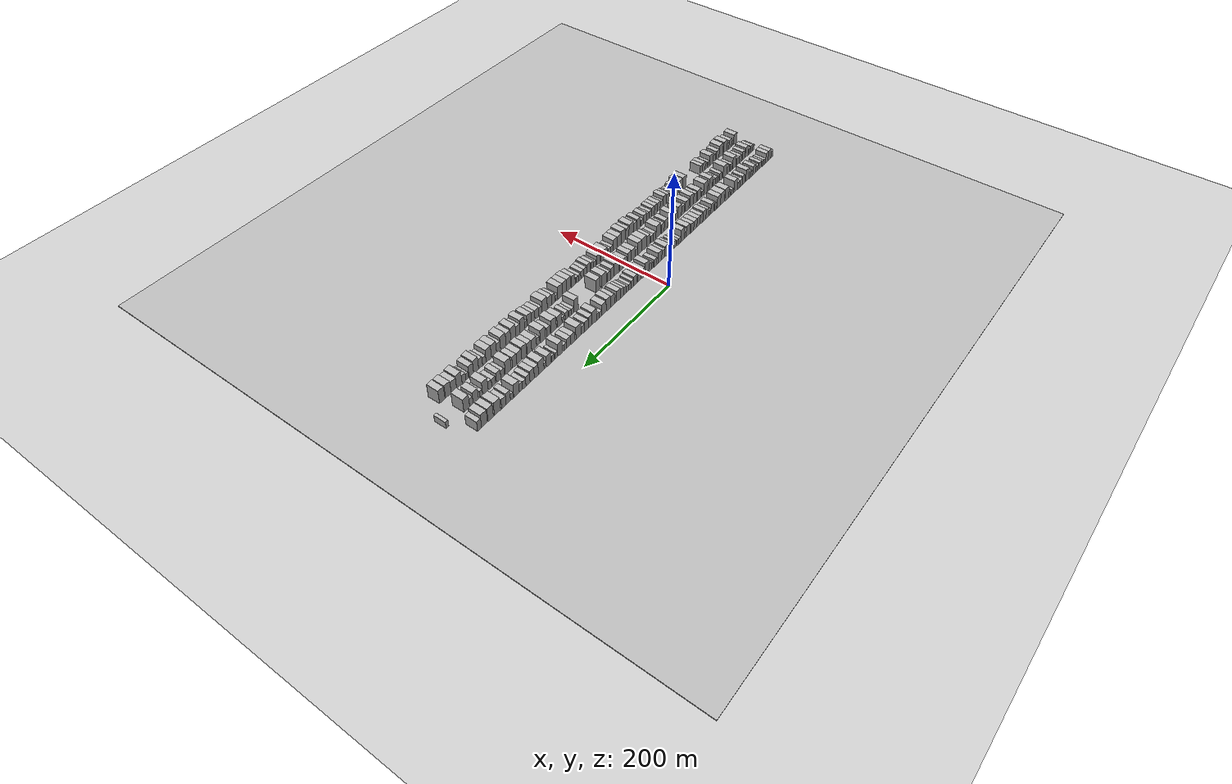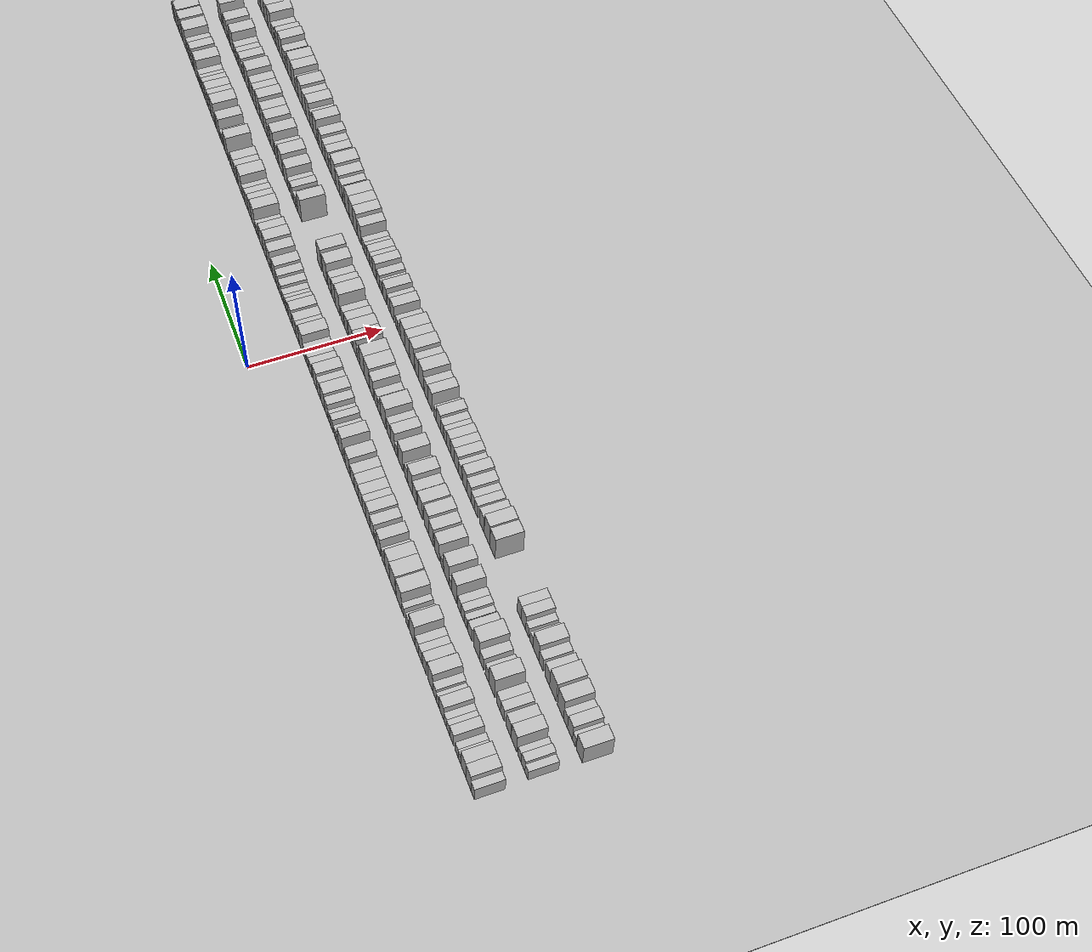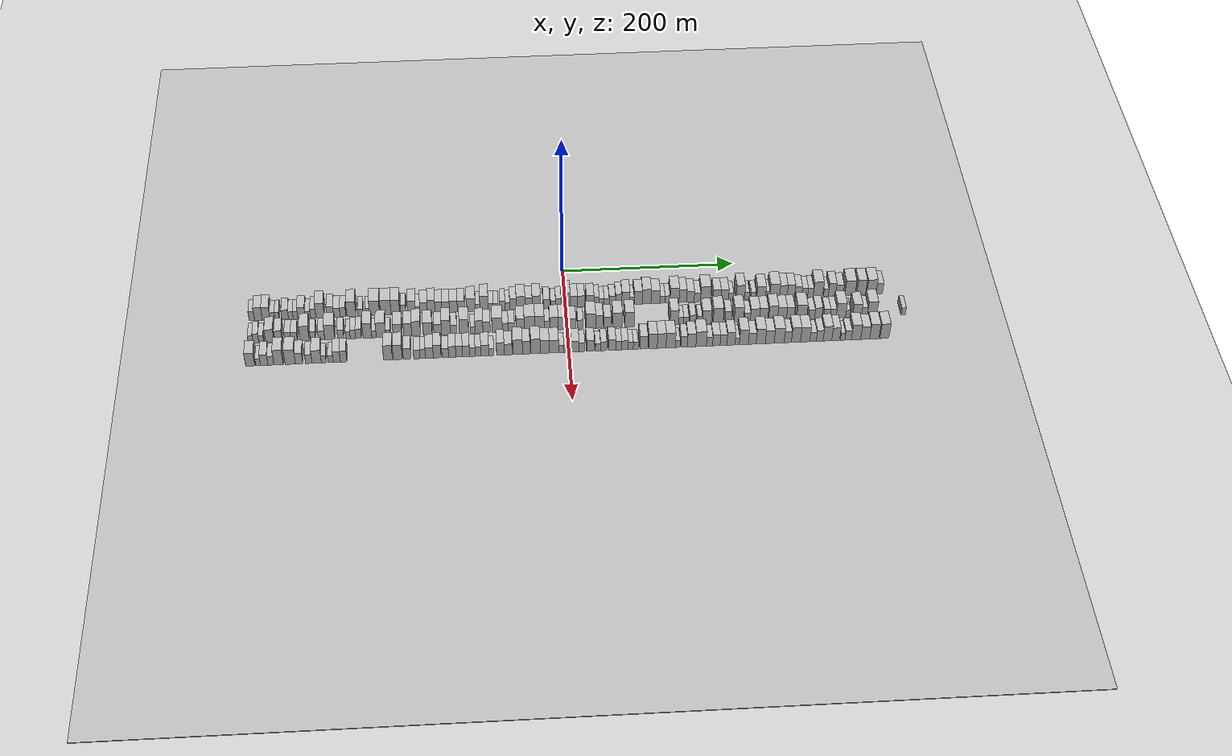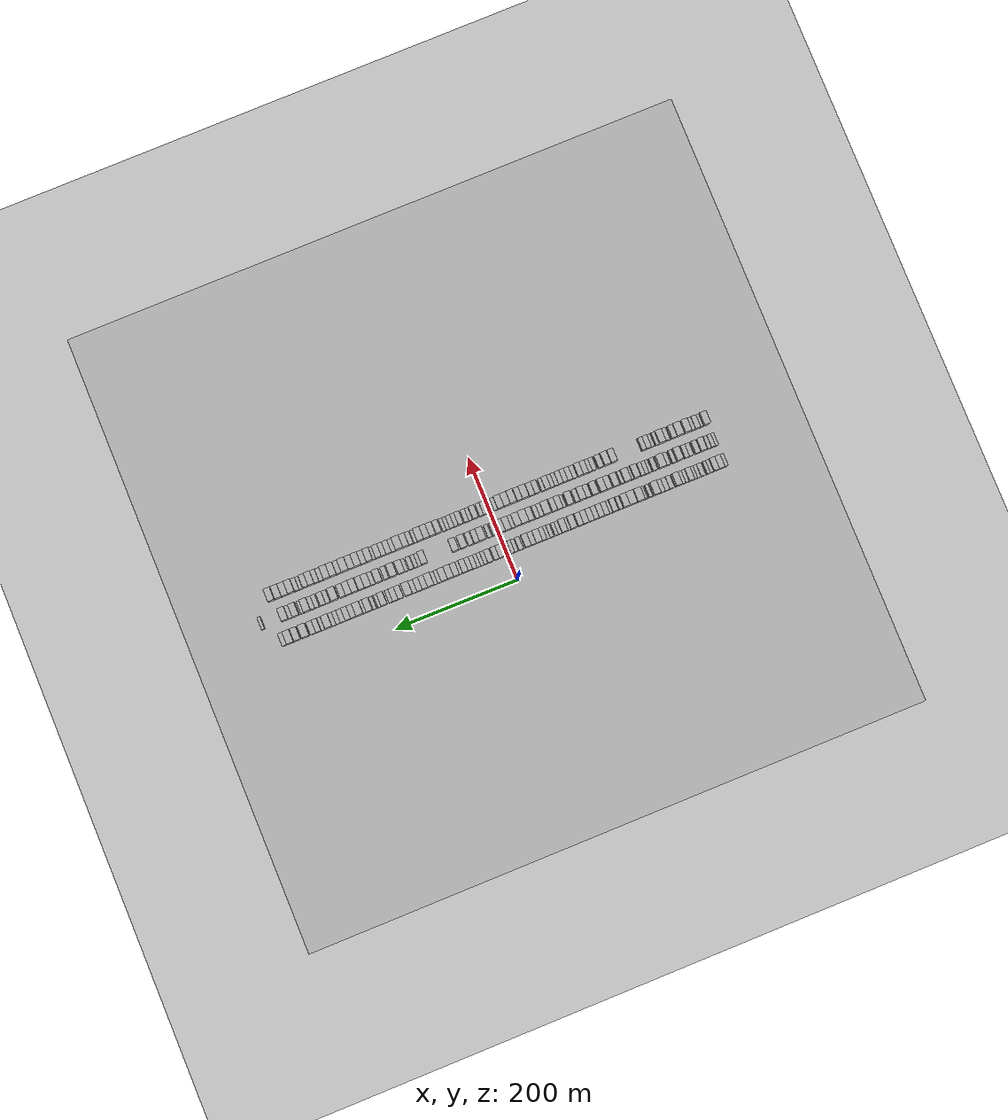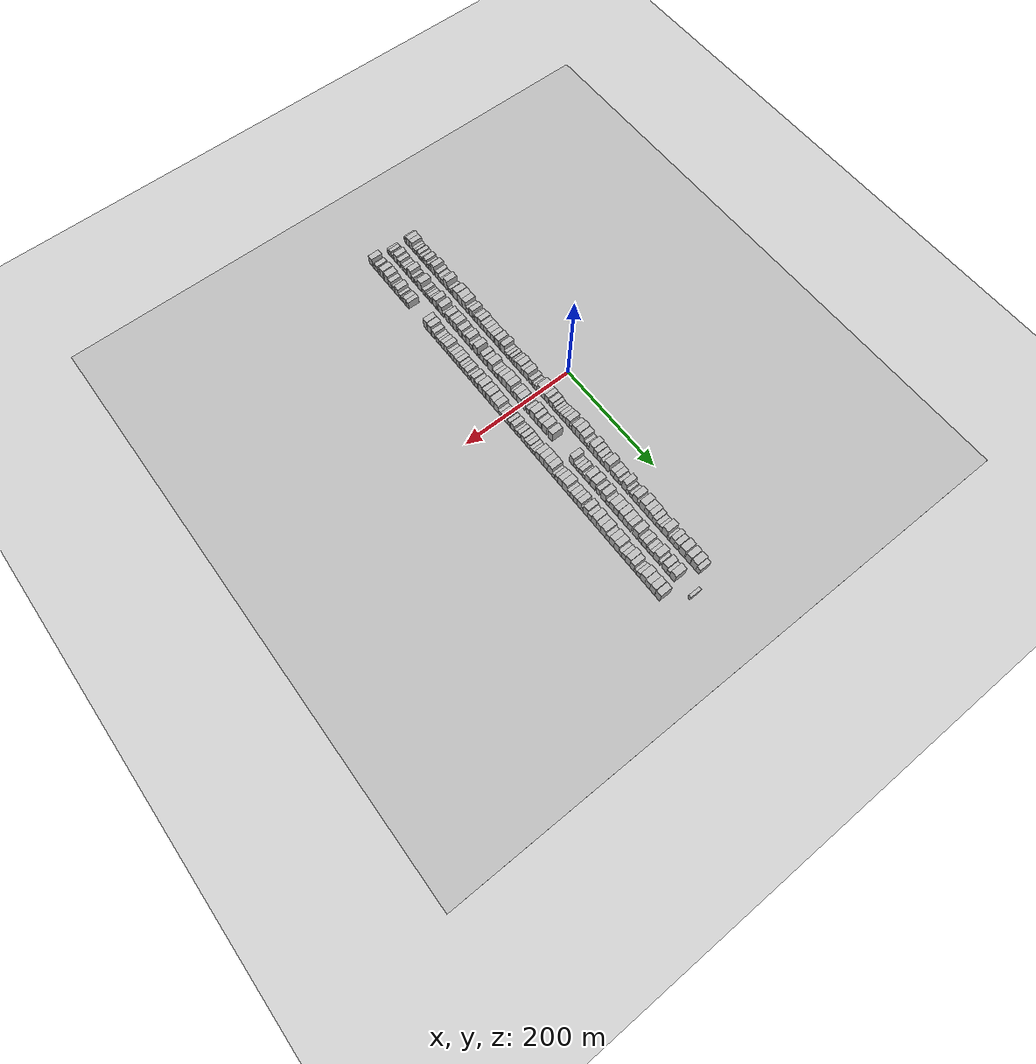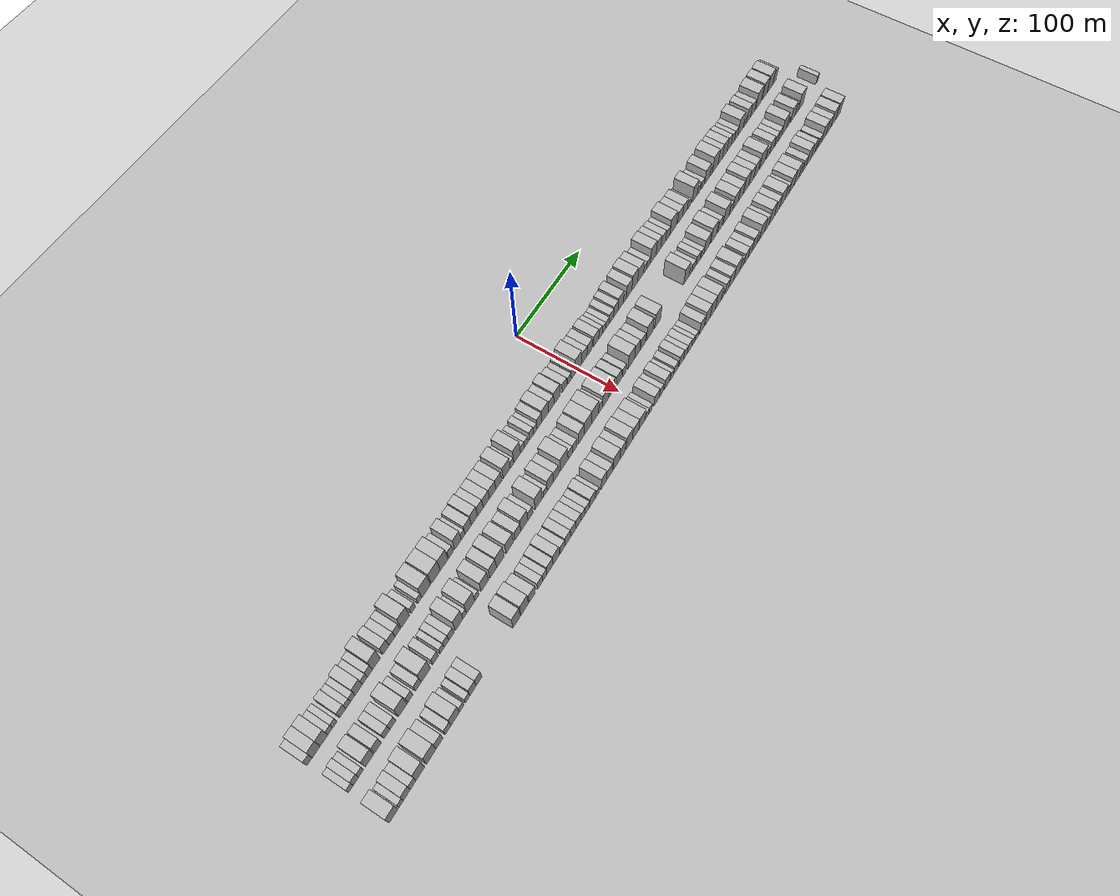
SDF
<?xml version="1.0" encoding="utf-8"?>

<sdf version="1.6">

   <world name="default">

      <gui fullscreen="0">

         <camera name="user_camera">

            <pose>-15 0 4.57585 0 0 0</pose>

            <view_controller>orbit</view_controller>

         </camera>

      </gui>

      <scene>

         <sky>

           <clouds>

             <speed>12</speed>

           </clouds>

         </sky>

         <ambient>0.4 0.4 0.4 1</ambient>

         <background>0.7 0.7 0.7 1</background>

         <shadows>1</shadows>

      </scene>

      <gravity>0 0 -9.8066</gravity>

      <magnetic_field>6e-06 2.3e-05 -4.2e-05</magnetic_field>

      <physics default="0" name="default_physics" type="ode">

         <ode>

            <solver>

               <type>quick</type>

               <iters>10</iters>

               <sor>1.0</sor>

               <use_dynamic_moi_rescaling>0</use_dynamic_moi_rescaling>

            </solver>

            <constraints>

               <cfm>0</cfm>

               <erp>0.2</erp>

               <contact_max_correcting_vel>100</contact_max_correcting_vel>

               <contact_surface_layer>0.001</contact_surface_layer>

            </constraints>

         </ode>

         <max_step_size>0.004</max_step_size>

         <real_time_factor>1</real_time_factor>

         <real_time_update_rate>250</real_time_update_rate>

      </physics>

      <light name="sun" type="directional">

         <cast_shadows>1</cast_shadows>

         <pose>0 0 10 0 0 0</pose>

         <diffuse>0.8 0.8 0.8 1</diffuse>

         <specular>0.2 0.2 0.2 1</specular>

         <attenuation>

            <range>1000</range>

            <constant>0.9</constant>

            <linear>0.01</linear>

            <quadratic>0.001</quadratic>

         </attenuation>

         <direction>-0.5 0.1 -0.9</direction>

      </light>

      <include>

         <name>ground_plane_1</name>

         <uri>model://HANNAS_ground_plane</uri>

         <pose>0 0 0  0 0 0</pose>

      </include>

      <include>

         <name>ground_plane_2</name>

         <uri>model://HANNAS_ground_plane</uri>

         <pose>100 0 0  0 0 0</pose>

      </include>

      <model name="building_1">

         <static>1</static>

         <pose frame="">50.0000 -356.9835 0 0.000000 0.000000 0.000000</pose>

         <link name="link">

            <pose frame="">0 0 7.50 0 0 0</pose>

            <collision name="collision">

               <geometry>

                  <box>

                     <size>20.0000 6.0329 15.0000</size>

                  </box>

               </geometry>

               <max_contacts>10</max_contacts>

               <surface>

                  <contact>

                     <ode/>

                  </contact>

                  <bounce/>

                  <friction>

                     <torsional>

                        <ode/>

                     </torsional>

                     <ode/>

                  </friction>

               </surface>

            </collision>

            <visual name="visual">

               <cast_shadows>0</cast_shadows>

               <geometry>

                  <box>

                     <size>20.0000 6.0329 15.0000</size>

                  </box>

               </geometry>

               <material>

                  <script>

                     <uri>model://HANNAS_wall/materials/scripts</uri>

                     <uri>model://HANNAS_wall/materials/textures</uri>

                     <name>vrc/HANNAS_wall</name>

                  </script>

               </material>

            </visual>

            <self_collide>0</self_collide>

            <enable_wind>0</enable_wind>

            <kinematic>0</kinematic>

         </link>

      </model>

      <model name="building_2">

         <static>1</static>

         <pose frame="">50.0000 -349.4914 0 0.000000 0.000000 0.000000</pose>

         <link name="link">

            <pose frame="">0 0 10.50 0 0 0</pose>

            <collision name="collision">

               <geometry>

                  <box>

                     <size>20.0000 8.9514 21.0000</size>

                  </box>

               </geometry>

               <max_contacts>10</max_contacts>

               <surface>

                  <contact>

                     <ode/>

                  </contact>

                  <bounce/>

                  <friction>

                     <torsional>

                        <ode/>

                     </torsional>

                     <ode/>

                  </friction>

               </surface>

            </collision>

            <visual name="visual">

               <cast_shadows>0</cast_shadows>

               <geometry>

                  <box>

                     <size>20.0000 8.9514 21.0000</size>

                  </box>

               </geometry>

               <material>

                  <script>

                     <uri>model://HANNAS_wall/materials/scripts</uri>

                     <uri>model://HANNAS_wall/materials/textures</uri>

                     <name>vrc/HANNAS_wall</name>

                  </script>

               </material>

            </visual>

            <self_collide>0</self_collide>

            <enable_wind>0</enable_wind>

            <kinematic>0</kinematic>

         </link>

      </model>

      <model name="building_3">

         <static>1</static>

         <pose frame="">50.0000 -340.6945 0 0.000000 0.000000 0.000000</pose>

         <link name="link">

            <pose frame="">0 0 10.50 0 0 0</pose>

            <collision name="collision">

               <geometry>

                  <box>

                     <size>20.0000 8.6423 21.0000</size>

                  </box>

               </geometry>

               <max_contacts>10</max_contacts>

               <surface>

                  <contact>

                     <ode/>

                  </contact>

                  <bounce/>

                  <friction>

                     <torsional>

                        <ode/>

                     </torsional>

                     <ode/>

                  </friction>

               </surface>

            </collision>

            <visual name="visual">

               <cast_shadows>0</cast_shadows>

               <geometry>

                  <box>

                     <size>20.0000 8.6423 21.0000</size>

                  </box>

               </geometry>

               <material>

                  <script>

                     <uri>model://HANNAS_wall/materials/scripts</uri>

                     <uri>model://HANNAS_wall/materials/textures</uri>

                     <name>vrc/HANNAS_wall</name>

                  </script>

               </material>

            </visual>

            <self_collide>0</self_collide>

            <enable_wind>0</enable_wind>

            <kinematic>0</kinematic>

         </link>

      </model>

      <model name="building_4">

         <static>1</static>

         <pose frame="">50.0000 -333.6761 0 0.000000 0.000000 0.000000</pose>

         <link name="link">

            <pose frame="">0 0 6.00 0 0 0</pose>

            <collision name="collision">

               <geometry>

                  <box>

                     <size>20.0000 5.3945 12.0000</size>

                  </box>

               </geometry>

               <max_contacts>10</max_contacts>

               <surface>

                  <contact>

                     <ode/>

                  </contact>

                  <bounce/>

                  <friction>

                     <torsional>

                        <ode/>

                     </torsional>

                     <ode/>

                  </friction>

               </surface>

            </collision>

            <visual name="visual">

               <cast_shadows>0</cast_shadows>

               <geometry>

                  <box>

                     <size>20.0000 5.3945 12.0000</size>

                  </box>

               </geometry>

               <material>

                  <script>

                     <uri>model://HANNAS_wall/materials/scripts</uri>

                     <uri>model://HANNAS_wall/materials/textures</uri>

                     <name>vrc/HANNAS_wall</name>

                  </script>

               </material>

            </visual>

            <self_collide>0</self_collide>

            <enable_wind>0</enable_wind>

            <kinematic>0</kinematic>

         </link>

      </model>

      <model name="building_5">

         <static>1</static>

         <pose frame="">50.0000 -328.4393 0 0.000000 0.000000 0.000000</pose>

         <link name="link">

            <pose frame="">0 0 6.00 0 0 0</pose>

            <collision name="collision">

               <geometry>

                  <box>

                     <size>20.0000 5.0790 12.0000</size>

                  </box>

               </geometry>

               <max_contacts>10</max_contacts>

               <surface>

                  <contact>

                     <ode/>

                  </contact>

                  <bounce/>

                  <friction>

                     <torsional>

                        <ode/>

                     </torsional>

                     <ode/>

                  </friction>

               </surface>

            </collision>

            <visual name="visual">

               <cast_shadows>0</cast_shadows>

               <geometry>

                  <box>

                     <size>20.0000 5.0790 12.0000</size>

                  </box>

               </geometry>

               <material>

                  <script>

                     <uri>model://HANNAS_wall/materials/scripts</uri>

                     <uri>model://HANNAS_wall/materials/textures</uri>

                     <name>vrc/HANNAS_wall</name>

                  </script>

               </material>

            </visual>

            <self_collide>0</self_collide>

            <enable_wind>0</enable_wind>

            <kinematic>0</kinematic>

         </link>

      </model>

      <model name="building_6">

         <static>1</static>

         <pose frame="">50.0000 -319.2377 0 0.000000 0.000000 0.000000</pose>

         <link name="link">

            <pose frame="">0 0 7.50 0 0 0</pose>

            <collision name="collision">

               <geometry>

                  <box>

                     <size>20.0000 7.3243 15.0000</size>

                  </box>

               </geometry>

               <max_contacts>10</max_contacts>

               <surface>

                  <contact>

                     <ode/>

                  </contact>

                  <bounce/>

                  <friction>

                     <torsional>

                        <ode/>

                     </torsional>

                     <ode/>

                  </friction>

               </surface>

            </collision>

            <visual name="visual">

               <cast_shadows>0</cast_shadows>

               <geometry>

                  <box>

                     <size>20.0000 7.3243 15.0000</size>

                  </box>

               </geometry>

               <material>

                  <script>

                     <uri>model://HANNAS_wall/materials/scripts</uri>

                     <uri>model://HANNAS_wall/materials/textures</uri>

                     <name>vrc/HANNAS_wall</name>

                  </script>

               </material>

            </visual>

            <self_collide>0</self_collide>

            <enable_wind>0</enable_wind>

            <kinematic>0</kinematic>

         </link>

      </model>

      <model name="building_7">

         <static>1</static>

         <pose frame="">50.0000 -312.8439 0 0.000000 0.000000 0.000000</pose>

         <link name="link">

            <pose frame="">0 0 6.00 0 0 0</pose>

            <collision name="collision">

               <geometry>

                  <box>

                     <size>20.0000 5.4632 12.0000</size>

                  </box>

               </geometry>

               <max_contacts>10</max_contacts>

               <surface>

                  <contact>

                     <ode/>

                  </contact>

                  <bounce/>

                  <friction>

                     <torsional>

                        <ode/>

                     </torsional>

                     <ode/>

                  </friction>

               </surface>

            </collision>

            <visual name="visual">

               <cast_shadows>0</cast_shadows>

               <geometry>

                  <box>

                     <size>20.0000 5.4632 12.0000</size>

                  </box>

               </geometry>

               <material>

                  <script>

                     <uri>model://HANNAS_wall/materials/scripts</uri>

                     <uri>model://HANNAS_wall/materials/textures</uri>

                     <name>vrc/HANNAS_wall</name>

                  </script>

               </material>

            </visual>

            <self_collide>0</self_collide>

            <enable_wind>0</enable_wind>

            <kinematic>0</kinematic>

         </link>

      </model>

      <model name="building_8">

         <static>1</static>

         <pose frame="">50.0000 -307.4999 0 0.000000 0.000000 0.000000</pose>

         <link name="link">

            <pose frame="">0 0 6.00 0 0 0</pose>

            <collision name="collision">

               <geometry>

                  <box>

                     <size>20.0000 5.2248 12.0000</size>

                  </box>

               </geometry>

               <max_contacts>10</max_contacts>

               <surface>

                  <contact>

                     <ode/>

                  </contact>

                  <bounce/>

                  <friction>

                     <torsional>

                        <ode/>

                     </torsional>

                     <ode/>

                  </friction>

               </surface>

            </collision>

            <visual name="visual">

               <cast_shadows>0</cast_shadows>

               <geometry>

                  <box>

                     <size>20.0000 5.2248 12.0000</size>

                  </box>

               </geometry>

               <material>

                  <script>

                     <uri>model://HANNAS_wall/materials/scripts</uri>

                     <uri>model://HANNAS_wall/materials/textures</uri>

                     <name>vrc/HANNAS_wall</name>

                  </script>

               </material>

            </visual>

            <self_collide>0</self_collide>

            <enable_wind>0</enable_wind>

            <kinematic>0</kinematic>

         </link>

      </model>

      <model name="building_9">

         <static>1</static>

         <pose frame="">50.0000 -300.5906 0 0.000000 0.000000 0.000000</pose>

         <link name="link">

            <pose frame="">0 0 9.00 0 0 0</pose>

            <collision name="collision">

               <geometry>

                  <box>

                     <size>20.0000 8.5937 18.0000</size>

                  </box>

               </geometry>

               <max_contacts>10</max_contacts>

               <surface>

                  <contact>

                     <ode/>

                  </contact>

                  <bounce/>

                  <friction>

                     <torsional>

                        <ode/>

                     </torsional>

                     <ode/>

                  </friction>

               </surface>

            </collision>

            <visual name="visual">

               <cast_shadows>0</cast_shadows>

               <geometry>

                  <box>

                     <size>20.0000 8.5937 18.0000</size>

                  </box>

               </geometry>

               <material>

                  <script>

                     <uri>model://HANNAS_wall/materials/scripts</uri>

                     <uri>model://HANNAS_wall/materials/textures</uri>

                     <name>vrc/HANNAS_wall</name>

                  </script>

               </material>

            </visual>

            <self_collide>0</self_collide>

            <enable_wind>0</enable_wind>

            <kinematic>0</kinematic>

         </link>

      </model>

      <model name="building_10">

         <static>1</static>

         <pose frame="">50.0000 -293.3726 0 0.000000 0.000000 0.000000</pose>

         <link name="link">

            <pose frame="">0 0 6.00 0 0 0</pose>

            <collision name="collision">

               <geometry>

                  <box>

                     <size>20.0000 5.8423 12.0000</size>

                  </box>

               </geometry>

               <max_contacts>10</max_contacts>

               <surface>

                  <contact>

                     <ode/>

                  </contact>

                  <bounce/>

                  <friction>

                     <torsional>

                        <ode/>

                     </torsional>

                     <ode/>

                  </friction>

               </surface>

            </collision>

            <visual name="visual">

               <cast_shadows>0</cast_shadows>

               <geometry>

                  <box>

                     <size>20.0000 5.8423 12.0000</size>

                  </box>

               </geometry>

               <material>

                  <script>

                     <uri>model://HANNAS_wall/materials/scripts</uri>

                     <uri>model://HANNAS_wall/materials/textures</uri>

                     <name>vrc/HANNAS_wall</name>

                  </script>

               </material>

            </visual>

            <self_collide>0</self_collide>

            <enable_wind>0</enable_wind>

            <kinematic>0</kinematic>

         </link>

      </model>

      <model name="building_11">

         <static>1</static>

         <pose frame="">50.0000 -287.3833 0 0.000000 0.000000 0.000000</pose>

         <link name="link">

            <pose frame="">0 0 7.50 0 0 0</pose>

            <collision name="collision">

               <geometry>

                  <box>

                     <size>20.0000 6.1364 15.0000</size>

                  </box>

               </geometry>

               <max_contacts>10</max_contacts>

               <surface>

                  <contact>

                     <ode/>

                  </contact>

                  <bounce/>

                  <friction>

                     <torsional>

                        <ode/>

                     </torsional>

                     <ode/>

                  </friction>

               </surface>

            </collision>

            <visual name="visual">

               <cast_shadows>0</cast_shadows>

               <geometry>

                  <box>

                     <size>20.0000 6.1364 15.0000</size>

                  </box>

               </geometry>

               <material>

                  <script>

                     <uri>model://HANNAS_wall/materials/scripts</uri>

                     <uri>model://HANNAS_wall/materials/textures</uri>

                     <name>vrc/HANNAS_wall</name>

                  </script>

               </material>

            </visual>

            <self_collide>0</self_collide>

            <enable_wind>0</enable_wind>

            <kinematic>0</kinematic>

         </link>

      </model>

      <model name="building_12">

         <static>1</static>

         <pose frame="">50.0000 -279.4902 0 0.000000 0.000000 0.000000</pose>

         <link name="link">

            <pose frame="">0 0 12.00 0 0 0</pose>

            <collision name="collision">

               <geometry>

                  <box>

                     <size>20.0000 9.6498 24.0000</size>

                  </box>

               </geometry>

               <max_contacts>10</max_contacts>

               <surface>

                  <contact>

                     <ode/>

                  </contact>

                  <bounce/>

                  <friction>

                     <torsional>

                        <ode/>

                     </torsional>

                     <ode/>

                  </friction>

               </surface>

            </collision>

            <visual name="visual">

               <cast_shadows>0</cast_shadows>

               <geometry>

                  <box>

                     <size>20.0000 9.6498 24.0000</size>

                  </box>

               </geometry>

               <material>

                  <script>

                     <uri>model://HANNAS_wall/materials/scripts</uri>

                     <uri>model://HANNAS_wall/materials/textures</uri>

                     <name>vrc/HANNAS_wall</name>

                  </script>

               </material>

            </visual>

            <self_collide>0</self_collide>

            <enable_wind>0</enable_wind>

            <kinematic>0</kinematic>

         </link>

      </model>

      <model name="building_13">

         <static>1</static>

         <pose frame="">50.0000 -267.8893 0 0.000000 0.000000 0.000000</pose>

         <link name="link">

            <pose frame="">0 0 9.00 0 0 0</pose>

            <collision name="collision">

               <geometry>

                  <box>

                     <size>20.0000 7.5519 18.0000</size>

                  </box>

               </geometry>

               <max_contacts>10</max_contacts>

               <surface>

                  <contact>

                     <ode/>

                  </contact>

                  <bounce/>

                  <friction>

                     <torsional>

                        <ode/>

                     </torsional>

                     <ode/>

                  </friction>

               </surface>

            </collision>

            <visual name="visual">

               <cast_shadows>0</cast_shadows>

               <geometry>

                  <box>

                     <size>20.0000 7.5519 18.0000</size>

                  </box>

               </geometry>

               <material>

                  <script>

                     <uri>model://HANNAS_wall/materials/scripts</uri>

                     <uri>model://HANNAS_wall/materials/textures</uri>

                     <name>vrc/HANNAS_wall</name>

                  </script>

               </material>

            </visual>

            <self_collide>0</self_collide>

            <enable_wind>0</enable_wind>

            <kinematic>0</kinematic>

         </link>

      </model>

      <model name="building_14">

         <static>1</static>

         <pose frame="">50.0000 -260.4204 0 0.000000 0.000000 0.000000</pose>

         <link name="link">

            <pose frame="">0 0 7.50 0 0 0</pose>

            <collision name="collision">

               <geometry>

                  <box>

                     <size>20.0000 7.3857 15.0000</size>

                  </box>

               </geometry>

               <max_contacts>10</max_contacts>

               <surface>

                  <contact>

                     <ode/>

                  </contact>

                  <bounce/>

                  <friction>

                     <torsional>

                        <ode/>

                     </torsional>

                     <ode/>

                  </friction>

               </surface>

            </collision>

            <visual name="visual">

               <cast_shadows>0</cast_shadows>

               <geometry>

                  <box>

                     <size>20.0000 7.3857 15.0000</size>

                  </box>

               </geometry>

               <material>

                  <script>

                     <uri>model://HANNAS_wall/materials/scripts</uri>

                     <uri>model://HANNAS_wall/materials/textures</uri>

                     <name>vrc/HANNAS_wall</name>

                  </script>

               </material>

            </visual>

            <self_collide>0</self_collide>

            <enable_wind>0</enable_wind>

            <kinematic>0</kinematic>

         </link>

      </model>

      <model name="building_15">

         <static>1</static>

         <pose frame="">50.0000 -253.4633 0 0.000000 0.000000 0.000000</pose>

         <link name="link">

            <pose frame="">0 0 7.50 0 0 0</pose>

            <collision name="collision">

               <geometry>

                  <box>

                     <size>20.0000 6.5285 15.0000</size>

                  </box>

               </geometry>

               <max_contacts>10</max_contacts>

               <surface>

                  <contact>

                     <ode/>

                  </contact>

                  <bounce/>

                  <friction>

                     <torsional>

                        <ode/>

                     </torsional>

                     <ode/>

                  </friction>

               </surface>

            </collision>

            <visual name="visual">

               <cast_shadows>0</cast_shadows>

               <geometry>

                  <box>

                     <size>20.0000 6.5285 15.0000</size>

                  </box>

               </geometry>

               <material>

                  <script>

                     <uri>model://HANNAS_wall/materials/scripts</uri>

                     <uri>model://HANNAS_wall/materials/textures</uri>

                     <name>vrc/HANNAS_wall</name>

                  </script>

               </material>

            </visual>

            <self_collide>0</self_collide>

            <enable_wind>0</enable_wind>

            <kinematic>0</kinematic>

         </link>

      </model>

      <model name="building_16">

         <static>1</static>

         <pose frame="">50.0000 -243.9279 0 0.000000 0.000000 0.000000</pose>

         <link name="link">

            <pose frame="">0 0 12.00 0 0 0</pose>

            <collision name="collision">

               <geometry>

                  <box>

                     <size>20.0000 10.5424 24.0000</size>

                  </box>

               </geometry>

               <max_contacts>10</max_contacts>

               <surface>

                  <contact>

                     <ode/>

                  </contact>

                  <bounce/>

                  <friction>

                     <torsional>

                        <ode/>

                     </torsional>

                     <ode/>

                  </friction>

               </surface>

            </collision>

            <visual name="visual">

               <cast_shadows>0</cast_shadows>

               <geometry>

                  <box>

                     <size>20.0000 10.5424 24.0000</size>

                  </box>

               </geometry>

               <material>

                  <script>

                     <uri>model://HANNAS_wall/materials/scripts</uri>

                     <uri>model://HANNAS_wall/materials/textures</uri>

                     <name>vrc/HANNAS_wall</name>

                  </script>

               </material>

            </visual>

            <self_collide>0</self_collide>

            <enable_wind>0</enable_wind>

            <kinematic>0</kinematic>

         </link>

      </model>

      <model name="building_17">

         <static>1</static>

         <pose frame="">50.0000 -233.8739 0 0.000000 0.000000 0.000000</pose>

         <link name="link">

            <pose frame="">0 0 6.00 0 0 0</pose>

            <collision name="collision">

               <geometry>

                  <box>

                     <size>20.0000 5.5656 12.0000</size>

                  </box>

               </geometry>

               <max_contacts>10</max_contacts>

               <surface>

                  <contact>

                     <ode/>

                  </contact>

                  <bounce/>

                  <friction>

                     <torsional>

                        <ode/>

                     </torsional>

                     <ode/>

                  </friction>

               </surface>

            </collision>

            <visual name="visual">

               <cast_shadows>0</cast_shadows>

               <geometry>

                  <box>

                     <size>20.0000 5.5656 12.0000</size>

                  </box>

               </geometry>

               <material>

                  <script>

                     <uri>model://HANNAS_wall/materials/scripts</uri>

                     <uri>model://HANNAS_wall/materials/textures</uri>

                     <name>vrc/HANNAS_wall</name>

                  </script>

               </material>

            </visual>

            <self_collide>0</self_collide>

            <enable_wind>0</enable_wind>

            <kinematic>0</kinematic>

         </link>

      </model>

      <model name="building_18">

         <static>1</static>

         <pose frame="">50.0000 -225.6553 0 0.000000 0.000000 0.000000</pose>

         <link name="link">

            <pose frame="">0 0 6.00 0 0 0</pose>

            <collision name="collision">

               <geometry>

                  <box>

                     <size>20.0000 4.8715 12.0000</size>

                  </box>

               </geometry>

               <max_contacts>10</max_contacts>

               <surface>

                  <contact>

                     <ode/>

                  </contact>

                  <bounce/>

                  <friction>

                     <torsional>

                        <ode/>

                     </torsional>

                     <ode/>

                  </friction>

               </surface>

            </collision>

            <visual name="visual">

               <cast_shadows>0</cast_shadows>

               <geometry>

                  <box>

                     <size>20.0000 4.8715 12.0000</size>

                  </box>

               </geometry>

               <material>

                  <script>

                     <uri>model://HANNAS_wall/materials/scripts</uri>

                     <uri>model://HANNAS_wall/materials/textures</uri>

                     <name>vrc/HANNAS_wall</name>

                  </script>

               </material>

            </visual>

            <self_collide>0</self_collide>

            <enable_wind>0</enable_wind>

            <kinematic>0</kinematic>

         </link>

      </model>

      <model name="building_19">

         <static>1</static>

         <pose frame="">50.0000 -217.5249 0 0.000000 0.000000 0.000000</pose>

         <link name="link">

            <pose frame="">0 0 12.00 0 0 0</pose>

            <collision name="collision">

               <geometry>

                  <box>

                     <size>20.0000 11.3892 24.0000</size>

                  </box>

               </geometry>

               <max_contacts>10</max_contacts>

               <surface>

                  <contact>

                     <ode/>

                  </contact>

                  <bounce/>

                  <friction>

                     <torsional>

                        <ode/>

                     </torsional>

                     <ode/>

                  </friction>

               </surface>

            </collision>

            <visual name="visual">

               <cast_shadows>0</cast_shadows>

               <geometry>

                  <box>

                     <size>20.0000 11.3892 24.0000</size>

                  </box>

               </geometry>

               <material>

                  <script>

                     <uri>model://HANNAS_wall/materials/scripts</uri>

                     <uri>model://HANNAS_wall/materials/textures</uri>

                     <name>vrc/HANNAS_wall</name>

                  </script>

               </material>

            </visual>

            <self_collide>0</self_collide>

            <enable_wind>0</enable_wind>

            <kinematic>0</kinematic>

         </link>

      </model>

      <model name="building_20">

         <static>1</static>

         <pose frame="">50.0000 -204.8375 0 0.000000 0.000000 0.000000</pose>

         <link name="link">

            <pose frame="">0 0 12.00 0 0 0</pose>

            <collision name="collision">

               <geometry>

                  <box>

                     <size>20.0000 11.9856 24.0000</size>

                  </box>

               </geometry>

               <max_contacts>10</max_contacts>

               <surface>

                  <contact>

                     <ode/>

                  </contact>

                  <bounce/>

                  <friction>

                     <torsional>

                        <ode/>

                     </torsional>

                     <ode/>

                  </friction>

               </surface>

            </collision>

            <visual name="visual">

               <cast_shadows>0</cast_shadows>

               <geometry>

                  <box>

                     <size>20.0000 11.9856 24.0000</size>

                  </box>

               </geometry>

               <material>

                  <script>

                     <uri>model://HANNAS_wall/materials/scripts</uri>

                     <uri>model://HANNAS_wall/materials/textures</uri>

                     <name>vrc/HANNAS_wall</name>

                  </script>

               </material>

            </visual>

            <self_collide>0</self_collide>

            <enable_wind>0</enable_wind>

            <kinematic>0</kinematic>

         </link>

      </model>

      <model name="building_21">

         <static>1</static>

         <pose frame="">50.0000 -193.8713 0 0.000000 0.000000 0.000000</pose>

         <link name="link">

            <pose frame="">0 0 12.00 0 0 0</pose>

            <collision name="collision">

               <geometry>

                  <box>

                     <size>20.0000 9.9468 24.0000</size>

                  </box>

               </geometry>

               <max_contacts>10</max_contacts>

               <surface>

                  <contact>

                     <ode/>

                  </contact>

                  <bounce/>

                  <friction>

                     <torsional>

                        <ode/>

                     </torsional>

                     <ode/>

                  </friction>

               </surface>

            </collision>

            <visual name="visual">

               <cast_shadows>0</cast_shadows>

               <geometry>

                  <box>

                     <size>20.0000 9.9468 24.0000</size>

                  </box>

               </geometry>

               <material>

                  <script>

                     <uri>model://HANNAS_wall/materials/scripts</uri>

                     <uri>model://HANNAS_wall/materials/textures</uri>

                     <name>vrc/HANNAS_wall</name>

                  </script>

               </material>

            </visual>

            <self_collide>0</self_collide>

            <enable_wind>0</enable_wind>

            <kinematic>0</kinematic>

         </link>

      </model>

      <model name="building_22">

         <static>1</static>

         <pose frame="">50.0000 -184.8738 0 0.000000 0.000000 0.000000</pose>

         <link name="link">

            <pose frame="">0 0 7.50 0 0 0</pose>

            <collision name="collision">

               <geometry>

                  <box>

                     <size>20.0000 6.0483 15.0000</size>

                  </box>

               </geometry>

               <max_contacts>10</max_contacts>

               <surface>

                  <contact>

                     <ode/>

                  </contact>

                  <bounce/>

                  <friction>

                     <torsional>

                        <ode/>

                     </torsional>

                     <ode/>

                  </friction>

               </surface>

            </collision>

            <visual name="visual">

               <cast_shadows>0</cast_shadows>

               <geometry>

                  <box>

                     <size>20.0000 6.0483 15.0000</size>

                  </box>

               </geometry>

               <material>

                  <script>

                     <uri>model://HANNAS_wall/materials/scripts</uri>

                     <uri>model://HANNAS_wall/materials/textures</uri>

                     <name>vrc/HANNAS_wall</name>

                  </script>

               </material>

            </visual>

            <self_collide>0</self_collide>

            <enable_wind>0</enable_wind>

            <kinematic>0</kinematic>

         </link>

      </model>

      <model name="building_23">

         <static>1</static>

         <pose frame="">50.0000 -175.4392 0 0.000000 0.000000 0.000000</pose>

         <link name="link">

            <pose frame="">0 0 10.50 0 0 0</pose>

            <collision name="collision">

               <geometry>

                  <box>

                     <size>20.0000 8.8211 21.0000</size>

                  </box>

               </geometry>

               <max_contacts>10</max_contacts>

               <surface>

                  <contact>

                     <ode/>

                  </contact>

                  <bounce/>

                  <friction>

                     <torsional>

                        <ode/>

                     </torsional>

                     <ode/>

                  </friction>

               </surface>

            </collision>

            <visual name="visual">

               <cast_shadows>0</cast_shadows>

               <geometry>

                  <box>

                     <size>20.0000 8.8211 21.0000</size>

                  </box>

               </geometry>

               <material>

                  <script>

                     <uri>model://HANNAS_wall/materials/scripts</uri>

                     <uri>model://HANNAS_wall/materials/textures</uri>

                     <name>vrc/HANNAS_wall</name>

                  </script>

               </material>

            </visual>

            <self_collide>0</self_collide>

            <enable_wind>0</enable_wind>

            <kinematic>0</kinematic>

         </link>

      </model>

      <model name="building_24">

         <static>1</static>

         <pose frame="">50.0000 -168.4670 0 0.000000 0.000000 0.000000</pose>

         <link name="link">

            <pose frame="">0 0 6.00 0 0 0</pose>

            <collision name="collision">

               <geometry>

                  <box>

                     <size>20.0000 5.1233 12.0000</size>

                  </box>

               </geometry>

               <max_contacts>10</max_contacts>

               <surface>

                  <contact>

                     <ode/>

                  </contact>

                  <bounce/>

                  <friction>

                     <torsional>

                        <ode/>

                     </torsional>

                     <ode/>

                  </friction>

               </surface>

            </collision>

            <visual name="visual">

               <cast_shadows>0</cast_shadows>

               <geometry>

                  <box>

                     <size>20.0000 5.1233 12.0000</size>

                  </box>

               </geometry>

               <material>

                  <script>

                     <uri>model://HANNAS_wall/materials/scripts</uri>

                     <uri>model://HANNAS_wall/materials/textures</uri>

                     <name>vrc/HANNAS_wall</name>

                  </script>

               </material>

            </visual>

            <self_collide>0</self_collide>

            <enable_wind>0</enable_wind>

            <kinematic>0</kinematic>

         </link>

      </model>

      <model name="building_25">

         <static>1</static>

         <pose frame="">50.0000 -161.6642 0 0.000000 0.000000 0.000000</pose>

         <link name="link">

            <pose frame="">0 0 9.00 0 0 0</pose>

            <collision name="collision">

               <geometry>

                  <box>

                     <size>20.0000 8.4823 18.0000</size>

                  </box>

               </geometry>

               <max_contacts>10</max_contacts>

               <surface>

                  <contact>

                     <ode/>

                  </contact>

                  <bounce/>

                  <friction>

                     <torsional>

                        <ode/>

                     </torsional>

                     <ode/>

                  </friction>

               </surface>

            </collision>

            <visual name="visual">

               <cast_shadows>0</cast_shadows>

               <geometry>

                  <box>

                     <size>20.0000 8.4823 18.0000</size>

                  </box>

               </geometry>

               <material>

                  <script>

                     <uri>model://HANNAS_wall/materials/scripts</uri>

                     <uri>model://HANNAS_wall/materials/textures</uri>

                     <name>vrc/HANNAS_wall</name>

                  </script>

               </material>

            </visual>

            <self_collide>0</self_collide>

            <enable_wind>0</enable_wind>

            <kinematic>0</kinematic>

         </link>

      </model>

      <model name="building_26">

         <static>1</static>

         <pose frame="">50.0000 -153.0441 0 0.000000 0.000000 0.000000</pose>

         <link name="link">

            <pose frame="">0 0 10.50 0 0 0</pose>

            <collision name="collision">

               <geometry>

                  <box>

                     <size>20.0000 8.7578 21.0000</size>

                  </box>

               </geometry>

               <max_contacts>10</max_contacts>

               <surface>

                  <contact>

                     <ode/>

                  </contact>

                  <bounce/>

                  <friction>

                     <torsional>

                        <ode/>

                     </torsional>

                     <ode/>

                  </friction>

               </surface>

            </collision>

            <visual name="visual">

               <cast_shadows>0</cast_shadows>

               <geometry>

                  <box>

                     <size>20.0000 8.7578 21.0000</size>

                  </box>

               </geometry>

               <material>

                  <script>

                     <uri>model://HANNAS_wall/materials/scripts</uri>

                     <uri>model://HANNAS_wall/materials/textures</uri>

                     <name>vrc/HANNAS_wall</name>

                  </script>

               </material>

            </visual>

            <self_collide>0</self_collide>

            <enable_wind>0</enable_wind>

            <kinematic>0</kinematic>

         </link>

      </model>

      <model name="building_27">

         <static>1</static>

         <pose frame="">50.0000 -144.7864 0 0.000000 0.000000 0.000000</pose>

         <link name="link">

            <pose frame="">0 0 9.00 0 0 0</pose>

            <collision name="collision">

               <geometry>

                  <box>

                     <size>20.0000 7.7576 18.0000</size>

                  </box>

               </geometry>

               <max_contacts>10</max_contacts>

               <surface>

                  <contact>

                     <ode/>

                  </contact>

                  <bounce/>

                  <friction>

                     <torsional>

                        <ode/>

                     </torsional>

                     <ode/>

                  </friction>

               </surface>

            </collision>

            <visual name="visual">

               <cast_shadows>0</cast_shadows>

               <geometry>

                  <box>

                     <size>20.0000 7.7576 18.0000</size>

                  </box>

               </geometry>

               <material>

                  <script>

                     <uri>model://HANNAS_wall/materials/scripts</uri>

                     <uri>model://HANNAS_wall/materials/textures</uri>

                     <name>vrc/HANNAS_wall</name>

                  </script>

               </material>

            </visual>

            <self_collide>0</self_collide>

            <enable_wind>0</enable_wind>

            <kinematic>0</kinematic>

         </link>

      </model>

      <model name="building_28">

         <static>1</static>

         <pose frame="">50.0000 -136.5744 0 0.000000 0.000000 0.000000</pose>

         <link name="link">

            <pose frame="">0 0 9.00 0 0 0</pose>

            <collision name="collision">

               <geometry>

                  <box>

                     <size>20.0000 8.6665 18.0000</size>

                  </box>

               </geometry>

               <max_contacts>10</max_contacts>

               <surface>

                  <contact>

                     <ode/>

                  </contact>

                  <bounce/>

                  <friction>

                     <torsional>

                        <ode/>

                     </torsional>

                     <ode/>

                  </friction>

               </surface>

            </collision>

            <visual name="visual">

               <cast_shadows>0</cast_shadows>

               <geometry>

                  <box>

                     <size>20.0000 8.6665 18.0000</size>

                  </box>

               </geometry>

               <material>

                  <script>

                     <uri>model://HANNAS_wall/materials/scripts</uri>

                     <uri>model://HANNAS_wall/materials/textures</uri>

                     <name>vrc/HANNAS_wall</name>

                  </script>

               </material>

            </visual>

            <self_collide>0</self_collide>

            <enable_wind>0</enable_wind>

            <kinematic>0</kinematic>

         </link>

      </model>

      <model name="building_29">

         <static>1</static>

         <pose frame="">50.0000 -127.7467 0 0.000000 0.000000 0.000000</pose>

         <link name="link">

            <pose frame="">0 0 9.00 0 0 0</pose>

            <collision name="collision">

               <geometry>

                  <box>

                     <size>20.0000 8.9890 18.0000</size>

                  </box>

               </geometry>

               <max_contacts>10</max_contacts>

               <surface>

                  <contact>

                     <ode/>

                  </contact>

                  <bounce/>

                  <friction>

                     <torsional>

                        <ode/>

                     </torsional>

                     <ode/>

                  </friction>

               </surface>

            </collision>

            <visual name="visual">

               <cast_shadows>0</cast_shadows>

               <geometry>

                  <box>

                     <size>20.0000 8.9890 18.0000</size>

                  </box>

               </geometry>

               <material>

                  <script>

                     <uri>model://HANNAS_wall/materials/scripts</uri>

                     <uri>model://HANNAS_wall/materials/textures</uri>

                     <name>vrc/HANNAS_wall</name>

                  </script>

               </material>

            </visual>

            <self_collide>0</self_collide>

            <enable_wind>0</enable_wind>

            <kinematic>0</kinematic>

         </link>

      </model>

      <model name="building_30">

         <static>1</static>

         <pose frame="">50.0000 -119.0309 0 0.000000 0.000000 0.000000</pose>

         <link name="link">

            <pose frame="">0 0 9.00 0 0 0</pose>

            <collision name="collision">

               <geometry>

                  <box>

                     <size>20.0000 8.4425 18.0000</size>

                  </box>

               </geometry>

               <max_contacts>10</max_contacts>

               <surface>

                  <contact>

                     <ode/>

                  </contact>

                  <bounce/>

                  <friction>

                     <torsional>

                        <ode/>

                     </torsional>

                     <ode/>

                  </friction>

               </surface>

            </collision>

            <visual name="visual">

               <cast_shadows>0</cast_shadows>

               <geometry>

                  <box>

                     <size>20.0000 8.4425 18.0000</size>

                  </box>

               </geometry>

               <material>

                  <script>

                     <uri>model://HANNAS_wall/materials/scripts</uri>

                     <uri>model://HANNAS_wall/materials/textures</uri>

                     <name>vrc/HANNAS_wall</name>

                  </script>

               </material>

            </visual>

            <self_collide>0</self_collide>

            <enable_wind>0</enable_wind>

            <kinematic>0</kinematic>

         </link>

      </model>

      <model name="building_31">

         <static>1</static>

         <pose frame="">50.0000 -107.7357 0 0.000000 0.000000 0.000000</pose>

         <link name="link">

            <pose frame="">0 0 10.50 0 0 0</pose>

            <collision name="collision">

               <geometry>

                  <box>

                     <size>20.0000 10.1479 21.0000</size>

                  </box>

               </geometry>

               <max_contacts>10</max_contacts>

               <surface>

                  <contact>

                     <ode/>

                  </contact>

                  <bounce/>

                  <friction>

                     <torsional>

                        <ode/>

                     </torsional>

                     <ode/>

                  </friction>

               </surface>

            </collision>

            <visual name="visual">

               <cast_shadows>0</cast_shadows>

               <geometry>

                  <box>

                     <size>20.0000 10.1479 21.0000</size>

                  </box>

               </geometry>

               <material>

                  <script>

                     <uri>model://HANNAS_wall/materials/scripts</uri>

                     <uri>model://HANNAS_wall/materials/textures</uri>

                     <name>vrc/HANNAS_wall</name>

                  </script>

               </material>

            </visual>

            <self_collide>0</self_collide>

            <enable_wind>0</enable_wind>

            <kinematic>0</kinematic>

         </link>

      </model>

      <model name="building_32">

         <static>1</static>

         <pose frame="">50.0000 -100.0869 0 0.000000 0.000000 0.000000</pose>

         <link name="link">

            <pose frame="">0 0 6.00 0 0 0</pose>

            <collision name="collision">

               <geometry>

                  <box>

                     <size>20.0000 5.1497 12.0000</size>

                  </box>

               </geometry>

               <max_contacts>10</max_contacts>

               <surface>

                  <contact>

                     <ode/>

                  </contact>

                  <bounce/>

                  <friction>

                     <torsional>

                        <ode/>

                     </torsional>

                     <ode/>

                  </friction>

               </surface>

            </collision>

            <visual name="visual">

               <cast_shadows>0</cast_shadows>

               <geometry>

                  <box>

                     <size>20.0000 5.1497 12.0000</size>

                  </box>

               </geometry>

               <material>

                  <script>

                     <uri>model://HANNAS_wall/materials/scripts</uri>

                     <uri>model://HANNAS_wall/materials/textures</uri>

                     <name>vrc/HANNAS_wall</name>

                  </script>

               </material>

            </visual>

            <self_collide>0</self_collide>

            <enable_wind>0</enable_wind>

            <kinematic>0</kinematic>

         </link>

      </model>

      <model name="building_33">

         <static>1</static>

         <pose frame="">50.0000 -92.7052 0 0.000000 0.000000 0.000000</pose>

         <link name="link">

            <pose frame="">0 0 12.00 0 0 0</pose>

            <collision name="collision">

               <geometry>

                  <box>

                     <size>20.0000 9.6137 24.0000</size>

                  </box>

               </geometry>

               <max_contacts>10</max_contacts>

               <surface>

                  <contact>

                     <ode/>

                  </contact>

                  <bounce/>

                  <friction>

                     <torsional>

                        <ode/>

                     </torsional>

                     <ode/>

                  </friction>

               </surface>

            </collision>

            <visual name="visual">

               <cast_shadows>0</cast_shadows>

               <geometry>

                  <box>

                     <size>20.0000 9.6137 24.0000</size>

                  </box>

               </geometry>

               <material>

                  <script>

                     <uri>model://HANNAS_wall/materials/scripts</uri>

                     <uri>model://HANNAS_wall/materials/textures</uri>

                     <name>vrc/HANNAS_wall</name>

                  </script>

               </material>

            </visual>

            <self_collide>0</self_collide>

            <enable_wind>0</enable_wind>

            <kinematic>0</kinematic>

         </link>

      </model>

      <model name="building_34">

         <static>1</static>

         <pose frame="">50.0000 -84.9929 0 0.000000 0.000000 0.000000</pose>

         <link name="link">

            <pose frame="">0 0 6.00 0 0 0</pose>

            <collision name="collision">

               <geometry>

                  <box>

                     <size>20.0000 5.8108 12.0000</size>

                  </box>

               </geometry>

               <max_contacts>10</max_contacts>

               <surface>

                  <contact>

                     <ode/>

                  </contact>

                  <bounce/>

                  <friction>

                     <torsional>

                        <ode/>

                     </torsional>

                     <ode/>

                  </friction>

               </surface>

            </collision>

            <visual name="visual">

               <cast_shadows>0</cast_shadows>

               <geometry>

                  <box>

                     <size>20.0000 5.8108 12.0000</size>

                  </box>

               </geometry>

               <material>

                  <script>

                     <uri>model://HANNAS_wall/materials/scripts</uri>

                     <uri>model://HANNAS_wall/materials/textures</uri>

                     <name>vrc/HANNAS_wall</name>

                  </script>

               </material>

            </visual>

            <self_collide>0</self_collide>

            <enable_wind>0</enable_wind>

            <kinematic>0</kinematic>

         </link>

      </model>

      <model name="building_35">

         <static>1</static>

         <pose frame="">50.0000 -79.4338 0 0.000000 0.000000 0.000000</pose>

         <link name="link">

            <pose frame="">0 0 6.00 0 0 0</pose>

            <collision name="collision">

               <geometry>

                  <box>

                     <size>20.0000 5.3074 12.0000</size>

                  </box>

               </geometry>

               <max_contacts>10</max_contacts>

               <surface>

                  <contact>

                     <ode/>

                  </contact>

                  <bounce/>

                  <friction>

                     <torsional>

                        <ode/>

                     </torsional>

                     <ode/>

                  </friction>

               </surface>

            </collision>

            <visual name="visual">

               <cast_shadows>0</cast_shadows>

               <geometry>

                  <box>

                     <size>20.0000 5.3074 12.0000</size>

                  </box>

               </geometry>

               <material>

                  <script>

                     <uri>model://HANNAS_wall/materials/scripts</uri>

                     <uri>model://HANNAS_wall/materials/textures</uri>

                     <name>vrc/HANNAS_wall</name>

                  </script>

               </material>

            </visual>

            <self_collide>0</self_collide>

            <enable_wind>0</enable_wind>

            <kinematic>0</kinematic>

         </link>

      </model>

      <model name="building_36">

         <static>1</static>

         <pose frame="">50.0000 -71.7630 0 0.000000 0.000000 0.000000</pose>

         <link name="link">

            <pose frame="">0 0 7.50 0 0 0</pose>

            <collision name="collision">

               <geometry>

                  <box>

                     <size>20.0000 6.0342 15.0000</size>

                  </box>

               </geometry>

               <max_contacts>10</max_contacts>

               <surface>

                  <contact>

                     <ode/>

                  </contact>

                  <bounce/>

                  <friction>

                     <torsional>

                        <ode/>

                     </torsional>

                     <ode/>

                  </friction>

               </surface>

            </collision>

            <visual name="visual">

               <cast_shadows>0</cast_shadows>

               <geometry>

                  <box>

                     <size>20.0000 6.0342 15.0000</size>

                  </box>

               </geometry>

               <material>

                  <script>

                     <uri>model://HANNAS_wall/materials/scripts</uri>

                     <uri>model://HANNAS_wall/materials/textures</uri>

                     <name>vrc/HANNAS_wall</name>

                  </script>

               </material>

            </visual>

            <self_collide>0</self_collide>

            <enable_wind>0</enable_wind>

            <kinematic>0</kinematic>

         </link>

      </model>

      <model name="building_37">

         <static>1</static>

         <pose frame="">50.0000 -66.0414 0 0.000000 0.000000 0.000000</pose>

         <link name="link">

            <pose frame="">0 0 6.00 0 0 0</pose>

            <collision name="collision">

               <geometry>

                  <box>

                     <size>20.0000 5.4089 12.0000</size>

                  </box>

               </geometry>

               <max_contacts>10</max_contacts>

               <surface>

                  <contact>

                     <ode/>

                  </contact>

                  <bounce/>

                  <friction>

                     <torsional>

                        <ode/>

                     </torsional>

                     <ode/>

                  </friction>

               </surface>

            </collision>

            <visual name="visual">

               <cast_shadows>0</cast_shadows>

               <geometry>

                  <box>

                     <size>20.0000 5.4089 12.0000</size>

                  </box>

               </geometry>

               <material>

                  <script>

                     <uri>model://HANNAS_wall/materials/scripts</uri>

                     <uri>model://HANNAS_wall/materials/textures</uri>

                     <name>vrc/HANNAS_wall</name>

                  </script>

               </material>

            </visual>

            <self_collide>0</self_collide>

            <enable_wind>0</enable_wind>

            <kinematic>0</kinematic>

         </link>

      </model>

      <model name="building_38">

         <static>1</static>

         <pose frame="">50.0000 -59.6178 0 0.000000 0.000000 0.000000</pose>

         <link name="link">

            <pose frame="">0 0 9.00 0 0 0</pose>

            <collision name="collision">

               <geometry>

                  <box>

                     <size>20.0000 7.4382 18.0000</size>

                  </box>

               </geometry>

               <max_contacts>10</max_contacts>

               <surface>

                  <contact>

                     <ode/>

                  </contact>

                  <bounce/>

                  <friction>

                     <torsional>

                        <ode/>

                     </torsional>

                     <ode/>

                  </friction>

               </surface>

            </collision>

            <visual name="visual">

               <cast_shadows>0</cast_shadows>

               <geometry>

                  <box>

                     <size>20.0000 7.4382 18.0000</size>

                  </box>

               </geometry>

               <material>

                  <script>

                     <uri>model://HANNAS_wall/materials/scripts</uri>

                     <uri>model://HANNAS_wall/materials/textures</uri>

                     <name>vrc/HANNAS_wall</name>

                  </script>

               </material>

            </visual>

            <self_collide>0</self_collide>

            <enable_wind>0</enable_wind>

            <kinematic>0</kinematic>

         </link>

      </model>

      <model name="building_39">

         <static>1</static>

         <pose frame="">50.0000 -50.8414 0 0.000000 0.000000 0.000000</pose>

         <link name="link">

            <pose frame="">0 0 10.50 0 0 0</pose>

            <collision name="collision">

               <geometry>

                  <box>

                     <size>20.0000 10.1146 21.0000</size>

                  </box>

               </geometry>

               <max_contacts>10</max_contacts>

               <surface>

                  <contact>

                     <ode/>

                  </contact>

                  <bounce/>

                  <friction>

                     <torsional>

                        <ode/>

                     </torsional>

                     <ode/>

                  </friction>

               </surface>

            </collision>

            <visual name="visual">

               <cast_shadows>0</cast_shadows>

               <geometry>

                  <box>

                     <size>20.0000 10.1146 21.0000</size>

                  </box>

               </geometry>

               <material>

                  <script>

                     <uri>model://HANNAS_wall/materials/scripts</uri>

                     <uri>model://HANNAS_wall/materials/textures</uri>

                     <name>vrc/HANNAS_wall</name>

                  </script>

               </material>

            </visual>

            <self_collide>0</self_collide>

            <enable_wind>0</enable_wind>

            <kinematic>0</kinematic>

         </link>

      </model>

      <model name="building_40">

         <static>1</static>

         <pose frame="">50.0000 -41.7436 0 0.000000 0.000000 0.000000</pose>

         <link name="link">

            <pose frame="">0 0 9.00 0 0 0</pose>

            <collision name="collision">

               <geometry>

                  <box>

                     <size>20.0000 8.0809 18.0000</size>

                  </box>

               </geometry>

               <max_contacts>10</max_contacts>

               <surface>

                  <contact>

                     <ode/>

                  </contact>

                  <bounce/>

                  <friction>

                     <torsional>

                        <ode/>

                     </torsional>

                     <ode/>

                  </friction>

               </surface>

            </collision>

            <visual name="visual">

               <cast_shadows>0</cast_shadows>

               <geometry>

                  <box>

                     <size>20.0000 8.0809 18.0000</size>

                  </box>

               </geometry>

               <material>

                  <script>

                     <uri>model://HANNAS_wall/materials/scripts</uri>

                     <uri>model://HANNAS_wall/materials/textures</uri>

                     <name>vrc/HANNAS_wall</name>

                  </script>

               </material>

            </visual>

            <self_collide>0</self_collide>

            <enable_wind>0</enable_wind>

            <kinematic>0</kinematic>

         </link>

      </model>

      <model name="building_41">

         <static>1</static>

         <pose frame="">50.0000 -32.8916 0 0.000000 0.000000 0.000000</pose>

         <link name="link">

            <pose frame="">0 0 10.50 0 0 0</pose>

            <collision name="collision">

               <geometry>

                  <box>

                     <size>20.0000 9.6231 21.0000</size>

                  </box>

               </geometry>

               <max_contacts>10</max_contacts>

               <surface>

                  <contact>

                     <ode/>

                  </contact>

                  <bounce/>

                  <friction>

                     <torsional>

                        <ode/>

                     </torsional>

                     <ode/>

                  </friction>

               </surface>

            </collision>

            <visual name="visual">

               <cast_shadows>0</cast_shadows>

               <geometry>

                  <box>

                     <size>20.0000 9.6231 21.0000</size>

                  </box>

               </geometry>

               <material>

                  <script>

                     <uri>model://HANNAS_wall/materials/scripts</uri>

                     <uri>model://HANNAS_wall/materials/textures</uri>

                     <name>vrc/HANNAS_wall</name>

                  </script>

               </material>

            </visual>

            <self_collide>0</self_collide>

            <enable_wind>0</enable_wind>

            <kinematic>0</kinematic>

         </link>

      </model>

      <model name="building_42">

         <static>1</static>

         <pose frame="">50.0000 -21.3839 0 0.000000 0.000000 0.000000</pose>

         <link name="link">

            <pose frame="">0 0 7.50 0 0 0</pose>

            <collision name="collision">

               <geometry>

                  <box>

                     <size>20.0000 7.3924 15.0000</size>

                  </box>

               </geometry>

               <max_contacts>10</max_contacts>

               <surface>

                  <contact>

                     <ode/>

                  </contact>

                  <bounce/>

                  <friction>

                     <torsional>

                        <ode/>

                     </torsional>

                     <ode/>

                  </friction>

               </surface>

            </collision>

            <visual name="visual">

               <cast_shadows>0</cast_shadows>

               <geometry>

                  <box>

                     <size>20.0000 7.3924 15.0000</size>

                  </box>

               </geometry>

               <material>

                  <script>

                     <uri>model://HANNAS_wall/materials/scripts</uri>

                     <uri>model://HANNAS_wall/materials/textures</uri>

                     <name>vrc/HANNAS_wall</name>

                  </script>

               </material>

            </visual>

            <self_collide>0</self_collide>

            <enable_wind>0</enable_wind>

            <kinematic>0</kinematic>

         </link>

      </model>

      <model name="building_43">

         <static>1</static>

         <pose frame="">50.0000 -13.7797 0 0.000000 0.000000 0.000000</pose>

         <link name="link">

            <pose frame="">0 0 6.00 0 0 0</pose>

            <collision name="collision">

               <geometry>

                  <box>

                     <size>20.0000 5.8159 12.0000</size>

                  </box>

               </geometry>

               <max_contacts>10</max_contacts>

               <surface>

                  <contact>

                     <ode/>

                  </contact>

                  <bounce/>

                  <friction>

                     <torsional>

                        <ode/>

                     </torsional>

                     <ode/>

                  </friction>

               </surface>

            </collision>

            <visual name="visual">

               <cast_shadows>0</cast_shadows>

               <geometry>

                  <box>

                     <size>20.0000 5.8159 12.0000</size>

                  </box>

               </geometry>

               <material>

                  <script>

                     <uri>model://HANNAS_wall/materials/scripts</uri>

                     <uri>model://HANNAS_wall/materials/textures</uri>

                     <name>vrc/HANNAS_wall</name>

                  </script>

               </material>

            </visual>

            <self_collide>0</self_collide>

            <enable_wind>0</enable_wind>

            <kinematic>0</kinematic>

         </link>

      </model>

      <model name="building_44">

         <static>1</static>

         <pose frame="">50.0000 -7.6938 0 0.000000 0.000000 0.000000</pose>

         <link name="link">

            <pose frame="">0 0 7.50 0 0 0</pose>

            <collision name="collision">

               <geometry>

                  <box>

                     <size>20.0000 6.3559 15.0000</size>

                  </box>

               </geometry>

               <max_contacts>10</max_contacts>

               <surface>

                  <contact>

                     <ode/>

                  </contact>

                  <bounce/>

                  <friction>

                     <torsional>

                        <ode/>

                     </torsional>

                     <ode/>

                  </friction>

               </surface>

            </collision>

            <visual name="visual">

               <cast_shadows>0</cast_shadows>

               <geometry>

                  <box>

                     <size>20.0000 6.3559 15.0000</size>

                  </box>

               </geometry>

               <material>

                  <script>

                     <uri>model://HANNAS_wall/materials/scripts</uri>

                     <uri>model://HANNAS_wall/materials/textures</uri>

                     <name>vrc/HANNAS_wall</name>

                  </script>

               </material>

            </visual>

            <self_collide>0</self_collide>

            <enable_wind>0</enable_wind>

            <kinematic>0</kinematic>

         </link>

      </model>

      <model name="building_45">

         <static>1</static>

         <pose frame="">50.0000 0.6288 0 0.000000 0.000000 0.000000</pose>

         <link name="link">

            <pose frame="">0 0 12.00 0 0 0</pose>

            <collision name="collision">

               <geometry>

                  <box>

                     <size>20.0000 10.2893 24.0000</size>

                  </box>

               </geometry>

               <max_contacts>10</max_contacts>

               <surface>

                  <contact>

                     <ode/>

                  </contact>

                  <bounce/>

                  <friction>

                     <torsional>

                        <ode/>

                     </torsional>

                     <ode/>

                  </friction>

               </surface>

            </collision>

            <visual name="visual">

               <cast_shadows>0</cast_shadows>

               <geometry>

                  <box>

                     <size>20.0000 10.2893 24.0000</size>

                  </box>

               </geometry>

               <material>

                  <script>

                     <uri>model://HANNAS_wall/materials/scripts</uri>

                     <uri>model://HANNAS_wall/materials/textures</uri>

                     <name>vrc/HANNAS_wall</name>

                  </script>

               </material>

            </visual>

            <self_collide>0</self_collide>

            <enable_wind>0</enable_wind>

            <kinematic>0</kinematic>

         </link>

      </model>

      <model name="building_46">

         <static>1</static>

         <pose frame="">50.0000 10.0186 0 0.000000 0.000000 0.000000</pose>

         <link name="link">

            <pose frame="">0 0 9.00 0 0 0</pose>

            <collision name="collision">

               <geometry>

                  <box>

                     <size>20.0000 8.4903 18.0000</size>

                  </box>

               </geometry>

               <max_contacts>10</max_contacts>

               <surface>

                  <contact>

                     <ode/>

                  </contact>

                  <bounce/>

                  <friction>

                     <torsional>

                        <ode/>

                     </torsional>

                     <ode/>

                  </friction>

               </surface>

            </collision>

            <visual name="visual">

               <cast_shadows>0</cast_shadows>

               <geometry>

                  <box>

                     <size>20.0000 8.4903 18.0000</size>

                  </box>

               </geometry>

               <material>

                  <script>

                     <uri>model://HANNAS_wall/materials/scripts</uri>

                     <uri>model://HANNAS_wall/materials/textures</uri>

                     <name>vrc/HANNAS_wall</name>

                  </script>

               </material>

            </visual>

            <self_collide>0</self_collide>

            <enable_wind>0</enable_wind>

            <kinematic>0</kinematic>

         </link>

      </model>

      <model name="building_47">

         <static>1</static>

         <pose frame="">50.0000 18.2953 0 0.000000 0.000000 0.000000</pose>

         <link name="link">

            <pose frame="">0 0 9.00 0 0 0</pose>

            <collision name="collision">

               <geometry>

                  <box>

                     <size>20.0000 8.0630 18.0000</size>

                  </box>

               </geometry>

               <max_contacts>10</max_contacts>

               <surface>

                  <contact>

                     <ode/>

                  </contact>

                  <bounce/>

                  <friction>

                     <torsional>

                        <ode/>

                     </torsional>

                     <ode/>

                  </friction>

               </surface>

            </collision>

            <visual name="visual">

               <cast_shadows>0</cast_shadows>

               <geometry>

                  <box>

                     <size>20.0000 8.0630 18.0000</size>

                  </box>

               </geometry>

               <material>

                  <script>

                     <uri>model://HANNAS_wall/materials/scripts</uri>

                     <uri>model://HANNAS_wall/materials/textures</uri>

                     <name>vrc/HANNAS_wall</name>

                  </script>

               </material>

            </visual>

            <self_collide>0</self_collide>

            <enable_wind>0</enable_wind>

            <kinematic>0</kinematic>

         </link>

      </model>

      <model name="building_48">

         <static>1</static>

         <pose frame="">50.0000 28.7186 0 0.000000 0.000000 0.000000</pose>

         <link name="link">

            <pose frame="">0 0 9.00 0 0 0</pose>

            <collision name="collision">

               <geometry>

                  <box>

                     <size>20.0000 8.7836 18.0000</size>

                  </box>

               </geometry>

               <max_contacts>10</max_contacts>

               <surface>

                  <contact>

                     <ode/>

                  </contact>

                  <bounce/>

                  <friction>

                     <torsional>

                        <ode/>

                     </torsional>

                     <ode/>

                  </friction>

               </surface>

            </collision>

            <visual name="visual">

               <cast_shadows>0</cast_shadows>

               <geometry>

                  <box>

                     <size>20.0000 8.7836 18.0000</size>

                  </box>

               </geometry>

               <material>

                  <script>

                     <uri>model://HANNAS_wall/materials/scripts</uri>

                     <uri>model://HANNAS_wall/materials/textures</uri>

                     <name>vrc/HANNAS_wall</name>

                  </script>

               </material>

            </visual>

            <self_collide>0</self_collide>

            <enable_wind>0</enable_wind>

            <kinematic>0</kinematic>

         </link>

      </model>

      <model name="building_49">

         <static>1</static>

         <pose frame="">50.0000 36.1253 0 0.000000 0.000000 0.000000</pose>

         <link name="link">

            <pose frame="">0 0 7.50 0 0 0</pose>

            <collision name="collision">

               <geometry>

                  <box>

                     <size>20.0000 6.0298 15.0000</size>

                  </box>

               </geometry>

               <max_contacts>10</max_contacts>

               <surface>

                  <contact>

                     <ode/>

                  </contact>

                  <bounce/>

                  <friction>

                     <torsional>

                        <ode/>

                     </torsional>

                     <ode/>

                  </friction>

               </surface>

            </collision>

            <visual name="visual">

               <cast_shadows>0</cast_shadows>

               <geometry>

                  <box>

                     <size>20.0000 6.0298 15.0000</size>

                  </box>

               </geometry>

               <material>

                  <script>

                     <uri>model://HANNAS_wall/materials/scripts</uri>

                     <uri>model://HANNAS_wall/materials/textures</uri>

                     <name>vrc/HANNAS_wall</name>

                  </script>

               </material>

            </visual>

            <self_collide>0</self_collide>

            <enable_wind>0</enable_wind>

            <kinematic>0</kinematic>

         </link>

      </model>

      <model name="building_50">

         <static>1</static>

         <pose frame="">50.0000 41.9829 0 0.000000 0.000000 0.000000</pose>

         <link name="link">

            <pose frame="">0 0 6.00 0 0 0</pose>

            <collision name="collision">

               <geometry>

                  <box>

                     <size>20.0000 5.6853 12.0000</size>

                  </box>

               </geometry>

               <max_contacts>10</max_contacts>

               <surface>

                  <contact>

                     <ode/>

                  </contact>

                  <bounce/>

                  <friction>

                     <torsional>

                        <ode/>

                     </torsional>

                     <ode/>

                  </friction>

               </surface>

            </collision>

            <visual name="visual">

               <cast_shadows>0</cast_shadows>

               <geometry>

                  <box>

                     <size>20.0000 5.6853 12.0000</size>

                  </box>

               </geometry>

               <material>

                  <script>

                     <uri>model://HANNAS_wall/materials/scripts</uri>

                     <uri>model://HANNAS_wall/materials/textures</uri>

                     <name>vrc/HANNAS_wall</name>

                  </script>

               </material>

            </visual>

            <self_collide>0</self_collide>

            <enable_wind>0</enable_wind>

            <kinematic>0</kinematic>

         </link>

      </model>

      <model name="building_51">

         <static>1</static>

         <pose frame="">50.0000 47.6928 0 0.000000 0.000000 0.000000</pose>

         <link name="link">

            <pose frame="">0 0 6.00 0 0 0</pose>

            <collision name="collision">

               <geometry>

                  <box>

                     <size>20.0000 5.7346 12.0000</size>

                  </box>

               </geometry>

               <max_contacts>10</max_contacts>

               <surface>

                  <contact>

                     <ode/>

                  </contact>

                  <bounce/>

                  <friction>

                     <torsional>

                        <ode/>

                     </torsional>

                     <ode/>

                  </friction>

               </surface>

            </collision>

            <visual name="visual">

               <cast_shadows>0</cast_shadows>

               <geometry>

                  <box>

                     <size>20.0000 5.7346 12.0000</size>

                  </box>

               </geometry>

               <material>

                  <script>

                     <uri>model://HANNAS_wall/materials/scripts</uri>

                     <uri>model://HANNAS_wall/materials/textures</uri>

                     <name>vrc/HANNAS_wall</name>

                  </script>

               </material>

            </visual>

            <self_collide>0</self_collide>

            <enable_wind>0</enable_wind>

            <kinematic>0</kinematic>

         </link>

      </model>

      <model name="building_52">

         <static>1</static>

         <pose frame="">50.0000 54.1982 0 0.000000 0.000000 0.000000</pose>

         <link name="link">

            <pose frame="">0 0 7.50 0 0 0</pose>

            <collision name="collision">

               <geometry>

                  <box>

                     <size>20.0000 7.2763 15.0000</size>

                  </box>

               </geometry>

               <max_contacts>10</max_contacts>

               <surface>

                  <contact>

                     <ode/>

                  </contact>

                  <bounce/>

                  <friction>

                     <torsional>

                        <ode/>

                     </torsional>

                     <ode/>

                  </friction>

               </surface>

            </collision>

            <visual name="visual">

               <cast_shadows>0</cast_shadows>

               <geometry>

                  <box>

                     <size>20.0000 7.2763 15.0000</size>

                  </box>

               </geometry>

               <material>

                  <script>

                     <uri>model://HANNAS_wall/materials/scripts</uri>

                     <uri>model://HANNAS_wall/materials/textures</uri>

                     <name>vrc/HANNAS_wall</name>

                  </script>

               </material>

            </visual>

            <self_collide>0</self_collide>

            <enable_wind>0</enable_wind>

            <kinematic>0</kinematic>

         </link>

      </model>

      <model name="building_53">

         <static>1</static>

         <pose frame="">50.0000 61.4777 0 0.000000 0.000000 0.000000</pose>

         <link name="link">

            <pose frame="">0 0 9.00 0 0 0</pose>

            <collision name="collision">

               <geometry>

                  <box>

                     <size>20.0000 7.2826 18.0000</size>

                  </box>

               </geometry>

               <max_contacts>10</max_contacts>

               <surface>

                  <contact>

                     <ode/>

                  </contact>

                  <bounce/>

                  <friction>

                     <torsional>

                        <ode/>

                     </torsional>

                     <ode/>

                  </friction>

               </surface>

            </collision>

            <visual name="visual">

               <cast_shadows>0</cast_shadows>

               <geometry>

                  <box>

                     <size>20.0000 7.2826 18.0000</size>

                  </box>

               </geometry>

               <material>

                  <script>

                     <uri>model://HANNAS_wall/materials/scripts</uri>

                     <uri>model://HANNAS_wall/materials/textures</uri>

                     <name>vrc/HANNAS_wall</name>

                  </script>

               </material>

            </visual>

            <self_collide>0</self_collide>

            <enable_wind>0</enable_wind>

            <kinematic>0</kinematic>

         </link>

      </model>

      <model name="building_54">

         <static>1</static>

         <pose frame="">50.0000 69.6725 0 0.000000 0.000000 0.000000</pose>

         <link name="link">

            <pose frame="">0 0 10.50 0 0 0</pose>

            <collision name="collision">

               <geometry>

                  <box>

                     <size>20.0000 9.1071 21.0000</size>

                  </box>

               </geometry>

               <max_contacts>10</max_contacts>

               <surface>

                  <contact>

                     <ode/>

                  </contact>

                  <bounce/>

                  <friction>

                     <torsional>

                        <ode/>

                     </torsional>

                     <ode/>

                  </friction>

               </surface>

            </collision>

            <visual name="visual">

               <cast_shadows>0</cast_shadows>

               <geometry>

                  <box>

                     <size>20.0000 9.1071 21.0000</size>

                  </box>

               </geometry>

               <material>

                  <script>

                     <uri>model://HANNAS_wall/materials/scripts</uri>

                     <uri>model://HANNAS_wall/materials/textures</uri>

                     <name>vrc/HANNAS_wall</name>

                  </script>

               </material>

            </visual>

            <self_collide>0</self_collide>

            <enable_wind>0</enable_wind>

            <kinematic>0</kinematic>

         </link>

      </model>

      <model name="building_55">

         <static>1</static>

         <pose frame="">50.0000 76.7861 0 0.000000 0.000000 0.000000</pose>

         <link name="link">

            <pose frame="">0 0 6.00 0 0 0</pose>

            <collision name="collision">

               <geometry>

                  <box>

                     <size>20.0000 5.1200 12.0000</size>

                  </box>

               </geometry>

               <max_contacts>10</max_contacts>

               <surface>

                  <contact>

                     <ode/>

                  </contact>

                  <bounce/>

                  <friction>

                     <torsional>

                        <ode/>

                     </torsional>

                     <ode/>

                  </friction>

               </surface>

            </collision>

            <visual name="visual">

               <cast_shadows>0</cast_shadows>

               <geometry>

                  <box>

                     <size>20.0000 5.1200 12.0000</size>

                  </box>

               </geometry>

               <material>

                  <script>

                     <uri>model://HANNAS_wall/materials/scripts</uri>

                     <uri>model://HANNAS_wall/materials/textures</uri>

                     <name>vrc/HANNAS_wall</name>

                  </script>

               </material>

            </visual>

            <self_collide>0</self_collide>

            <enable_wind>0</enable_wind>

            <kinematic>0</kinematic>

         </link>

      </model>

      <model name="building_56">

         <static>1</static>

         <pose frame="">50.0000 84.0161 0 0.000000 0.000000 0.000000</pose>

         <link name="link">

            <pose frame="">0 0 10.50 0 0 0</pose>

            <collision name="collision">

               <geometry>

                  <box>

                     <size>20.0000 9.3400 21.0000</size>

                  </box>

               </geometry>

               <max_contacts>10</max_contacts>

               <surface>

                  <contact>

                     <ode/>

                  </contact>

                  <bounce/>

                  <friction>

                     <torsional>

                        <ode/>

                     </torsional>

                     <ode/>

                  </friction>

               </surface>

            </collision>

            <visual name="visual">

               <cast_shadows>0</cast_shadows>

               <geometry>

                  <box>

                     <size>20.0000 9.3400 21.0000</size>

                  </box>

               </geometry>

               <material>

                  <script>

                     <uri>model://HANNAS_wall/materials/scripts</uri>

                     <uri>model://HANNAS_wall/materials/textures</uri>

                     <name>vrc/HANNAS_wall</name>

                  </script>

               </material>

            </visual>

            <self_collide>0</self_collide>

            <enable_wind>0</enable_wind>

            <kinematic>0</kinematic>

         </link>

      </model>

      <model name="building_57">

         <static>1</static>

         <pose frame="">50.0000 93.7033 0 0.000000 0.000000 0.000000</pose>

         <link name="link">

            <pose frame="">0 0 12.00 0 0 0</pose>

            <collision name="collision">

               <geometry>

                  <box>

                     <size>20.0000 10.0343 24.0000</size>

                  </box>

               </geometry>

               <max_contacts>10</max_contacts>

               <surface>

                  <contact>

                     <ode/>

                  </contact>

                  <bounce/>

                  <friction>

                     <torsional>

                        <ode/>

                     </torsional>

                     <ode/>

                  </friction>

               </surface>

            </collision>

            <visual name="visual">

               <cast_shadows>0</cast_shadows>

               <geometry>

                  <box>

                     <size>20.0000 10.0343 24.0000</size>

                  </box>

               </geometry>

               <material>

                  <script>

                     <uri>model://HANNAS_wall/materials/scripts</uri>

                     <uri>model://HANNAS_wall/materials/textures</uri>

                     <name>vrc/HANNAS_wall</name>

                  </script>

               </material>

            </visual>

            <self_collide>0</self_collide>

            <enable_wind>0</enable_wind>

            <kinematic>0</kinematic>

         </link>

      </model>

      <model name="building_58">

         <static>1</static>

         <pose frame="">50.0000 103.8133 0 0.000000 0.000000 0.000000</pose>

         <link name="link">

            <pose frame="">0 0 10.50 0 0 0</pose>

            <collision name="collision">

               <geometry>

                  <box>

                     <size>20.0000 10.1856 21.0000</size>

                  </box>

               </geometry>

               <max_contacts>10</max_contacts>

               <surface>

                  <contact>

                     <ode/>

                  </contact>

                  <bounce/>

                  <friction>

                     <torsional>

                        <ode/>

                     </torsional>

                     <ode/>

                  </friction>

               </surface>

            </collision>

            <visual name="visual">

               <cast_shadows>0</cast_shadows>

               <geometry>

                  <box>

                     <size>20.0000 10.1856 21.0000</size>

                  </box>

               </geometry>

               <material>

                  <script>

                     <uri>model://HANNAS_wall/materials/scripts</uri>

                     <uri>model://HANNAS_wall/materials/textures</uri>

                     <name>vrc/HANNAS_wall</name>

                  </script>

               </material>

            </visual>

            <self_collide>0</self_collide>

            <enable_wind>0</enable_wind>

            <kinematic>0</kinematic>

         </link>

      </model>

      <model name="building_59">

         <static>1</static>

         <pose frame="">50.0000 111.8487 0 0.000000 0.000000 0.000000</pose>

         <link name="link">

            <pose frame="">0 0 6.00 0 0 0</pose>

            <collision name="collision">

               <geometry>

                  <box>

                     <size>20.0000 5.8854 12.0000</size>

                  </box>

               </geometry>

               <max_contacts>10</max_contacts>

               <surface>

                  <contact>

                     <ode/>

                  </contact>

                  <bounce/>

                  <friction>

                     <torsional>

                        <ode/>

                     </torsional>

                     <ode/>

                  </friction>

               </surface>

            </collision>

            <visual name="visual">

               <cast_shadows>0</cast_shadows>

               <geometry>

                  <box>

                     <size>20.0000 5.8854 12.0000</size>

                  </box>

               </geometry>

               <material>

                  <script>

                     <uri>model://HANNAS_wall/materials/scripts</uri>

                     <uri>model://HANNAS_wall/materials/textures</uri>

                     <name>vrc/HANNAS_wall</name>

                  </script>

               </material>

            </visual>

            <self_collide>0</self_collide>

            <enable_wind>0</enable_wind>

            <kinematic>0</kinematic>

         </link>

      </model>

      <model name="building_60">

         <static>1</static>

         <pose frame="">50.0000 117.6691 0 0.000000 0.000000 0.000000</pose>

         <link name="link">

            <pose frame="">0 0 6.00 0 0 0</pose>

            <collision name="collision">

               <geometry>

                  <box>

                     <size>20.0000 5.7554 12.0000</size>

                  </box>

               </geometry>

               <max_contacts>10</max_contacts>

               <surface>

                  <contact>

                     <ode/>

                  </contact>

                  <bounce/>

                  <friction>

                     <torsional>

                        <ode/>

                     </torsional>

                     <ode/>

                  </friction>

               </surface>

            </collision>

            <visual name="visual">

               <cast_shadows>0</cast_shadows>

               <geometry>

                  <box>

                     <size>20.0000 5.7554 12.0000</size>

                  </box>

               </geometry>

               <material>

                  <script>

                     <uri>model://HANNAS_wall/materials/scripts</uri>

                     <uri>model://HANNAS_wall/materials/textures</uri>

                     <name>vrc/HANNAS_wall</name>

                  </script>

               </material>

            </visual>

            <self_collide>0</self_collide>

            <enable_wind>0</enable_wind>

            <kinematic>0</kinematic>

         </link>

      </model>

      <model name="building_61">

         <static>1</static>

         <pose frame="">50.0000 125.8021 0 0.000000 0.000000 0.000000</pose>

         <link name="link">

            <pose frame="">0 0 12.00 0 0 0</pose>

            <collision name="collision">

               <geometry>

                  <box>

                     <size>20.0000 10.5105 24.0000</size>

                  </box>

               </geometry>

               <max_contacts>10</max_contacts>

               <surface>

                  <contact>

                     <ode/>

                  </contact>

                  <bounce/>

                  <friction>

                     <torsional>

                        <ode/>

                     </torsional>

                     <ode/>

                  </friction>

               </surface>

            </collision>

            <visual name="visual">

               <cast_shadows>0</cast_shadows>

               <geometry>

                  <box>

                     <size>20.0000 10.5105 24.0000</size>

                  </box>

               </geometry>

               <material>

                  <script>

                     <uri>model://HANNAS_wall/materials/scripts</uri>

                     <uri>model://HANNAS_wall/materials/textures</uri>

                     <name>vrc/HANNAS_wall</name>

                  </script>

               </material>

            </visual>

            <self_collide>0</self_collide>

            <enable_wind>0</enable_wind>

            <kinematic>0</kinematic>

         </link>

      </model>

      <model name="building_62">

         <static>1</static>

         <pose frame="">50.0000 135.3533 0 0.000000 0.000000 0.000000</pose>

         <link name="link">

            <pose frame="">0 0 10.50 0 0 0</pose>

            <collision name="collision">

               <geometry>

                  <box>

                     <size>20.0000 8.5919 21.0000</size>

                  </box>

               </geometry>

               <max_contacts>10</max_contacts>

               <surface>

                  <contact>

                     <ode/>

                  </contact>

                  <bounce/>

                  <friction>

                     <torsional>

                        <ode/>

                     </torsional>

                     <ode/>

                  </friction>

               </surface>

            </collision>

            <visual name="visual">

               <cast_shadows>0</cast_shadows>

               <geometry>

                  <box>

                     <size>20.0000 8.5919 21.0000</size>

                  </box>

               </geometry>

               <material>

                  <script>

                     <uri>model://HANNAS_wall/materials/scripts</uri>

                     <uri>model://HANNAS_wall/materials/textures</uri>

                     <name>vrc/HANNAS_wall</name>

                  </script>

               </material>

            </visual>

            <self_collide>0</self_collide>

            <enable_wind>0</enable_wind>

            <kinematic>0</kinematic>

         </link>

      </model>

      <model name="building_63">

         <static>1</static>

         <pose frame="">50.0000 144.0137 0 0.000000 0.000000 0.000000</pose>

         <link name="link">

            <pose frame="">0 0 9.00 0 0 0</pose>

            <collision name="collision">

               <geometry>

                  <box>

                     <size>20.0000 8.7290 18.0000</size>

                  </box>

               </geometry>

               <max_contacts>10</max_contacts>

               <surface>

                  <contact>

                     <ode/>

                  </contact>

                  <bounce/>

                  <friction>

                     <torsional>

                        <ode/>

                     </torsional>

                     <ode/>

                  </friction>

               </surface>

            </collision>

            <visual name="visual">

               <cast_shadows>0</cast_shadows>

               <geometry>

                  <box>

                     <size>20.0000 8.7290 18.0000</size>

                  </box>

               </geometry>

               <material>

                  <script>

                     <uri>model://HANNAS_wall/materials/scripts</uri>

                     <uri>model://HANNAS_wall/materials/textures</uri>

                     <name>vrc/HANNAS_wall</name>

                  </script>

               </material>

            </visual>

            <self_collide>0</self_collide>

            <enable_wind>0</enable_wind>

            <kinematic>0</kinematic>

         </link>

      </model>

      <model name="building_64">

         <static>1</static>

         <pose frame="">50.0000 152.0452 0 0.000000 0.000000 0.000000</pose>

         <link name="link">

            <pose frame="">0 0 7.50 0 0 0</pose>

            <collision name="collision">

               <geometry>

                  <box>

                     <size>20.0000 7.3339 15.0000</size>

                  </box>

               </geometry>

               <max_contacts>10</max_contacts>

               <surface>

                  <contact>

                     <ode/>

                  </contact>

                  <bounce/>

                  <friction>

                     <torsional>

                        <ode/>

                     </torsional>

                     <ode/>

                  </friction>

               </surface>

            </collision>

            <visual name="visual">

               <cast_shadows>0</cast_shadows>

               <geometry>

                  <box>

                     <size>20.0000 7.3339 15.0000</size>

                  </box>

               </geometry>

               <material>

                  <script>

                     <uri>model://HANNAS_wall/materials/scripts</uri>

                     <uri>model://HANNAS_wall/materials/textures</uri>

                     <name>vrc/HANNAS_wall</name>

                  </script>

               </material>

            </visual>

            <self_collide>0</self_collide>

            <enable_wind>0</enable_wind>

            <kinematic>0</kinematic>

         </link>

      </model>

      <model name="building_65">

         <static>1</static>

         <pose frame="">50.0000 161.4899 0 0.000000 0.000000 0.000000</pose>

         <link name="link">

            <pose frame="">0 0 12.00 0 0 0</pose>

            <collision name="collision">

               <geometry>

                  <box>

                     <size>20.0000 11.5554 24.0000</size>

                  </box>

               </geometry>

               <max_contacts>10</max_contacts>

               <surface>

                  <contact>

                     <ode/>

                  </contact>

                  <bounce/>

                  <friction>

                     <torsional>

                        <ode/>

                     </torsional>

                     <ode/>

                  </friction>

               </surface>

            </collision>

            <visual name="visual">

               <cast_shadows>0</cast_shadows>

               <geometry>

                  <box>

                     <size>20.0000 11.5554 24.0000</size>

                  </box>

               </geometry>

               <material>

                  <script>

                     <uri>model://HANNAS_wall/materials/scripts</uri>

                     <uri>model://HANNAS_wall/materials/textures</uri>

                     <name>vrc/HANNAS_wall</name>

                  </script>

               </material>

            </visual>

            <self_collide>0</self_collide>

            <enable_wind>0</enable_wind>

            <kinematic>0</kinematic>

         </link>

      </model>

      <model name="building_66">

         <static>1</static>

         <pose frame="">50.0000 174.6841 0 0.000000 0.000000 0.000000</pose>

         <link name="link">

            <pose frame="">0 0 9.00 0 0 0</pose>

            <collision name="collision">

               <geometry>

                  <box>

                     <size>20.0000 8.8332 18.0000</size>

                  </box>

               </geometry>

               <max_contacts>10</max_contacts>

               <surface>

                  <contact>

                     <ode/>

                  </contact>

                  <bounce/>

                  <friction>

                     <torsional>

                        <ode/>

                     </torsional>

                     <ode/>

                  </friction>

               </surface>

            </collision>

            <visual name="visual">

               <cast_shadows>0</cast_shadows>

               <geometry>

                  <box>

                     <size>20.0000 8.8332 18.0000</size>

                  </box>

               </geometry>

               <material>

                  <script>

                     <uri>model://HANNAS_wall/materials/scripts</uri>

                     <uri>model://HANNAS_wall/materials/textures</uri>

                     <name>vrc/HANNAS_wall</name>

                  </script>

               </material>

            </visual>

            <self_collide>0</self_collide>

            <enable_wind>0</enable_wind>

            <kinematic>0</kinematic>

         </link>

      </model>

      <model name="building_67">

         <static>1</static>

         <pose frame="">50.0000 183.5622 0 0.000000 0.000000 0.000000</pose>

         <link name="link">

            <pose frame="">0 0 9.00 0 0 0</pose>

            <collision name="collision">

               <geometry>

                  <box>

                     <size>20.0000 8.9231 18.0000</size>

                  </box>

               </geometry>

               <max_contacts>10</max_contacts>

               <surface>

                  <contact>

                     <ode/>

                  </contact>

                  <bounce/>

                  <friction>

                     <torsional>

                        <ode/>

                     </torsional>

                     <ode/>

                  </friction>

               </surface>

            </collision>

            <visual name="visual">

               <cast_shadows>0</cast_shadows>

               <geometry>

                  <box>

                     <size>20.0000 8.9231 18.0000</size>

                  </box>

               </geometry>

               <material>

                  <script>

                     <uri>model://HANNAS_wall/materials/scripts</uri>

                     <uri>model://HANNAS_wall/materials/textures</uri>

                     <name>vrc/HANNAS_wall</name>

                  </script>

               </material>

            </visual>

            <self_collide>0</self_collide>

            <enable_wind>0</enable_wind>

            <kinematic>0</kinematic>

         </link>

      </model>

      <model name="building_68">

         <static>1</static>

         <pose frame="">50.0000 190.9222 0 0.000000 0.000000 0.000000</pose>

         <link name="link">

            <pose frame="">0 0 6.00 0 0 0</pose>

            <collision name="collision">

               <geometry>

                  <box>

                     <size>20.0000 5.7970 12.0000</size>

                  </box>

               </geometry>

               <max_contacts>10</max_contacts>

               <surface>

                  <contact>

                     <ode/>

                  </contact>

                  <bounce/>

                  <friction>

                     <torsional>

                        <ode/>

                     </torsional>

                     <ode/>

                  </friction>

               </surface>

            </collision>

            <visual name="visual">

               <cast_shadows>0</cast_shadows>

               <geometry>

                  <box>

                     <size>20.0000 5.7970 12.0000</size>

                  </box>

               </geometry>

               <material>

                  <script>

                     <uri>model://HANNAS_wall/materials/scripts</uri>

                     <uri>model://HANNAS_wall/materials/textures</uri>

                     <name>vrc/HANNAS_wall</name>

                  </script>

               </material>

            </visual>

            <self_collide>0</self_collide>

            <enable_wind>0</enable_wind>

            <kinematic>0</kinematic>

         </link>

      </model>

      <model name="building_69">

         <static>1</static>

         <pose frame="">50.0000 201.7102 0 0.000000 0.000000 0.000000</pose>

         <link name="link">

            <pose frame="">0 0 12.00 0 0 0</pose>

            <collision name="collision">

               <geometry>

                  <box>

                     <size>20.0000 9.7790 24.0000</size>

                  </box>

               </geometry>

               <max_contacts>10</max_contacts>

               <surface>

                  <contact>

                     <ode/>

                  </contact>

                  <bounce/>

                  <friction>

                     <torsional>

                        <ode/>

                     </torsional>

                     <ode/>

                  </friction>

               </surface>

            </collision>

            <visual name="visual">

               <cast_shadows>0</cast_shadows>

               <geometry>

                  <box>

                     <size>20.0000 9.7790 24.0000</size>

                  </box>

               </geometry>

               <material>

                  <script>

                     <uri>model://HANNAS_wall/materials/scripts</uri>

                     <uri>model://HANNAS_wall/materials/textures</uri>

                     <name>vrc/HANNAS_wall</name>

                  </script>

               </material>

            </visual>

            <self_collide>0</self_collide>

            <enable_wind>0</enable_wind>

            <kinematic>0</kinematic>

         </link>

      </model>

      <model name="building_70">

         <static>1</static>

         <pose frame="">50.0000 209.2915 0 0.000000 0.000000 0.000000</pose>

         <link name="link">

            <pose frame="">0 0 6.00 0 0 0</pose>

            <collision name="collision">

               <geometry>

                  <box>

                     <size>20.0000 5.3836 12.0000</size>

                  </box>

               </geometry>

               <max_contacts>10</max_contacts>

               <surface>

                  <contact>

                     <ode/>

                  </contact>

                  <bounce/>

                  <friction>

                     <torsional>

                        <ode/>

                     </torsional>

                     <ode/>

                  </friction>

               </surface>

            </collision>

            <visual name="visual">

               <cast_shadows>0</cast_shadows>

               <geometry>

                  <box>

                     <size>20.0000 5.3836 12.0000</size>

                  </box>

               </geometry>

               <material>

                  <script>

                     <uri>model://HANNAS_wall/materials/scripts</uri>

                     <uri>model://HANNAS_wall/materials/textures</uri>

                     <name>vrc/HANNAS_wall</name>

                  </script>

               </material>

            </visual>

            <self_collide>0</self_collide>

            <enable_wind>0</enable_wind>

            <kinematic>0</kinematic>

         </link>

      </model>

      <model name="building_71">

         <static>1</static>

         <pose frame="">50.0000 216.8826 0 0.000000 0.000000 0.000000</pose>

         <link name="link">

            <pose frame="">0 0 6.00 0 0 0</pose>

            <collision name="collision">

               <geometry>

                  <box>

                     <size>20.0000 5.7985 12.0000</size>

                  </box>

               </geometry>

               <max_contacts>10</max_contacts>

               <surface>

                  <contact>

                     <ode/>

                  </contact>

                  <bounce/>

                  <friction>

                     <torsional>

                        <ode/>

                     </torsional>

                     <ode/>

                  </friction>

               </surface>

            </collision>

            <visual name="visual">

               <cast_shadows>0</cast_shadows>

               <geometry>

                  <box>

                     <size>20.0000 5.7985 12.0000</size>

                  </box>

               </geometry>

               <material>

                  <script>

                     <uri>model://HANNAS_wall/materials/scripts</uri>

                     <uri>model://HANNAS_wall/materials/textures</uri>

                     <name>vrc/HANNAS_wall</name>

                  </script>

               </material>

            </visual>

            <self_collide>0</self_collide>

            <enable_wind>0</enable_wind>

            <kinematic>0</kinematic>

         </link>

      </model>

      <model name="building_72">

         <static>1</static>

         <pose frame="">50.0000 225.7960 0 0.000000 0.000000 0.000000</pose>

         <link name="link">

            <pose frame="">0 0 10.50 0 0 0</pose>

            <collision name="collision">

               <geometry>

                  <box>

                     <size>20.0000 10.0283 21.0000</size>

                  </box>

               </geometry>

               <max_contacts>10</max_contacts>

               <surface>

                  <contact>

                     <ode/>

                  </contact>

                  <bounce/>

                  <friction>

                     <torsional>

                        <ode/>

                     </torsional>

                     <ode/>

                  </friction>

               </surface>

            </collision>

            <visual name="visual">

               <cast_shadows>0</cast_shadows>

               <geometry>

                  <box>

                     <size>20.0000 10.0283 21.0000</size>

                  </box>

               </geometry>

               <material>

                  <script>

                     <uri>model://HANNAS_wall/materials/scripts</uri>

                     <uri>model://HANNAS_wall/materials/textures</uri>

                     <name>vrc/HANNAS_wall</name>

                  </script>

               </material>

            </visual>

            <self_collide>0</self_collide>

            <enable_wind>0</enable_wind>

            <kinematic>0</kinematic>

         </link>

      </model>

      <model name="building_73">

         <static>1</static>

         <pose frame="">50.0000 233.2666 0 0.000000 0.000000 0.000000</pose>

         <link name="link">

            <pose frame="">0 0 6.00 0 0 0</pose>

            <collision name="collision">

               <geometry>

                  <box>

                     <size>20.0000 4.9128 12.0000</size>

                  </box>

               </geometry>

               <max_contacts>10</max_contacts>

               <surface>

                  <contact>

                     <ode/>

                  </contact>

                  <bounce/>

                  <friction>

                     <torsional>

                        <ode/>

                     </torsional>

                     <ode/>

                  </friction>

               </surface>

            </collision>

            <visual name="visual">

               <cast_shadows>0</cast_shadows>

               <geometry>

                  <box>

                     <size>20.0000 4.9128 12.0000</size>

                  </box>

               </geometry>

               <material>

                  <script>

                     <uri>model://HANNAS_wall/materials/scripts</uri>

                     <uri>model://HANNAS_wall/materials/textures</uri>

                     <name>vrc/HANNAS_wall</name>

                  </script>

               </material>

            </visual>

            <self_collide>0</self_collide>

            <enable_wind>0</enable_wind>

            <kinematic>0</kinematic>

         </link>

      </model>

      <model name="building_74">

         <static>1</static>

         <pose frame="">50.0000 241.4096 0 0.000000 0.000000 0.000000</pose>

         <link name="link">

            <pose frame="">0 0 12.00 0 0 0</pose>

            <collision name="collision">

               <geometry>

                  <box>

                     <size>20.0000 11.3731 24.0000</size>

                  </box>

               </geometry>

               <max_contacts>10</max_contacts>

               <surface>

                  <contact>

                     <ode/>

                  </contact>

                  <bounce/>

                  <friction>

                     <torsional>

                        <ode/>

                     </torsional>

                     <ode/>

                  </friction>

               </surface>

            </collision>

            <visual name="visual">

               <cast_shadows>0</cast_shadows>

               <geometry>

                  <box>

                     <size>20.0000 11.3731 24.0000</size>

                  </box>

               </geometry>

               <material>

                  <script>

                     <uri>model://HANNAS_wall/materials/scripts</uri>

                     <uri>model://HANNAS_wall/materials/textures</uri>

                     <name>vrc/HANNAS_wall</name>

                  </script>

               </material>

            </visual>

            <self_collide>0</self_collide>

            <enable_wind>0</enable_wind>

            <kinematic>0</kinematic>

         </link>

      </model>

      <model name="building_75">

         <static>1</static>

         <pose frame="">50.0000 251.4400 0 0.000000 0.000000 0.000000</pose>

         <link name="link">

            <pose frame="">0 0 10.50 0 0 0</pose>

            <collision name="collision">

               <geometry>

                  <box>

                     <size>20.0000 8.6877 21.0000</size>

                  </box>

               </geometry>

               <max_contacts>10</max_contacts>

               <surface>

                  <contact>

                     <ode/>

                  </contact>

                  <bounce/>

                  <friction>

                     <torsional>

                        <ode/>

                     </torsional>

                     <ode/>

                  </friction>

               </surface>

            </collision>

            <visual name="visual">

               <cast_shadows>0</cast_shadows>

               <geometry>

                  <box>

                     <size>20.0000 8.6877 21.0000</size>

                  </box>

               </geometry>

               <material>

                  <script>

                     <uri>model://HANNAS_wall/materials/scripts</uri>

                     <uri>model://HANNAS_wall/materials/textures</uri>

                     <name>vrc/HANNAS_wall</name>

                  </script>

               </material>

            </visual>

            <self_collide>0</self_collide>

            <enable_wind>0</enable_wind>

            <kinematic>0</kinematic>

         </link>

      </model>

      <model name="building_76">

         <static>1</static>

         <pose frame="">50.0000 260.1631 0 0.000000 0.000000 0.000000</pose>

         <link name="link">

            <pose frame="">0 0 10.50 0 0 0</pose>

            <collision name="collision">

               <geometry>

                  <box>

                     <size>20.0000 8.7585 21.0000</size>

                  </box>

               </geometry>

               <max_contacts>10</max_contacts>

               <surface>

                  <contact>

                     <ode/>

                  </contact>

                  <bounce/>

                  <friction>

                     <torsional>

                        <ode/>

                     </torsional>

                     <ode/>

                  </friction>

               </surface>

            </collision>

            <visual name="visual">

               <cast_shadows>0</cast_shadows>

               <geometry>

                  <box>

                     <size>20.0000 8.7585 21.0000</size>

                  </box>

               </geometry>

               <material>

                  <script>

                     <uri>model://HANNAS_wall/materials/scripts</uri>

                     <uri>model://HANNAS_wall/materials/textures</uri>

                     <name>vrc/HANNAS_wall</name>

                  </script>

               </material>

            </visual>

            <self_collide>0</self_collide>

            <enable_wind>0</enable_wind>

            <kinematic>0</kinematic>

         </link>

      </model>

      <model name="building_77">

         <static>1</static>

         <pose frame="">50.0000 268.6544 0 0.000000 0.000000 0.000000</pose>

         <link name="link">

            <pose frame="">0 0 9.00 0 0 0</pose>

            <collision name="collision">

               <geometry>

                  <box>

                     <size>20.0000 8.2241 18.0000</size>

                  </box>

               </geometry>

               <max_contacts>10</max_contacts>

               <surface>

                  <contact>

                     <ode/>

                  </contact>

                  <bounce/>

                  <friction>

                     <torsional>

                        <ode/>

                     </torsional>

                     <ode/>

                  </friction>

               </surface>

            </collision>

            <visual name="visual">

               <cast_shadows>0</cast_shadows>

               <geometry>

                  <box>

                     <size>20.0000 8.2241 18.0000</size>

                  </box>

               </geometry>

               <material>

                  <script>

                     <uri>model://HANNAS_wall/materials/scripts</uri>

                     <uri>model://HANNAS_wall/materials/textures</uri>

                     <name>vrc/HANNAS_wall</name>

                  </script>

               </material>

            </visual>

            <self_collide>0</self_collide>

            <enable_wind>0</enable_wind>

            <kinematic>0</kinematic>

         </link>

      </model>

      <model name="building_78">

         <static>1</static>

         <pose frame="">50.0000 276.2596 0 0.000000 0.000000 0.000000</pose>

         <link name="link">

            <pose frame="">0 0 7.50 0 0 0</pose>

            <collision name="collision">

               <geometry>

                  <box>

                     <size>20.0000 6.9864 15.0000</size>

                  </box>

               </geometry>

               <max_contacts>10</max_contacts>

               <surface>

                  <contact>

                     <ode/>

                  </contact>

                  <bounce/>

                  <friction>

                     <torsional>

                        <ode/>

                     </torsional>

                     <ode/>

                  </friction>

               </surface>

            </collision>

            <visual name="visual">

               <cast_shadows>0</cast_shadows>

               <geometry>

                  <box>

                     <size>20.0000 6.9864 15.0000</size>

                  </box>

               </geometry>

               <material>

                  <script>

                     <uri>model://HANNAS_wall/materials/scripts</uri>

                     <uri>model://HANNAS_wall/materials/textures</uri>

                     <name>vrc/HANNAS_wall</name>

                  </script>

               </material>

            </visual>

            <self_collide>0</self_collide>

            <enable_wind>0</enable_wind>

            <kinematic>0</kinematic>

         </link>

      </model>

      <model name="building_79">

         <static>1</static>

         <pose frame="">50.0000 282.9434 0 0.000000 0.000000 0.000000</pose>

         <link name="link">

            <pose frame="">0 0 7.50 0 0 0</pose>

            <collision name="collision">

               <geometry>

                  <box>

                     <size>20.0000 6.3812 15.0000</size>

                  </box>

               </geometry>

               <max_contacts>10</max_contacts>

               <surface>

                  <contact>

                     <ode/>

                  </contact>

                  <bounce/>

                  <friction>

                     <torsional>

                        <ode/>

                     </torsional>

                     <ode/>

                  </friction>

               </surface>

            </collision>

            <visual name="visual">

               <cast_shadows>0</cast_shadows>

               <geometry>

                  <box>

                     <size>20.0000 6.3812 15.0000</size>

                  </box>

               </geometry>

               <material>

                  <script>

                     <uri>model://HANNAS_wall/materials/scripts</uri>

                     <uri>model://HANNAS_wall/materials/textures</uri>

                     <name>vrc/HANNAS_wall</name>

                  </script>

               </material>

            </visual>

            <self_collide>0</self_collide>

            <enable_wind>0</enable_wind>

            <kinematic>0</kinematic>

         </link>

      </model>

      <model name="building_80">

         <static>1</static>

         <pose frame="">50.0000 291.6882 0 0.000000 0.000000 0.000000</pose>

         <link name="link">

            <pose frame="">0 0 12.00 0 0 0</pose>

            <collision name="collision">

               <geometry>

                  <box>

                     <size>20.0000 11.1082 24.0000</size>

                  </box>

               </geometry>

               <max_contacts>10</max_contacts>

               <surface>

                  <contact>

                     <ode/>

                  </contact>

                  <bounce/>

                  <friction>

                     <torsional>

                        <ode/>

                     </torsional>

                     <ode/>

                  </friction>

               </surface>

            </collision>

            <visual name="visual">

               <cast_shadows>0</cast_shadows>

               <geometry>

                  <box>

                     <size>20.0000 11.1082 24.0000</size>

                  </box>

               </geometry>

               <material>

                  <script>

                     <uri>model://HANNAS_wall/materials/scripts</uri>

                     <uri>model://HANNAS_wall/materials/textures</uri>

                     <name>vrc/HANNAS_wall</name>

                  </script>

               </material>

            </visual>

            <self_collide>0</self_collide>

            <enable_wind>0</enable_wind>

            <kinematic>0</kinematic>

         </link>

      </model>

      <model name="building_81">

         <static>1</static>

         <pose frame="">50.0000 300.9695 0 0.000000 0.000000 0.000000</pose>

         <link name="link">

            <pose frame="">0 0 6.00 0 0 0</pose>

            <collision name="collision">

               <geometry>

                  <box>

                     <size>20.0000 5.4544 12.0000</size>

                  </box>

               </geometry>

               <max_contacts>10</max_contacts>

               <surface>

                  <contact>

                     <ode/>

                  </contact>

                  <bounce/>

                  <friction>

                     <torsional>

                        <ode/>

                     </torsional>

                     <ode/>

                  </friction>

               </surface>

            </collision>

            <visual name="visual">

               <cast_shadows>0</cast_shadows>

               <geometry>

                  <box>

                     <size>20.0000 5.4544 12.0000</size>

                  </box>

               </geometry>

               <material>

                  <script>

                     <uri>model://HANNAS_wall/materials/scripts</uri>

                     <uri>model://HANNAS_wall/materials/textures</uri>

                     <name>vrc/HANNAS_wall</name>

                  </script>

               </material>

            </visual>

            <self_collide>0</self_collide>

            <enable_wind>0</enable_wind>

            <kinematic>0</kinematic>

         </link>

      </model>

      <model name="building_82">

         <static>1</static>

         <pose frame="">50.0000 307.9284 0 0.000000 0.000000 0.000000</pose>

         <link name="link">

            <pose frame="">0 0 10.50 0 0 0</pose>

            <collision name="collision">

               <geometry>

                  <box>

                     <size>20.0000 8.4634 21.0000</size>

                  </box>

               </geometry>

               <max_contacts>10</max_contacts>

               <surface>

                  <contact>

                     <ode/>

                  </contact>

                  <bounce/>

                  <friction>

                     <torsional>

                        <ode/>

                     </torsional>

                     <ode/>

                  </friction>

               </surface>

            </collision>

            <visual name="visual">

               <cast_shadows>0</cast_shadows>

               <geometry>

                  <box>

                     <size>20.0000 8.4634 21.0000</size>

                  </box>

               </geometry>

               <material>

                  <script>

                     <uri>model://HANNAS_wall/materials/scripts</uri>

                     <uri>model://HANNAS_wall/materials/textures</uri>

                     <name>vrc/HANNAS_wall</name>

                  </script>

               </material>

            </visual>

            <self_collide>0</self_collide>

            <enable_wind>0</enable_wind>

            <kinematic>0</kinematic>

         </link>

      </model>

      <model name="building_83">

         <static>1</static>

         <pose frame="">50.0000 316.5279 0 0.000000 0.000000 0.000000</pose>

         <link name="link">

            <pose frame="">0 0 9.00 0 0 0</pose>

            <collision name="collision">

               <geometry>

                  <box>

                     <size>20.0000 8.7357 18.0000</size>

                  </box>

               </geometry>

               <max_contacts>10</max_contacts>

               <surface>

                  <contact>

                     <ode/>

                  </contact>

                  <bounce/>

                  <friction>

                     <torsional>

                        <ode/>

                     </torsional>

                     <ode/>

                  </friction>

               </surface>

            </collision>

            <visual name="visual">

               <cast_shadows>0</cast_shadows>

               <geometry>

                  <box>

                     <size>20.0000 8.7357 18.0000</size>

                  </box>

               </geometry>

               <material>

                  <script>

                     <uri>model://HANNAS_wall/materials/scripts</uri>

                     <uri>model://HANNAS_wall/materials/textures</uri>

                     <name>vrc/HANNAS_wall</name>

                  </script>

               </material>

            </visual>

            <self_collide>0</self_collide>

            <enable_wind>0</enable_wind>

            <kinematic>0</kinematic>

         </link>

      </model>

      <model name="building_84">

         <static>1</static>

         <pose frame="">50.0000 328.8622 0 0.000000 0.000000 0.000000</pose>

         <link name="link">

            <pose frame="">0 0 12.00 0 0 0</pose>

            <collision name="collision">

               <geometry>

                  <box>

                     <size>20.0000 11.9328 24.0000</size>

                  </box>

               </geometry>

               <max_contacts>10</max_contacts>

               <surface>

                  <contact>

                     <ode/>

                  </contact>

                  <bounce/>

                  <friction>

                     <torsional>

                        <ode/>

                     </torsional>

                     <ode/>

                  </friction>

               </surface>

            </collision>

            <visual name="visual">

               <cast_shadows>0</cast_shadows>

               <geometry>

                  <box>

                     <size>20.0000 11.9328 24.0000</size>

                  </box>

               </geometry>

               <material>

                  <script>

                     <uri>model://HANNAS_wall/materials/scripts</uri>

                     <uri>model://HANNAS_wall/materials/textures</uri>

                     <name>vrc/HANNAS_wall</name>

                  </script>

               </material>

            </visual>

            <self_collide>0</self_collide>

            <enable_wind>0</enable_wind>

            <kinematic>0</kinematic>

         </link>

      </model>

      <model name="building_85">

         <static>1</static>

         <pose frame="">50.0000 341.9763 0 0.000000 0.000000 0.000000</pose>

         <link name="link">

            <pose frame="">0 0 12.00 0 0 0</pose>

            <collision name="collision">

               <geometry>

                  <box>

                     <size>20.0000 10.2955 24.0000</size>

                  </box>

               </geometry>

               <max_contacts>10</max_contacts>

               <surface>

                  <contact>

                     <ode/>

                  </contact>

                  <bounce/>

                  <friction>

                     <torsional>

                        <ode/>

                     </torsional>

                     <ode/>

                  </friction>

               </surface>

            </collision>

            <visual name="visual">

               <cast_shadows>0</cast_shadows>

               <geometry>

                  <box>

                     <size>20.0000 10.2955 24.0000</size>

                  </box>

               </geometry>

               <material>

                  <script>

                     <uri>model://HANNAS_wall/materials/scripts</uri>

                     <uri>model://HANNAS_wall/materials/textures</uri>

                     <name>vrc/HANNAS_wall</name>

                  </script>

               </material>

            </visual>

            <self_collide>0</self_collide>

            <enable_wind>0</enable_wind>

            <kinematic>0</kinematic>

         </link>

      </model>

      <model name="building_86">

         <static>1</static>

         <pose frame="">50.0000 353.7184 0 0.000000 0.000000 0.000000</pose>

         <link name="link">

            <pose frame="">0 0 12.00 0 0 0</pose>

            <collision name="collision">

               <geometry>

                  <box>

                     <size>20.0000 11.1886 24.0000</size>

                  </box>

               </geometry>

               <max_contacts>10</max_contacts>

               <surface>

                  <contact>

                     <ode/>

                  </contact>

                  <bounce/>

                  <friction>

                     <torsional>

                        <ode/>

                     </torsional>

                     <ode/>

                  </friction>

               </surface>

            </collision>

            <visual name="visual">

               <cast_shadows>0</cast_shadows>

               <geometry>

                  <box>

                     <size>20.0000 11.1886 24.0000</size>

                  </box>

               </geometry>

               <material>

                  <script>

                     <uri>model://HANNAS_wall/materials/scripts</uri>

                     <uri>model://HANNAS_wall/materials/textures</uri>

                     <name>vrc/HANNAS_wall</name>

                  </script>

               </material>

            </visual>

            <self_collide>0</self_collide>

            <enable_wind>0</enable_wind>

            <kinematic>0</kinematic>

         </link>

      </model>

      <model name="building_87">

         <static>1</static>

         <pose frame="">50.0000 363.0064 0 0.000000 0.000000 0.000000</pose>

         <link name="link">

            <pose frame="">0 0 9.00 0 0 0</pose>

            <collision name="collision">

               <geometry>

                  <box>

                     <size>20.0000 7.3875 18.0000</size>

                  </box>

               </geometry>

               <max_contacts>10</max_contacts>

               <surface>

                  <contact>

                     <ode/>

                  </contact>

                  <bounce/>

                  <friction>

                     <torsional>

                        <ode/>

                     </torsional>

                     <ode/>

                  </friction>

               </surface>

            </collision>

            <visual name="visual">

               <cast_shadows>0</cast_shadows>

               <geometry>

                  <box>

                     <size>20.0000 7.3875 18.0000</size>

                  </box>

               </geometry>

               <material>

                  <script>

                     <uri>model://HANNAS_wall/materials/scripts</uri>

                     <uri>model://HANNAS_wall/materials/textures</uri>

                     <name>vrc/HANNAS_wall</name>

                  </script>

               </material>

            </visual>

            <self_collide>0</self_collide>

            <enable_wind>0</enable_wind>

            <kinematic>0</kinematic>

         </link>

      </model>

      <model name="building_88">

         <static>1</static>

         <pose frame="">85.0000 -356.3229 0 0.000000 0.000000 0.000000</pose>

         <link name="link">

            <pose frame="">0 0 6.00 0 0 0</pose>

            <collision name="collision">

               <geometry>

                  <box>

                     <size>20.0000 5.3542 12.0000</size>

                  </box>

               </geometry>

               <max_contacts>10</max_contacts>

               <surface>

                  <contact>

                     <ode/>

                  </contact>

                  <bounce/>

                  <friction>

                     <torsional>

                        <ode/>

                     </torsional>

                     <ode/>

                  </friction>

               </surface>

            </collision>

            <visual name="visual">

               <cast_shadows>0</cast_shadows>

               <geometry>

                  <box>

                     <size>20.0000 5.3542 12.0000</size>

                  </box>

               </geometry>

               <material>

                  <script>

                     <uri>model://HANNAS_wall/materials/scripts</uri>

                     <uri>model://HANNAS_wall/materials/textures</uri>

                     <name>vrc/HANNAS_wall</name>

                  </script>

               </material>

            </visual>

            <self_collide>0</self_collide>

            <enable_wind>0</enable_wind>

            <kinematic>0</kinematic>

         </link>

      </model>

      <model name="building_89">

         <static>1</static>

         <pose frame="">85.0000 -350.4812 0 0.000000 0.000000 0.000000</pose>

         <link name="link">

            <pose frame="">0 0 7.50 0 0 0</pose>

            <collision name="collision">

               <geometry>

                  <box>

                     <size>20.0000 6.3292 15.0000</size>

                  </box>

               </geometry>

               <max_contacts>10</max_contacts>

               <surface>

                  <contact>

                     <ode/>

                  </contact>

                  <bounce/>

                  <friction>

                     <torsional>

                        <ode/>

                     </torsional>

                     <ode/>

                  </friction>

               </surface>

            </collision>

            <visual name="visual">

               <cast_shadows>0</cast_shadows>

               <geometry>

                  <box>

                     <size>20.0000 6.3292 15.0000</size>

                  </box>

               </geometry>

               <material>

                  <script>

                     <uri>model://HANNAS_wall/materials/scripts</uri>

                     <uri>model://HANNAS_wall/materials/textures</uri>

                     <name>vrc/HANNAS_wall</name>

                  </script>

               </material>

            </visual>

            <self_collide>0</self_collide>

            <enable_wind>0</enable_wind>

            <kinematic>0</kinematic>

         </link>

      </model>

      <model name="building_90">

         <static>1</static>

         <pose frame="">85.0000 -344.4935 0 0.000000 0.000000 0.000000</pose>

         <link name="link">

            <pose frame="">0 0 6.00 0 0 0</pose>

            <collision name="collision">

               <geometry>

                  <box>

                     <size>20.0000 5.6460 12.0000</size>

                  </box>

               </geometry>

               <max_contacts>10</max_contacts>

               <surface>

                  <contact>

                     <ode/>

                  </contact>

                  <bounce/>

                  <friction>

                     <torsional>

                        <ode/>

                     </torsional>

                     <ode/>

                  </friction>

               </surface>

            </collision>

            <visual name="visual">

               <cast_shadows>0</cast_shadows>

               <geometry>

                  <box>

                     <size>20.0000 5.6460 12.0000</size>

                  </box>

               </geometry>

               <material>

                  <script>

                     <uri>model://HANNAS_wall/materials/scripts</uri>

                     <uri>model://HANNAS_wall/materials/textures</uri>

                     <name>vrc/HANNAS_wall</name>

                  </script>

               </material>

            </visual>

            <self_collide>0</self_collide>

            <enable_wind>0</enable_wind>

            <kinematic>0</kinematic>

         </link>

      </model>

      <model name="building_91">

         <static>1</static>

         <pose frame="">85.0000 -334.8449 0 0.000000 0.000000 0.000000</pose>

         <link name="link">

            <pose frame="">0 0 10.50 0 0 0</pose>

            <collision name="collision">

               <geometry>

                  <box>

                     <size>20.0000 9.6511 21.0000</size>

                  </box>

               </geometry>

               <max_contacts>10</max_contacts>

               <surface>

                  <contact>

                     <ode/>

                  </contact>

                  <bounce/>

                  <friction>

                     <torsional>

                        <ode/>

                     </torsional>

                     <ode/>

                  </friction>

               </surface>

            </collision>

            <visual name="visual">

               <cast_shadows>0</cast_shadows>

               <geometry>

                  <box>

                     <size>20.0000 9.6511 21.0000</size>

                  </box>

               </geometry>

               <material>

                  <script>

                     <uri>model://HANNAS_wall/materials/scripts</uri>

                     <uri>model://HANNAS_wall/materials/textures</uri>

                     <name>vrc/HANNAS_wall</name>

                  </script>

               </material>

            </visual>

            <self_collide>0</self_collide>

            <enable_wind>0</enable_wind>

            <kinematic>0</kinematic>

         </link>

      </model>

      <model name="building_92">

         <static>1</static>

         <pose frame="">85.0000 -324.9909 0 0.000000 0.000000 0.000000</pose>

         <link name="link">

            <pose frame="">0 0 9.00 0 0 0</pose>

            <collision name="collision">

               <geometry>

                  <box>

                     <size>20.0000 8.0570 18.0000</size>

                  </box>

               </geometry>

               <max_contacts>10</max_contacts>

               <surface>

                  <contact>

                     <ode/>

                  </contact>

                  <bounce/>

                  <friction>

                     <torsional>

                        <ode/>

                     </torsional>

                     <ode/>

                  </friction>

               </surface>

            </collision>

            <visual name="visual">

               <cast_shadows>0</cast_shadows>

               <geometry>

                  <box>

                     <size>20.0000 8.0570 18.0000</size>

                  </box>

               </geometry>

               <material>

                  <script>

                     <uri>model://HANNAS_wall/materials/scripts</uri>

                     <uri>model://HANNAS_wall/materials/textures</uri>

                     <name>vrc/HANNAS_wall</name>

                  </script>

               </material>

            </visual>

            <self_collide>0</self_collide>

            <enable_wind>0</enable_wind>

            <kinematic>0</kinematic>

         </link>

      </model>

      <model name="building_93">

         <static>1</static>

         <pose frame="">85.0000 -314.4348 0 0.000000 0.000000 0.000000</pose>

         <link name="link">

            <pose frame="">0 0 7.50 0 0 0</pose>

            <collision name="collision">

               <geometry>

                  <box>

                     <size>20.0000 7.0551 15.0000</size>

                  </box>

               </geometry>

               <max_contacts>10</max_contacts>

               <surface>

                  <contact>

                     <ode/>

                  </contact>

                  <bounce/>

                  <friction>

                     <torsional>

                        <ode/>

                     </torsional>

                     <ode/>

                  </friction>

               </surface>

            </collision>

            <visual name="visual">

               <cast_shadows>0</cast_shadows>

               <geometry>

                  <box>

                     <size>20.0000 7.0551 15.0000</size>

                  </box>

               </geometry>

               <material>

                  <script>

                     <uri>model://HANNAS_wall/materials/scripts</uri>

                     <uri>model://HANNAS_wall/materials/textures</uri>

                     <name>vrc/HANNAS_wall</name>

                  </script>

               </material>

            </visual>

            <self_collide>0</self_collide>

            <enable_wind>0</enable_wind>

            <kinematic>0</kinematic>

         </link>

      </model>

      <model name="building_94">

         <static>1</static>

         <pose frame="">85.0000 -307.4000 0 0.000000 0.000000 0.000000</pose>

         <link name="link">

            <pose frame="">0 0 7.50 0 0 0</pose>

            <collision name="collision">

               <geometry>

                  <box>

                     <size>20.0000 7.0146 15.0000</size>

                  </box>

               </geometry>

               <max_contacts>10</max_contacts>

               <surface>

                  <contact>

                     <ode/>

                  </contact>

                  <bounce/>

                  <friction>

                     <torsional>

                        <ode/>

                     </torsional>

                     <ode/>

                  </friction>

               </surface>

            </collision>

            <visual name="visual">

               <cast_shadows>0</cast_shadows>

               <geometry>

                  <box>

                     <size>20.0000 7.0146 15.0000</size>

                  </box>

               </geometry>

               <material>

                  <script>

                     <uri>model://HANNAS_wall/materials/scripts</uri>

                     <uri>model://HANNAS_wall/materials/textures</uri>

                     <name>vrc/HANNAS_wall</name>

                  </script>

               </material>

            </visual>

            <self_collide>0</self_collide>

            <enable_wind>0</enable_wind>

            <kinematic>0</kinematic>

         </link>

      </model>

      <model name="building_95">

         <static>1</static>

         <pose frame="">85.0000 -295.7434 0 0.000000 0.000000 0.000000</pose>

         <link name="link">

            <pose frame="">0 0 12.00 0 0 0</pose>

            <collision name="collision">

               <geometry>

                  <box>

                     <size>20.0000 10.2986 24.0000</size>

                  </box>

               </geometry>

               <max_contacts>10</max_contacts>

               <surface>

                  <contact>

                     <ode/>

                  </contact>

                  <bounce/>

                  <friction>

                     <torsional>

                        <ode/>

                     </torsional>

                     <ode/>

                  </friction>

               </surface>

            </collision>

            <visual name="visual">

               <cast_shadows>0</cast_shadows>

               <geometry>

                  <box>

                     <size>20.0000 10.2986 24.0000</size>

                  </box>

               </geometry>

               <material>

                  <script>

                     <uri>model://HANNAS_wall/materials/scripts</uri>

                     <uri>model://HANNAS_wall/materials/textures</uri>

                     <name>vrc/HANNAS_wall</name>

                  </script>

               </material>

            </visual>

            <self_collide>0</self_collide>

            <enable_wind>0</enable_wind>

            <kinematic>0</kinematic>

         </link>

      </model>

      <model name="building_96">

         <static>1</static>

         <pose frame="">85.0000 -286.5007 0 0.000000 0.000000 0.000000</pose>

         <link name="link">

            <pose frame="">0 0 7.50 0 0 0</pose>

            <collision name="collision">

               <geometry>

                  <box>

                     <size>20.0000 6.1868 15.0000</size>

                  </box>

               </geometry>

               <max_contacts>10</max_contacts>

               <surface>

                  <contact>

                     <ode/>

                  </contact>

                  <bounce/>

                  <friction>

                     <torsional>

                        <ode/>

                     </torsional>

                     <ode/>

                  </friction>

               </surface>

            </collision>

            <visual name="visual">

               <cast_shadows>0</cast_shadows>

               <geometry>

                  <box>

                     <size>20.0000 6.1868 15.0000</size>

                  </box>

               </geometry>

               <material>

                  <script>

                     <uri>model://HANNAS_wall/materials/scripts</uri>

                     <uri>model://HANNAS_wall/materials/textures</uri>

                     <name>vrc/HANNAS_wall</name>

                  </script>

               </material>

            </visual>

            <self_collide>0</self_collide>

            <enable_wind>0</enable_wind>

            <kinematic>0</kinematic>

         </link>

      </model>

      <model name="building_97">

         <static>1</static>

         <pose frame="">85.0000 -276.8052 0 0.000000 0.000000 0.000000</pose>

         <link name="link">

            <pose frame="">0 0 7.50 0 0 0</pose>

            <collision name="collision">

               <geometry>

                  <box>

                     <size>20.0000 7.2042 15.0000</size>

                  </box>

               </geometry>

               <max_contacts>10</max_contacts>

               <surface>

                  <contact>

                     <ode/>

                  </contact>

                  <bounce/>

                  <friction>

                     <torsional>

                        <ode/>

                     </torsional>

                     <ode/>

                  </friction>

               </surface>

            </collision>

            <visual name="visual">

               <cast_shadows>0</cast_shadows>

               <geometry>

                  <box>

                     <size>20.0000 7.2042 15.0000</size>

                  </box>

               </geometry>

               <material>

                  <script>

                     <uri>model://HANNAS_wall/materials/scripts</uri>

                     <uri>model://HANNAS_wall/materials/textures</uri>

                     <name>vrc/HANNAS_wall</name>

                  </script>

               </material>

            </visual>

            <self_collide>0</self_collide>

            <enable_wind>0</enable_wind>

            <kinematic>0</kinematic>

         </link>

      </model>

      <model name="building_98">

         <static>1</static>

         <pose frame="">85.0000 -267.5084 0 0.000000 0.000000 0.000000</pose>

         <link name="link">

            <pose frame="">0 0 12.00 0 0 0</pose>

            <collision name="collision">

               <geometry>

                  <box>

                     <size>20.0000 11.3893 24.0000</size>

                  </box>

               </geometry>

               <max_contacts>10</max_contacts>

               <surface>

                  <contact>

                     <ode/>

                  </contact>

                  <bounce/>

                  <friction>

                     <torsional>

                        <ode/>

                     </torsional>

                     <ode/>

                  </friction>

               </surface>

            </collision>

            <visual name="visual">

               <cast_shadows>0</cast_shadows>

               <geometry>

                  <box>

                     <size>20.0000 11.3893 24.0000</size>

                  </box>

               </geometry>

               <material>

                  <script>

                     <uri>model://HANNAS_wall/materials/scripts</uri>

                     <uri>model://HANNAS_wall/materials/textures</uri>

                     <name>vrc/HANNAS_wall</name>

                  </script>

               </material>

            </visual>

            <self_collide>0</self_collide>

            <enable_wind>0</enable_wind>

            <kinematic>0</kinematic>

         </link>

      </model>

      <model name="building_99">

         <static>1</static>

         <pose frame="">85.0000 -255.2393 0 0.000000 0.000000 0.000000</pose>

         <link name="link">

            <pose frame="">0 0 7.50 0 0 0</pose>

            <collision name="collision">

               <geometry>

                  <box>

                     <size>20.0000 7.1490 15.0000</size>

                  </box>

               </geometry>

               <max_contacts>10</max_contacts>

               <surface>

                  <contact>

                     <ode/>

                  </contact>

                  <bounce/>

                  <friction>

                     <torsional>

                        <ode/>

                     </torsional>

                     <ode/>

                  </friction>

               </surface>

            </collision>

            <visual name="visual">

               <cast_shadows>0</cast_shadows>

               <geometry>

                  <box>

                     <size>20.0000 7.1490 15.0000</size>

                  </box>

               </geometry>

               <material>

                  <script>

                     <uri>model://HANNAS_wall/materials/scripts</uri>

                     <uri>model://HANNAS_wall/materials/textures</uri>

                     <name>vrc/HANNAS_wall</name>

                  </script>

               </material>

            </visual>

            <self_collide>0</self_collide>

            <enable_wind>0</enable_wind>

            <kinematic>0</kinematic>

         </link>

      </model>

      <model name="building_100">

         <static>1</static>

         <pose frame="">85.0000 -247.1373 0 0.000000 0.000000 0.000000</pose>

         <link name="link">

            <pose frame="">0 0 6.00 0 0 0</pose>

            <collision name="collision">

               <geometry>

                  <box>

                     <size>20.0000 5.0549 12.0000</size>

                  </box>

               </geometry>

               <max_contacts>10</max_contacts>

               <surface>

                  <contact>

                     <ode/>

                  </contact>

                  <bounce/>

                  <friction>

                     <torsional>

                        <ode/>

                     </torsional>

                     <ode/>

                  </friction>

               </surface>

            </collision>

            <visual name="visual">

               <cast_shadows>0</cast_shadows>

               <geometry>

                  <box>

                     <size>20.0000 5.0549 12.0000</size>

                  </box>

               </geometry>

               <material>

                  <script>

                     <uri>model://HANNAS_wall/materials/scripts</uri>

                     <uri>model://HANNAS_wall/materials/textures</uri>

                     <name>vrc/HANNAS_wall</name>

                  </script>

               </material>

            </visual>

            <self_collide>0</self_collide>

            <enable_wind>0</enable_wind>

            <kinematic>0</kinematic>

         </link>

      </model>

      <model name="building_101">

         <static>1</static>

         <pose frame="">85.0000 -241.5683 0 0.000000 0.000000 0.000000</pose>

         <link name="link">

            <pose frame="">0 0 7.50 0 0 0</pose>

            <collision name="collision">

               <geometry>

                  <box>

                     <size>20.0000 6.0831 15.0000</size>

                  </box>

               </geometry>

               <max_contacts>10</max_contacts>

               <surface>

                  <contact>

                     <ode/>

                  </contact>

                  <bounce/>

                  <friction>

                     <torsional>

                        <ode/>

                     </torsional>

                     <ode/>

                  </friction>

               </surface>

            </collision>

            <visual name="visual">

               <cast_shadows>0</cast_shadows>

               <geometry>

                  <box>

                     <size>20.0000 6.0831 15.0000</size>

                  </box>

               </geometry>

               <material>

                  <script>

                     <uri>model://HANNAS_wall/materials/scripts</uri>

                     <uri>model://HANNAS_wall/materials/textures</uri>

                     <name>vrc/HANNAS_wall</name>

                  </script>

               </material>

            </visual>

            <self_collide>0</self_collide>

            <enable_wind>0</enable_wind>

            <kinematic>0</kinematic>

         </link>

      </model>

      <model name="building_102">

         <static>1</static>

         <pose frame="">85.0000 -235.3431 0 0.000000 0.000000 0.000000</pose>

         <link name="link">

            <pose frame="">0 0 7.50 0 0 0</pose>

            <collision name="collision">

               <geometry>

                  <box>

                     <size>20.0000 6.3673 15.0000</size>

                  </box>

               </geometry>

               <max_contacts>10</max_contacts>

               <surface>

                  <contact>

                     <ode/>

                  </contact>

                  <bounce/>

                  <friction>

                     <torsional>

                        <ode/>

                     </torsional>

                     <ode/>

                  </friction>

               </surface>

            </collision>

            <visual name="visual">

               <cast_shadows>0</cast_shadows>

               <geometry>

                  <box>

                     <size>20.0000 6.3673 15.0000</size>

                  </box>

               </geometry>

               <material>

                  <script>

                     <uri>model://HANNAS_wall/materials/scripts</uri>

                     <uri>model://HANNAS_wall/materials/textures</uri>

                     <name>vrc/HANNAS_wall</name>

                  </script>

               </material>

            </visual>

            <self_collide>0</self_collide>

            <enable_wind>0</enable_wind>

            <kinematic>0</kinematic>

         </link>

      </model>

      <model name="building_103">

         <static>1</static>

         <pose frame="">85.0000 -225.2364 0 0.000000 0.000000 0.000000</pose>

         <link name="link">

            <pose frame="">0 0 12.00 0 0 0</pose>

            <collision name="collision">

               <geometry>

                  <box>

                     <size>20.0000 9.8462 24.0000</size>

                  </box>

               </geometry>

               <max_contacts>10</max_contacts>

               <surface>

                  <contact>

                     <ode/>

                  </contact>

                  <bounce/>

                  <friction>

                     <torsional>

                        <ode/>

                     </torsional>

                     <ode/>

                  </friction>

               </surface>

            </collision>

            <visual name="visual">

               <cast_shadows>0</cast_shadows>

               <geometry>

                  <box>

                     <size>20.0000 9.8462 24.0000</size>

                  </box>

               </geometry>

               <material>

                  <script>

                     <uri>model://HANNAS_wall/materials/scripts</uri>

                     <uri>model://HANNAS_wall/materials/textures</uri>

                     <name>vrc/HANNAS_wall</name>

                  </script>

               </material>

            </visual>

            <self_collide>0</self_collide>

            <enable_wind>0</enable_wind>

            <kinematic>0</kinematic>

         </link>

      </model>

      <model name="building_104">

         <static>1</static>

         <pose frame="">85.0000 -217.8574 0 0.000000 0.000000 0.000000</pose>

         <link name="link">

            <pose frame="">0 0 6.00 0 0 0</pose>

            <collision name="collision">

               <geometry>

                  <box>

                     <size>20.0000 4.9117 12.0000</size>

                  </box>

               </geometry>

               <max_contacts>10</max_contacts>

               <surface>

                  <contact>

                     <ode/>

                  </contact>

                  <bounce/>

                  <friction>

                     <torsional>

                        <ode/>

                     </torsional>

                     <ode/>

                  </friction>

               </surface>

            </collision>

            <visual name="visual">

               <cast_shadows>0</cast_shadows>

               <geometry>

                  <box>

                     <size>20.0000 4.9117 12.0000</size>

                  </box>

               </geometry>

               <material>

                  <script>

                     <uri>model://HANNAS_wall/materials/scripts</uri>

                     <uri>model://HANNAS_wall/materials/textures</uri>

                     <name>vrc/HANNAS_wall</name>

                  </script>

               </material>

            </visual>

            <self_collide>0</self_collide>

            <enable_wind>0</enable_wind>

            <kinematic>0</kinematic>

         </link>

      </model>

      <model name="building_105">

         <static>1</static>

         <pose frame="">85.0000 -209.9858 0 0.000000 0.000000 0.000000</pose>

         <link name="link">

            <pose frame="">0 0 12.00 0 0 0</pose>

            <collision name="collision">

               <geometry>

                  <box>

                     <size>20.0000 10.8316 24.0000</size>

                  </box>

               </geometry>

               <max_contacts>10</max_contacts>

               <surface>

                  <contact>

                     <ode/>

                  </contact>

                  <bounce/>

                  <friction>

                     <torsional>

                        <ode/>

                     </torsional>

                     <ode/>

                  </friction>

               </surface>

            </collision>

            <visual name="visual">

               <cast_shadows>0</cast_shadows>

               <geometry>

                  <box>

                     <size>20.0000 10.8316 24.0000</size>

                  </box>

               </geometry>

               <material>

                  <script>

                     <uri>model://HANNAS_wall/materials/scripts</uri>

                     <uri>model://HANNAS_wall/materials/textures</uri>

                     <name>vrc/HANNAS_wall</name>

                  </script>

               </material>

            </visual>

            <self_collide>0</self_collide>

            <enable_wind>0</enable_wind>

            <kinematic>0</kinematic>

         </link>

      </model>

      <model name="building_106">

         <static>1</static>

         <pose frame="">85.0000 -201.9390 0 0.000000 0.000000 0.000000</pose>

         <link name="link">

            <pose frame="">0 0 6.00 0 0 0</pose>

            <collision name="collision">

               <geometry>

                  <box>

                     <size>20.0000 5.2619 12.0000</size>

                  </box>

               </geometry>

               <max_contacts>10</max_contacts>

               <surface>

                  <contact>

                     <ode/>

                  </contact>

                  <bounce/>

                  <friction>

                     <torsional>

                        <ode/>

                     </torsional>

                     <ode/>

                  </friction>

               </surface>

            </collision>

            <visual name="visual">

               <cast_shadows>0</cast_shadows>

               <geometry>

                  <box>

                     <size>20.0000 5.2619 12.0000</size>

                  </box>

               </geometry>

               <material>

                  <script>

                     <uri>model://HANNAS_wall/materials/scripts</uri>

                     <uri>model://HANNAS_wall/materials/textures</uri>

                     <name>vrc/HANNAS_wall</name>

                  </script>

               </material>

            </visual>

            <self_collide>0</self_collide>

            <enable_wind>0</enable_wind>

            <kinematic>0</kinematic>

         </link>

      </model>

      <model name="building_107">

         <static>1</static>

         <pose frame="">85.0000 -191.3452 0 0.000000 0.000000 0.000000</pose>

         <link name="link">

            <pose frame="">0 0 10.50 0 0 0</pose>

            <collision name="collision">

               <geometry>

                  <box>

                     <size>20.0000 9.9256 21.0000</size>

                  </box>

               </geometry>

               <max_contacts>10</max_contacts>

               <surface>

                  <contact>

                     <ode/>

                  </contact>

                  <bounce/>

                  <friction>

                     <torsional>

                        <ode/>

                     </torsional>

                     <ode/>

                  </friction>

               </surface>

            </collision>

            <visual name="visual">

               <cast_shadows>0</cast_shadows>

               <geometry>

                  <box>

                     <size>20.0000 9.9256 21.0000</size>

                  </box>

               </geometry>

               <material>

                  <script>

                     <uri>model://HANNAS_wall/materials/scripts</uri>

                     <uri>model://HANNAS_wall/materials/textures</uri>

                     <name>vrc/HANNAS_wall</name>

                  </script>

               </material>

            </visual>

            <self_collide>0</self_collide>

            <enable_wind>0</enable_wind>

            <kinematic>0</kinematic>

         </link>

      </model>

      <model name="building_108">

         <static>1</static>

         <pose frame="">85.0000 -179.8351 0 0.000000 0.000000 0.000000</pose>

         <link name="link">

            <pose frame="">0 0 10.50 0 0 0</pose>

            <collision name="collision">

               <geometry>

                  <box>

                     <size>20.0000 9.0946 21.0000</size>

                  </box>

               </geometry>

               <max_contacts>10</max_contacts>

               <surface>

                  <contact>

                     <ode/>

                  </contact>

                  <bounce/>

                  <friction>

                     <torsional>

                        <ode/>

                     </torsional>

                     <ode/>

                  </friction>

               </surface>

            </collision>

            <visual name="visual">

               <cast_shadows>0</cast_shadows>

               <geometry>

                  <box>

                     <size>20.0000 9.0946 21.0000</size>

                  </box>

               </geometry>

               <material>

                  <script>

                     <uri>model://HANNAS_wall/materials/scripts</uri>

                     <uri>model://HANNAS_wall/materials/textures</uri>

                     <name>vrc/HANNAS_wall</name>

                  </script>

               </material>

            </visual>

            <self_collide>0</self_collide>

            <enable_wind>0</enable_wind>

            <kinematic>0</kinematic>

         </link>

      </model>

      <model name="building_109">

         <static>1</static>

         <pose frame="">85.0000 -170.3287 0 0.000000 0.000000 0.000000</pose>

         <link name="link">

            <pose frame="">0 0 12.00 0 0 0</pose>

            <collision name="collision">

               <geometry>

                  <box>

                     <size>20.0000 9.9184 24.0000</size>

                  </box>

               </geometry>

               <max_contacts>10</max_contacts>

               <surface>

                  <contact>

                     <ode/>

                  </contact>

                  <bounce/>

                  <friction>

                     <torsional>

                        <ode/>

                     </torsional>

                     <ode/>

                  </friction>

               </surface>

            </collision>

            <visual name="visual">

               <cast_shadows>0</cast_shadows>

               <geometry>

                  <box>

                     <size>20.0000 9.9184 24.0000</size>

                  </box>

               </geometry>

               <material>

                  <script>

                     <uri>model://HANNAS_wall/materials/scripts</uri>

                     <uri>model://HANNAS_wall/materials/textures</uri>

                     <name>vrc/HANNAS_wall</name>

                  </script>

               </material>

            </visual>

            <self_collide>0</self_collide>

            <enable_wind>0</enable_wind>

            <kinematic>0</kinematic>

         </link>

      </model>

      <model name="building_110">

         <static>1</static>

         <pose frame="">85.0000 -157.3529 0 0.000000 0.000000 0.000000</pose>

         <link name="link">

            <pose frame="">0 0 10.50 0 0 0</pose>

            <collision name="collision">

               <geometry>

                  <box>

                     <size>20.0000 10.0331 21.0000</size>

                  </box>

               </geometry>

               <max_contacts>10</max_contacts>

               <surface>

                  <contact>

                     <ode/>

                  </contact>

                  <bounce/>

                  <friction>

                     <torsional>

                        <ode/>

                     </torsional>

                     <ode/>

                  </friction>

               </surface>

            </collision>

            <visual name="visual">

               <cast_shadows>0</cast_shadows>

               <geometry>

                  <box>

                     <size>20.0000 10.0331 21.0000</size>

                  </box>

               </geometry>

               <material>

                  <script>

                     <uri>model://HANNAS_wall/materials/scripts</uri>

                     <uri>model://HANNAS_wall/materials/textures</uri>

                     <name>vrc/HANNAS_wall</name>

                  </script>

               </material>

            </visual>

            <self_collide>0</self_collide>

            <enable_wind>0</enable_wind>

            <kinematic>0</kinematic>

         </link>

      </model>

      <model name="building_111">

         <static>1</static>

         <pose frame="">85.0000 -146.0318 0 0.000000 0.000000 0.000000</pose>

         <link name="link">

            <pose frame="">0 0 9.00 0 0 0</pose>

            <collision name="collision">

               <geometry>

                  <box>

                     <size>20.0000 8.6090 18.0000</size>

                  </box>

               </geometry>

               <max_contacts>10</max_contacts>

               <surface>

                  <contact>

                     <ode/>

                  </contact>

                  <bounce/>

                  <friction>

                     <torsional>

                        <ode/>

                     </torsional>

                     <ode/>

                  </friction>

               </surface>

            </collision>

            <visual name="visual">

               <cast_shadows>0</cast_shadows>

               <geometry>

                  <box>

                     <size>20.0000 8.6090 18.0000</size>

                  </box>

               </geometry>

               <material>

                  <script>

                     <uri>model://HANNAS_wall/materials/scripts</uri>

                     <uri>model://HANNAS_wall/materials/textures</uri>

                     <name>vrc/HANNAS_wall</name>

                  </script>

               </material>

            </visual>

            <self_collide>0</self_collide>

            <enable_wind>0</enable_wind>

            <kinematic>0</kinematic>

         </link>

      </model>

      <model name="building_112">

         <static>1</static>

         <pose frame="">85.0000 -136.7033 0 0.000000 0.000000 0.000000</pose>

         <link name="link">

            <pose frame="">0 0 12.00 0 0 0</pose>

            <collision name="collision">

               <geometry>

                  <box>

                     <size>20.0000 10.0480 24.0000</size>

                  </box>

               </geometry>

               <max_contacts>10</max_contacts>

               <surface>

                  <contact>

                     <ode/>

                  </contact>

                  <bounce/>

                  <friction>

                     <torsional>

                        <ode/>

                     </torsional>

                     <ode/>

                  </friction>

               </surface>

            </collision>

            <visual name="visual">

               <cast_shadows>0</cast_shadows>

               <geometry>

                  <box>

                     <size>20.0000 10.0480 24.0000</size>

                  </box>

               </geometry>

               <material>

                  <script>

                     <uri>model://HANNAS_wall/materials/scripts</uri>

                     <uri>model://HANNAS_wall/materials/textures</uri>

                     <name>vrc/HANNAS_wall</name>

                  </script>

               </material>

            </visual>

            <self_collide>0</self_collide>

            <enable_wind>0</enable_wind>

            <kinematic>0</kinematic>

         </link>

      </model>

      <model name="building_113">

         <static>1</static>

         <pose frame="">85.0000 -128.1005 0 0.000000 0.000000 0.000000</pose>

         <link name="link">

            <pose frame="">0 0 7.50 0 0 0</pose>

            <collision name="collision">

               <geometry>

                  <box>

                     <size>20.0000 7.1576 15.0000</size>

                  </box>

               </geometry>

               <max_contacts>10</max_contacts>

               <surface>

                  <contact>

                     <ode/>

                  </contact>

                  <bounce/>

                  <friction>

                     <torsional>

                        <ode/>

                     </torsional>

                     <ode/>

                  </friction>

               </surface>

            </collision>

            <visual name="visual">

               <cast_shadows>0</cast_shadows>

               <geometry>

                  <box>

                     <size>20.0000 7.1576 15.0000</size>

                  </box>

               </geometry>

               <material>

                  <script>

                     <uri>model://HANNAS_wall/materials/scripts</uri>

                     <uri>model://HANNAS_wall/materials/textures</uri>

                     <name>vrc/HANNAS_wall</name>

                  </script>

               </material>

            </visual>

            <self_collide>0</self_collide>

            <enable_wind>0</enable_wind>

            <kinematic>0</kinematic>

         </link>

      </model>

      <model name="building_114">

         <static>1</static>

         <pose frame="">85.0000 -116.3873 0 0.000000 0.000000 0.000000</pose>

         <link name="link">

            <pose frame="">0 0 12.00 0 0 0</pose>

            <collision name="collision">

               <geometry>

                  <box>

                     <size>20.0000 10.2689 24.0000</size>

                  </box>

               </geometry>

               <max_contacts>10</max_contacts>

               <surface>

                  <contact>

                     <ode/>

                  </contact>

                  <bounce/>

                  <friction>

                     <torsional>

                        <ode/>

                     </torsional>

                     <ode/>

                  </friction>

               </surface>

            </collision>

            <visual name="visual">

               <cast_shadows>0</cast_shadows>

               <geometry>

                  <box>

                     <size>20.0000 10.2689 24.0000</size>

                  </box>

               </geometry>

               <material>

                  <script>

                     <uri>model://HANNAS_wall/materials/scripts</uri>

                     <uri>model://HANNAS_wall/materials/textures</uri>

                     <name>vrc/HANNAS_wall</name>

                  </script>

               </material>

            </visual>

            <self_collide>0</self_collide>

            <enable_wind>0</enable_wind>

            <kinematic>0</kinematic>

         </link>

      </model>

      <model name="building_115">

         <static>1</static>

         <pose frame="">85.0000 -106.5623 0 0.000000 0.000000 0.000000</pose>

         <link name="link">

            <pose frame="">0 0 6.00 0 0 0</pose>

            <collision name="collision">

               <geometry>

                  <box>

                     <size>20.0000 5.3810 12.0000</size>

                  </box>

               </geometry>

               <max_contacts>10</max_contacts>

               <surface>

                  <contact>

                     <ode/>

                  </contact>

                  <bounce/>

                  <friction>

                     <torsional>

                        <ode/>

                     </torsional>

                     <ode/>

                  </friction>

               </surface>

            </collision>

            <visual name="visual">

               <cast_shadows>0</cast_shadows>

               <geometry>

                  <box>

                     <size>20.0000 5.3810 12.0000</size>

                  </box>

               </geometry>

               <material>

                  <script>

                     <uri>model://HANNAS_wall/materials/scripts</uri>

                     <uri>model://HANNAS_wall/materials/textures</uri>

                     <name>vrc/HANNAS_wall</name>

                  </script>

               </material>

            </visual>

            <self_collide>0</self_collide>

            <enable_wind>0</enable_wind>

            <kinematic>0</kinematic>

         </link>

      </model>

      <model name="building_116">

         <static>1</static>

         <pose frame="">85.0000 -99.4042 0 0.000000 0.000000 0.000000</pose>

         <link name="link">

            <pose frame="">0 0 10.50 0 0 0</pose>

            <collision name="collision">

               <geometry>

                  <box>

                     <size>20.0000 8.9353 21.0000</size>

                  </box>

               </geometry>

               <max_contacts>10</max_contacts>

               <surface>

                  <contact>

                     <ode/>

                  </contact>

                  <bounce/>

                  <friction>

                     <torsional>

                        <ode/>

                     </torsional>

                     <ode/>

                  </friction>

               </surface>

            </collision>

            <visual name="visual">

               <cast_shadows>0</cast_shadows>

               <geometry>

                  <box>

                     <size>20.0000 8.9353 21.0000</size>

                  </box>

               </geometry>

               <material>

                  <script>

                     <uri>model://HANNAS_wall/materials/scripts</uri>

                     <uri>model://HANNAS_wall/materials/textures</uri>

                     <name>vrc/HANNAS_wall</name>

                  </script>

               </material>

            </visual>

            <self_collide>0</self_collide>

            <enable_wind>0</enable_wind>

            <kinematic>0</kinematic>

         </link>

      </model>

      <model name="building_117">

         <static>1</static>

         <pose frame="">85.0000 -90.8245 0 0.000000 0.000000 0.000000</pose>

         <link name="link">

            <pose frame="">0 0 9.00 0 0 0</pose>

            <collision name="collision">

               <geometry>

                  <box>

                     <size>20.0000 8.2241 18.0000</size>

                  </box>

               </geometry>

               <max_contacts>10</max_contacts>

               <surface>

                  <contact>

                     <ode/>

                  </contact>

                  <bounce/>

                  <friction>

                     <torsional>

                        <ode/>

                     </torsional>

                     <ode/>

                  </friction>

               </surface>

            </collision>

            <visual name="visual">

               <cast_shadows>0</cast_shadows>

               <geometry>

                  <box>

                     <size>20.0000 8.2241 18.0000</size>

                  </box>

               </geometry>

               <material>

                  <script>

                     <uri>model://HANNAS_wall/materials/scripts</uri>

                     <uri>model://HANNAS_wall/materials/textures</uri>

                     <name>vrc/HANNAS_wall</name>

                  </script>

               </material>

            </visual>

            <self_collide>0</self_collide>

            <enable_wind>0</enable_wind>

            <kinematic>0</kinematic>

         </link>

      </model>

      <model name="building_118">

         <static>1</static>

         <pose frame="">85.0000 -78.8649 0 0.000000 0.000000 0.000000</pose>

         <link name="link">

            <pose frame="">0 0 12.00 0 0 0</pose>

            <collision name="collision">

               <geometry>

                  <box>

                     <size>20.0000 11.6950 24.0000</size>

                  </box>

               </geometry>

               <max_contacts>10</max_contacts>

               <surface>

                  <contact>

                     <ode/>

                  </contact>

                  <bounce/>

                  <friction>

                     <torsional>

                        <ode/>

                     </torsional>

                     <ode/>

                  </friction>

               </surface>

            </collision>

            <visual name="visual">

               <cast_shadows>0</cast_shadows>

               <geometry>

                  <box>

                     <size>20.0000 11.6950 24.0000</size>

                  </box>

               </geometry>

               <material>

                  <script>

                     <uri>model://HANNAS_wall/materials/scripts</uri>

                     <uri>model://HANNAS_wall/materials/textures</uri>

                     <name>vrc/HANNAS_wall</name>

                  </script>

               </material>

            </visual>

            <self_collide>0</self_collide>

            <enable_wind>0</enable_wind>

            <kinematic>0</kinematic>

         </link>

      </model>

      <model name="building_119">

         <static>1</static>

         <pose frame="">85.0000 -69.6610 0 0.000000 0.000000 0.000000</pose>

         <link name="link">

            <pose frame="">0 0 7.50 0 0 0</pose>

            <collision name="collision">

               <geometry>

                  <box>

                     <size>20.0000 6.7129 15.0000</size>

                  </box>

               </geometry>

               <max_contacts>10</max_contacts>

               <surface>

                  <contact>

                     <ode/>

                  </contact>

                  <bounce/>

                  <friction>

                     <torsional>

                        <ode/>

                     </torsional>

                     <ode/>

                  </friction>

               </surface>

            </collision>

            <visual name="visual">

               <cast_shadows>0</cast_shadows>

               <geometry>

                  <box>

                     <size>20.0000 6.7129 15.0000</size>

                  </box>

               </geometry>

               <material>

                  <script>

                     <uri>model://HANNAS_wall/materials/scripts</uri>

                     <uri>model://HANNAS_wall/materials/textures</uri>

                     <name>vrc/HANNAS_wall</name>

                  </script>

               </material>

            </visual>

            <self_collide>0</self_collide>

            <enable_wind>0</enable_wind>

            <kinematic>0</kinematic>

         </link>

      </model>

      <model name="building_120">

         <static>1</static>

         <pose frame="">85.0000 -62.8131 0 0.000000 0.000000 0.000000</pose>

         <link name="link">

            <pose frame="">0 0 7.50 0 0 0</pose>

            <collision name="collision">

               <geometry>

                  <box>

                     <size>20.0000 6.9829 15.0000</size>

                  </box>

               </geometry>

               <max_contacts>10</max_contacts>

               <surface>

                  <contact>

                     <ode/>

                  </contact>

                  <bounce/>

                  <friction>

                     <torsional>

                        <ode/>

                     </torsional>

                     <ode/>

                  </friction>

               </surface>

            </collision>

            <visual name="visual">

               <cast_shadows>0</cast_shadows>

               <geometry>

                  <box>

                     <size>20.0000 6.9829 15.0000</size>

                  </box>

               </geometry>

               <material>

                  <script>

                     <uri>model://HANNAS_wall/materials/scripts</uri>

                     <uri>model://HANNAS_wall/materials/textures</uri>

                     <name>vrc/HANNAS_wall</name>

                  </script>

               </material>

            </visual>

            <self_collide>0</self_collide>

            <enable_wind>0</enable_wind>

            <kinematic>0</kinematic>

         </link>

      </model>

      <model name="building_121">

         <static>1</static>

         <pose frame="">85.0000 -52.8237 0 0.000000 0.000000 0.000000</pose>

         <link name="link">

            <pose frame="">0 0 10.50 0 0 0</pose>

            <collision name="collision">

               <geometry>

                  <box>

                     <size>20.0000 8.9958 21.0000</size>

                  </box>

               </geometry>

               <max_contacts>10</max_contacts>

               <surface>

                  <contact>

                     <ode/>

                  </contact>

                  <bounce/>

                  <friction>

                     <torsional>

                        <ode/>

                     </torsional>

                     <ode/>

                  </friction>

               </surface>

            </collision>

            <visual name="visual">

               <cast_shadows>0</cast_shadows>

               <geometry>

                  <box>

                     <size>20.0000 8.9958 21.0000</size>

                  </box>

               </geometry>

               <material>

                  <script>

                     <uri>model://HANNAS_wall/materials/scripts</uri>

                     <uri>model://HANNAS_wall/materials/textures</uri>

                     <name>vrc/HANNAS_wall</name>

                  </script>

               </material>

            </visual>

            <self_collide>0</self_collide>

            <enable_wind>0</enable_wind>

            <kinematic>0</kinematic>

         </link>

      </model>

      <model name="building_122">

         <static>1</static>

         <pose frame="">85.0000 -42.3609 0 0.000000 0.000000 0.000000</pose>

         <link name="link">

            <pose frame="">0 0 12.00 0 0 0</pose>

            <collision name="collision">

               <geometry>

                  <box>

                     <size>20.0000 11.9298 24.0000</size>

                  </box>

               </geometry>

               <max_contacts>10</max_contacts>

               <surface>

                  <contact>

                     <ode/>

                  </contact>

                  <bounce/>

                  <friction>

                     <torsional>

                        <ode/>

                     </torsional>

                     <ode/>

                  </friction>

               </surface>

            </collision>

            <visual name="visual">

               <cast_shadows>0</cast_shadows>

               <geometry>

                  <box>

                     <size>20.0000 11.9298 24.0000</size>

                  </box>

               </geometry>

               <material>

                  <script>

                     <uri>model://HANNAS_wall/materials/scripts</uri>

                     <uri>model://HANNAS_wall/materials/textures</uri>

                     <name>vrc/HANNAS_wall</name>

                  </script>

               </material>

            </visual>

            <self_collide>0</self_collide>

            <enable_wind>0</enable_wind>

            <kinematic>0</kinematic>

         </link>

      </model>

      <model name="building_123">

         <static>1</static>

         <pose frame="">85.0000 -31.0570 0 0.000000 0.000000 0.000000</pose>

         <link name="link">

            <pose frame="">0 0 12.00 0 0 0</pose>

            <collision name="collision">

               <geometry>

                  <box>

                     <size>20.0000 10.6778 24.0000</size>

                  </box>

               </geometry>

               <max_contacts>10</max_contacts>

               <surface>

                  <contact>

                     <ode/>

                  </contact>

                  <bounce/>

                  <friction>

                     <torsional>

                        <ode/>

                     </torsional>

                     <ode/>

                  </friction>

               </surface>

            </collision>

            <visual name="visual">

               <cast_shadows>0</cast_shadows>

               <geometry>

                  <box>

                     <size>20.0000 10.6778 24.0000</size>

                  </box>

               </geometry>

               <material>

                  <script>

                     <uri>model://HANNAS_wall/materials/scripts</uri>

                     <uri>model://HANNAS_wall/materials/textures</uri>

                     <name>vrc/HANNAS_wall</name>

                  </script>

               </material>

            </visual>

            <self_collide>0</self_collide>

            <enable_wind>0</enable_wind>

            <kinematic>0</kinematic>

         </link>

      </model>

      <model name="building_124">

         <static>1</static>

         <pose frame="">85.0000 -22.6110 0 0.000000 0.000000 0.000000</pose>

         <link name="link">

            <pose frame="">0 0 7.50 0 0 0</pose>

            <collision name="collision">

               <geometry>

                  <box>

                     <size>20.0000 6.2142 15.0000</size>

                  </box>

               </geometry>

               <max_contacts>10</max_contacts>

               <surface>

                  <contact>

                     <ode/>

                  </contact>

                  <bounce/>

                  <friction>

                     <torsional>

                        <ode/>

                     </torsional>

                     <ode/>

                  </friction>

               </surface>

            </collision>

            <visual name="visual">

               <cast_shadows>0</cast_shadows>

               <geometry>

                  <box>

                     <size>20.0000 6.2142 15.0000</size>

                  </box>

               </geometry>

               <material>

                  <script>

                     <uri>model://HANNAS_wall/materials/scripts</uri>

                     <uri>model://HANNAS_wall/materials/textures</uri>

                     <name>vrc/HANNAS_wall</name>

                  </script>

               </material>

            </visual>

            <self_collide>0</self_collide>

            <enable_wind>0</enable_wind>

            <kinematic>0</kinematic>

         </link>

      </model>

      <model name="building_125">

         <static>1</static>

         <pose frame="">85.0000 -14.6379 0 0.000000 0.000000 0.000000</pose>

         <link name="link">

            <pose frame="">0 0 10.50 0 0 0</pose>

            <collision name="collision">

               <geometry>

                  <box>

                     <size>20.0000 9.7320 21.0000</size>

                  </box>

               </geometry>

               <max_contacts>10</max_contacts>

               <surface>

                  <contact>

                     <ode/>

                  </contact>

                  <bounce/>

                  <friction>

                     <torsional>

                        <ode/>

                     </torsional>

                     <ode/>

                  </friction>

               </surface>

            </collision>

            <visual name="visual">

               <cast_shadows>0</cast_shadows>

               <geometry>

                  <box>

                     <size>20.0000 9.7320 21.0000</size>

                  </box>

               </geometry>

               <material>

                  <script>

                     <uri>model://HANNAS_wall/materials/scripts</uri>

                     <uri>model://HANNAS_wall/materials/textures</uri>

                     <name>vrc/HANNAS_wall</name>

                  </script>

               </material>

            </visual>

            <self_collide>0</self_collide>

            <enable_wind>0</enable_wind>

            <kinematic>0</kinematic>

         </link>

      </model>

      <model name="building_126">

         <static>1</static>

         <pose frame="">85.0000 -4.7849 0 0.000000 0.000000 0.000000</pose>

         <link name="link">

            <pose frame="">0 0 10.50 0 0 0</pose>

            <collision name="collision">

               <geometry>

                  <box>

                     <size>20.0000 9.9741 21.0000</size>

                  </box>

               </geometry>

               <max_contacts>10</max_contacts>

               <surface>

                  <contact>

                     <ode/>

                  </contact>

                  <bounce/>

                  <friction>

                     <torsional>

                        <ode/>

                     </torsional>

                     <ode/>

                  </friction>

               </surface>

            </collision>

            <visual name="visual">

               <cast_shadows>0</cast_shadows>

               <geometry>

                  <box>

                     <size>20.0000 9.9741 21.0000</size>

                  </box>

               </geometry>

               <material>

                  <script>

                     <uri>model://HANNAS_wall/materials/scripts</uri>

                     <uri>model://HANNAS_wall/materials/textures</uri>

                     <name>vrc/HANNAS_wall</name>

                  </script>

               </material>

            </visual>

            <self_collide>0</self_collide>

            <enable_wind>0</enable_wind>

            <kinematic>0</kinematic>

         </link>

      </model>

      <model name="building_127">

         <static>1</static>

         <pose frame="">85.0000 6.2034 0 0.000000 0.000000 0.000000</pose>

         <link name="link">

            <pose frame="">0 0 9.00 0 0 0</pose>

            <collision name="collision">

               <geometry>

                  <box>

                     <size>20.0000 8.0025 18.0000</size>

                  </box>

               </geometry>

               <max_contacts>10</max_contacts>

               <surface>

                  <contact>

                     <ode/>

                  </contact>

                  <bounce/>

                  <friction>

                     <torsional>

                        <ode/>

                     </torsional>

                     <ode/>

                  </friction>

               </surface>

            </collision>

            <visual name="visual">

               <cast_shadows>0</cast_shadows>

               <geometry>

                  <box>

                     <size>20.0000 8.0025 18.0000</size>

                  </box>

               </geometry>

               <material>

                  <script>

                     <uri>model://HANNAS_wall/materials/scripts</uri>

                     <uri>model://HANNAS_wall/materials/textures</uri>

                     <name>vrc/HANNAS_wall</name>

                  </script>

               </material>

            </visual>

            <self_collide>0</self_collide>

            <enable_wind>0</enable_wind>

            <kinematic>0</kinematic>

         </link>

      </model>

      <model name="building_128">

         <static>1</static>

         <pose frame="">85.0000 15.3976 0 0.000000 0.000000 0.000000</pose>

         <link name="link">

            <pose frame="">0 0 7.50 0 0 0</pose>

            <collision name="collision">

               <geometry>

                  <box>

                     <size>20.0000 6.3859 15.0000</size>

                  </box>

               </geometry>

               <max_contacts>10</max_contacts>

               <surface>

                  <contact>

                     <ode/>

                  </contact>

                  <bounce/>

                  <friction>

                     <torsional>

                        <ode/>

                     </torsional>

                     <ode/>

                  </friction>

               </surface>

            </collision>

            <visual name="visual">

               <cast_shadows>0</cast_shadows>

               <geometry>

                  <box>

                     <size>20.0000 6.3859 15.0000</size>

                  </box>

               </geometry>

               <material>

                  <script>

                     <uri>model://HANNAS_wall/materials/scripts</uri>

                     <uri>model://HANNAS_wall/materials/textures</uri>

                     <name>vrc/HANNAS_wall</name>

                  </script>

               </material>

            </visual>

            <self_collide>0</self_collide>

            <enable_wind>0</enable_wind>

            <kinematic>0</kinematic>

         </link>

      </model>

      <model name="building_129">

         <static>1</static>

         <pose frame="">85.0000 27.0782 0 0.000000 0.000000 0.000000</pose>

         <link name="link">

            <pose frame="">0 0 12.00 0 0 0</pose>

            <collision name="collision">

               <geometry>

                  <box>

                     <size>20.0000 10.9752 24.0000</size>

                  </box>

               </geometry>

               <max_contacts>10</max_contacts>

               <surface>

                  <contact>

                     <ode/>

                  </contact>

                  <bounce/>

                  <friction>

                     <torsional>

                        <ode/>

                     </torsional>

                     <ode/>

                  </friction>

               </surface>

            </collision>

            <visual name="visual">

               <cast_shadows>0</cast_shadows>

               <geometry>

                  <box>

                     <size>20.0000 10.9752 24.0000</size>

                  </box>

               </geometry>

               <material>

                  <script>

                     <uri>model://HANNAS_wall/materials/scripts</uri>

                     <uri>model://HANNAS_wall/materials/textures</uri>

                     <name>vrc/HANNAS_wall</name>

                  </script>

               </material>

            </visual>

            <self_collide>0</self_collide>

            <enable_wind>0</enable_wind>

            <kinematic>0</kinematic>

         </link>

      </model>

      <model name="building_130">

         <static>1</static>

         <pose frame="">85.0000 36.7725 0 0.000000 0.000000 0.000000</pose>

         <link name="link">

            <pose frame="">0 0 10.50 0 0 0</pose>

            <collision name="collision">

               <geometry>

                  <box>

                     <size>20.0000 8.4135 21.0000</size>

                  </box>

               </geometry>

               <max_contacts>10</max_contacts>

               <surface>

                  <contact>

                     <ode/>

                  </contact>

                  <bounce/>

                  <friction>

                     <torsional>

                        <ode/>

                     </torsional>

                     <ode/>

                  </friction>

               </surface>

            </collision>

            <visual name="visual">

               <cast_shadows>0</cast_shadows>

               <geometry>

                  <box>

                     <size>20.0000 8.4135 21.0000</size>

                  </box>

               </geometry>

               <material>

                  <script>

                     <uri>model://HANNAS_wall/materials/scripts</uri>

                     <uri>model://HANNAS_wall/materials/textures</uri>

                     <name>vrc/HANNAS_wall</name>

                  </script>

               </material>

            </visual>

            <self_collide>0</self_collide>

            <enable_wind>0</enable_wind>

            <kinematic>0</kinematic>

         </link>

      </model>

      <model name="building_131">

         <static>1</static>

         <pose frame="">85.0000 46.0508 0 0.000000 0.000000 0.000000</pose>

         <link name="link">

            <pose frame="">0 0 9.00 0 0 0</pose>

            <collision name="collision">

               <geometry>

                  <box>

                     <size>20.0000 8.1430 18.0000</size>

                  </box>

               </geometry>

               <max_contacts>10</max_contacts>

               <surface>

                  <contact>

                     <ode/>

                  </contact>

                  <bounce/>

                  <friction>

                     <torsional>

                        <ode/>

                     </torsional>

                     <ode/>

                  </friction>

               </surface>

            </collision>

            <visual name="visual">

               <cast_shadows>0</cast_shadows>

               <geometry>

                  <box>

                     <size>20.0000 8.1430 18.0000</size>

                  </box>

               </geometry>

               <material>

                  <script>

                     <uri>model://HANNAS_wall/materials/scripts</uri>

                     <uri>model://HANNAS_wall/materials/textures</uri>

                     <name>vrc/HANNAS_wall</name>

                  </script>

               </material>

            </visual>

            <self_collide>0</self_collide>

            <enable_wind>0</enable_wind>

            <kinematic>0</kinematic>

         </link>

      </model>

      <model name="building_132">

         <static>1</static>

         <pose frame="">85.0000 57.5286 0 0.000000 0.000000 0.000000</pose>

         <link name="link">

            <pose frame="">0 0 12.00 0 0 0</pose>

            <collision name="collision">

               <geometry>

                  <box>

                     <size>20.0000 10.8127 24.0000</size>

                  </box>

               </geometry>

               <max_contacts>10</max_contacts>

               <surface>

                  <contact>

                     <ode/>

                  </contact>

                  <bounce/>

                  <friction>

                     <torsional>

                        <ode/>

                     </torsional>

                     <ode/>

                  </friction>

               </surface>

            </collision>

            <visual name="visual">

               <cast_shadows>0</cast_shadows>

               <geometry>

                  <box>

                     <size>20.0000 10.8127 24.0000</size>

                  </box>

               </geometry>

               <material>

                  <script>

                     <uri>model://HANNAS_wall/materials/scripts</uri>

                     <uri>model://HANNAS_wall/materials/textures</uri>

                     <name>vrc/HANNAS_wall</name>

                  </script>

               </material>

            </visual>

            <self_collide>0</self_collide>

            <enable_wind>0</enable_wind>

            <kinematic>0</kinematic>

         </link>

      </model>

      <model name="building_133">

         <static>1</static>

         <pose frame="">85.0000 71.1728 0 0.000000 0.000000 0.000000</pose>

         <link name="link">

            <pose frame="">0 0 12.00 0 0 0</pose>

            <collision name="collision">

               <geometry>

                  <box>

                     <size>20.0000 10.4758 24.0000</size>

                  </box>

               </geometry>

               <max_contacts>10</max_contacts>

               <surface>

                  <contact>

                     <ode/>

                  </contact>

                  <bounce/>

                  <friction>

                     <torsional>

                        <ode/>

                     </torsional>

                     <ode/>

                  </friction>

               </surface>

            </collision>

            <visual name="visual">

               <cast_shadows>0</cast_shadows>

               <geometry>

                  <box>

                     <size>20.0000 10.4758 24.0000</size>

                  </box>

               </geometry>

               <material>

                  <script>

                     <uri>model://HANNAS_wall/materials/scripts</uri>

                     <uri>model://HANNAS_wall/materials/textures</uri>

                     <name>vrc/HANNAS_wall</name>

                  </script>

               </material>

            </visual>

            <self_collide>0</self_collide>

            <enable_wind>0</enable_wind>

            <kinematic>0</kinematic>

         </link>

      </model>

      <model name="building_134">

         <static>1</static>

         <pose frame="">85.0000 122.0404 0 0.000000 0.000000 0.000000</pose>

         <link name="link">

            <pose frame="">0 0 12.00 0 0 0</pose>

            <collision name="collision">

               <geometry>

                  <box>

                     <size>20.0000 9.7531 24.0000</size>

                  </box>

               </geometry>

               <max_contacts>10</max_contacts>

               <surface>

                  <contact>

                     <ode/>

                  </contact>

                  <bounce/>

                  <friction>

                     <torsional>

                        <ode/>

                     </torsional>

                     <ode/>

                  </friction>

               </surface>

            </collision>

            <visual name="visual">

               <cast_shadows>0</cast_shadows>

               <geometry>

                  <box>

                     <size>20.0000 9.7531 24.0000</size>

                  </box>

               </geometry>

               <material>

                  <script>

                     <uri>model://HANNAS_wall/materials/scripts</uri>

                     <uri>model://HANNAS_wall/materials/textures</uri>

                     <name>vrc/HANNAS_wall</name>

                  </script>

               </material>

            </visual>

            <self_collide>0</self_collide>

            <enable_wind>0</enable_wind>

            <kinematic>0</kinematic>

         </link>

      </model>

      <model name="building_135">

         <static>1</static>

         <pose frame="">85.0000 129.8178 0 0.000000 0.000000 0.000000</pose>

         <link name="link">

            <pose frame="">0 0 6.00 0 0 0</pose>

            <collision name="collision">

               <geometry>

                  <box>

                     <size>20.0000 5.8017 12.0000</size>

                  </box>

               </geometry>

               <max_contacts>10</max_contacts>

               <surface>

                  <contact>

                     <ode/>

                  </contact>

                  <bounce/>

                  <friction>

                     <torsional>

                        <ode/>

                     </torsional>

                     <ode/>

                  </friction>

               </surface>

            </collision>

            <visual name="visual">

               <cast_shadows>0</cast_shadows>

               <geometry>

                  <box>

                     <size>20.0000 5.8017 12.0000</size>

                  </box>

               </geometry>

               <material>

                  <script>

                     <uri>model://HANNAS_wall/materials/scripts</uri>

                     <uri>model://HANNAS_wall/materials/textures</uri>

                     <name>vrc/HANNAS_wall</name>

                  </script>

               </material>

            </visual>

            <self_collide>0</self_collide>

            <enable_wind>0</enable_wind>

            <kinematic>0</kinematic>

         </link>

      </model>

      <model name="building_136">

         <static>1</static>

         <pose frame="">85.0000 135.7132 0 0.000000 0.000000 0.000000</pose>

         <link name="link">

            <pose frame="">0 0 6.00 0 0 0</pose>

            <collision name="collision">

               <geometry>

                  <box>

                     <size>20.0000 5.9890 12.0000</size>

                  </box>

               </geometry>

               <max_contacts>10</max_contacts>

               <surface>

                  <contact>

                     <ode/>

                  </contact>

                  <bounce/>

                  <friction>

                     <torsional>

                        <ode/>

                     </torsional>

                     <ode/>

                  </friction>

               </surface>

            </collision>

            <visual name="visual">

               <cast_shadows>0</cast_shadows>

               <geometry>

                  <box>

                     <size>20.0000 5.9890 12.0000</size>

                  </box>

               </geometry>

               <material>

                  <script>

                     <uri>model://HANNAS_wall/materials/scripts</uri>

                     <uri>model://HANNAS_wall/materials/textures</uri>

                     <name>vrc/HANNAS_wall</name>

                  </script>

               </material>

            </visual>

            <self_collide>0</self_collide>

            <enable_wind>0</enable_wind>

            <kinematic>0</kinematic>

         </link>

      </model>

      <model name="building_137">

         <static>1</static>

         <pose frame="">85.0000 143.1689 0 0.000000 0.000000 0.000000</pose>

         <link name="link">

            <pose frame="">0 0 7.50 0 0 0</pose>

            <collision name="collision">

               <geometry>

                  <box>

                     <size>20.0000 6.9223 15.0000</size>

                  </box>

               </geometry>

               <max_contacts>10</max_contacts>

               <surface>

                  <contact>

                     <ode/>

                  </contact>

                  <bounce/>

                  <friction>

                     <torsional>

                        <ode/>

                     </torsional>

                     <ode/>

                  </friction>

               </surface>

            </collision>

            <visual name="visual">

               <cast_shadows>0</cast_shadows>

               <geometry>

                  <box>

                     <size>20.0000 6.9223 15.0000</size>

                  </box>

               </geometry>

               <material>

                  <script>

                     <uri>model://HANNAS_wall/materials/scripts</uri>

                     <uri>model://HANNAS_wall/materials/textures</uri>

                     <name>vrc/HANNAS_wall</name>

                  </script>

               </material>

            </visual>

            <self_collide>0</self_collide>

            <enable_wind>0</enable_wind>

            <kinematic>0</kinematic>

         </link>

      </model>

      <model name="building_138">

         <static>1</static>

         <pose frame="">85.0000 151.2953 0 0.000000 0.000000 0.000000</pose>

         <link name="link">

            <pose frame="">0 0 6.00 0 0 0</pose>

            <collision name="collision">

               <geometry>

                  <box>

                     <size>20.0000 5.3306 12.0000</size>

                  </box>

               </geometry>

               <max_contacts>10</max_contacts>

               <surface>

                  <contact>

                     <ode/>

                  </contact>

                  <bounce/>

                  <friction>

                     <torsional>

                        <ode/>

                     </torsional>

                     <ode/>

                  </friction>

               </surface>

            </collision>

            <visual name="visual">

               <cast_shadows>0</cast_shadows>

               <geometry>

                  <box>

                     <size>20.0000 5.3306 12.0000</size>

                  </box>

               </geometry>

               <material>

                  <script>

                     <uri>model://HANNAS_wall/materials/scripts</uri>

                     <uri>model://HANNAS_wall/materials/textures</uri>

                     <name>vrc/HANNAS_wall</name>

                  </script>

               </material>

            </visual>

            <self_collide>0</self_collide>

            <enable_wind>0</enable_wind>

            <kinematic>0</kinematic>

         </link>

      </model>

      <model name="building_139">

         <static>1</static>

         <pose frame="">85.0000 159.2022 0 0.000000 0.000000 0.000000</pose>

         <link name="link">

            <pose frame="">0 0 10.50 0 0 0</pose>

            <collision name="collision">

               <geometry>

                  <box>

                     <size>20.0000 10.4831 21.0000</size>

                  </box>

               </geometry>

               <max_contacts>10</max_contacts>

               <surface>

                  <contact>

                     <ode/>

                  </contact>

                  <bounce/>

                  <friction>

                     <torsional>

                        <ode/>

                     </torsional>

                     <ode/>

                  </friction>

               </surface>

            </collision>

            <visual name="visual">

               <cast_shadows>0</cast_shadows>

               <geometry>

                  <box>

                     <size>20.0000 10.4831 21.0000</size>

                  </box>

               </geometry>

               <material>

                  <script>

                     <uri>model://HANNAS_wall/materials/scripts</uri>

                     <uri>model://HANNAS_wall/materials/textures</uri>

                     <name>vrc/HANNAS_wall</name>

                  </script>

               </material>

            </visual>

            <self_collide>0</self_collide>

            <enable_wind>0</enable_wind>

            <kinematic>0</kinematic>

         </link>

      </model>

      <model name="building_140">

         <static>1</static>

         <pose frame="">85.0000 172.1269 0 0.000000 0.000000 0.000000</pose>

         <link name="link">

            <pose frame="">0 0 12.00 0 0 0</pose>

            <collision name="collision">

               <geometry>

                  <box>

                     <size>20.0000 11.3663 24.0000</size>

                  </box>

               </geometry>

               <max_contacts>10</max_contacts>

               <surface>

                  <contact>

                     <ode/>

                  </contact>

                  <bounce/>

                  <friction>

                     <torsional>

                        <ode/>

                     </torsional>

                     <ode/>

                  </friction>

               </surface>

            </collision>

            <visual name="visual">

               <cast_shadows>0</cast_shadows>

               <geometry>

                  <box>

                     <size>20.0000 11.3663 24.0000</size>

                  </box>

               </geometry>

               <material>

                  <script>

                     <uri>model://HANNAS_wall/materials/scripts</uri>

                     <uri>model://HANNAS_wall/materials/textures</uri>

                     <name>vrc/HANNAS_wall</name>

                  </script>

               </material>

            </visual>

            <self_collide>0</self_collide>

            <enable_wind>0</enable_wind>

            <kinematic>0</kinematic>

         </link>

      </model>

      <model name="building_141">

         <static>1</static>

         <pose frame="">85.0000 183.5913 0 0.000000 0.000000 0.000000</pose>

         <link name="link">

            <pose frame="">0 0 9.00 0 0 0</pose>

            <collision name="collision">

               <geometry>

                  <box>

                     <size>20.0000 7.5626 18.0000</size>

                  </box>

               </geometry>

               <max_contacts>10</max_contacts>

               <surface>

                  <contact>

                     <ode/>

                  </contact>

                  <bounce/>

                  <friction>

                     <torsional>

                        <ode/>

                     </torsional>

                     <ode/>

                  </friction>

               </surface>

            </collision>

            <visual name="visual">

               <cast_shadows>0</cast_shadows>

               <geometry>

                  <box>

                     <size>20.0000 7.5626 18.0000</size>

                  </box>

               </geometry>

               <material>

                  <script>

                     <uri>model://HANNAS_wall/materials/scripts</uri>

                     <uri>model://HANNAS_wall/materials/textures</uri>

                     <name>vrc/HANNAS_wall</name>

                  </script>

               </material>

            </visual>

            <self_collide>0</self_collide>

            <enable_wind>0</enable_wind>

            <kinematic>0</kinematic>

         </link>

      </model>

      <model name="building_142">

         <static>1</static>

         <pose frame="">85.0000 195.6813 0 0.000000 0.000000 0.000000</pose>

         <link name="link">

            <pose frame="">0 0 12.00 0 0 0</pose>

            <collision name="collision">

               <geometry>

                  <box>

                     <size>20.0000 10.6173 24.0000</size>

                  </box>

               </geometry>

               <max_contacts>10</max_contacts>

               <surface>

                  <contact>

                     <ode/>

                  </contact>

                  <bounce/>

                  <friction>

                     <torsional>

                        <ode/>

                     </torsional>

                     <ode/>

                  </friction>

               </surface>

            </collision>

            <visual name="visual">

               <cast_shadows>0</cast_shadows>

               <geometry>

                  <box>

                     <size>20.0000 10.6173 24.0000</size>

                  </box>

               </geometry>

               <material>

                  <script>

                     <uri>model://HANNAS_wall/materials/scripts</uri>

                     <uri>model://HANNAS_wall/materials/textures</uri>

                     <name>vrc/HANNAS_wall</name>

                  </script>

               </material>

            </visual>

            <self_collide>0</self_collide>

            <enable_wind>0</enable_wind>

            <kinematic>0</kinematic>

         </link>

      </model>

      <model name="building_143">

         <static>1</static>

         <pose frame="">85.0000 205.4375 0 0.000000 0.000000 0.000000</pose>

         <link name="link">

            <pose frame="">0 0 7.50 0 0 0</pose>

            <collision name="collision">

               <geometry>

                  <box>

                     <size>20.0000 6.8949 15.0000</size>

                  </box>

               </geometry>

               <max_contacts>10</max_contacts>

               <surface>

                  <contact>

                     <ode/>

                  </contact>

                  <bounce/>

                  <friction>

                     <torsional>

                        <ode/>

                     </torsional>

                     <ode/>

                  </friction>

               </surface>

            </collision>

            <visual name="visual">

               <cast_shadows>0</cast_shadows>

               <geometry>

                  <box>

                     <size>20.0000 6.8949 15.0000</size>

                  </box>

               </geometry>

               <material>

                  <script>

                     <uri>model://HANNAS_wall/materials/scripts</uri>

                     <uri>model://HANNAS_wall/materials/textures</uri>

                     <name>vrc/HANNAS_wall</name>

                  </script>

               </material>

            </visual>

            <self_collide>0</self_collide>

            <enable_wind>0</enable_wind>

            <kinematic>0</kinematic>

         </link>

      </model>

      <model name="building_144">

         <static>1</static>

         <pose frame="">85.0000 214.1202 0 0.000000 0.000000 0.000000</pose>

         <link name="link">

            <pose frame="">0 0 10.50 0 0 0</pose>

            <collision name="collision">

               <geometry>

                  <box>

                     <size>20.0000 10.4705 21.0000</size>

                  </box>

               </geometry>

               <max_contacts>10</max_contacts>

               <surface>

                  <contact>

                     <ode/>

                  </contact>

                  <bounce/>

                  <friction>

                     <torsional>

                        <ode/>

                     </torsional>

                     <ode/>

                  </friction>

               </surface>

            </collision>

            <visual name="visual">

               <cast_shadows>0</cast_shadows>

               <geometry>

                  <box>

                     <size>20.0000 10.4705 21.0000</size>

                  </box>

               </geometry>

               <material>

                  <script>

                     <uri>model://HANNAS_wall/materials/scripts</uri>

                     <uri>model://HANNAS_wall/materials/textures</uri>

                     <name>vrc/HANNAS_wall</name>

                  </script>

               </material>

            </visual>

            <self_collide>0</self_collide>

            <enable_wind>0</enable_wind>

            <kinematic>0</kinematic>

         </link>

      </model>

      <model name="building_145">

         <static>1</static>

         <pose frame="">85.0000 224.0257 0 0.000000 0.000000 0.000000</pose>

         <link name="link">

            <pose frame="">0 0 10.50 0 0 0</pose>

            <collision name="collision">

               <geometry>

                  <box>

                     <size>20.0000 9.3406 21.0000</size>

                  </box>

               </geometry>

               <max_contacts>10</max_contacts>

               <surface>

                  <contact>

                     <ode/>

                  </contact>

                  <bounce/>

                  <friction>

                     <torsional>

                        <ode/>

                     </torsional>

                     <ode/>

                  </friction>

               </surface>

            </collision>

            <visual name="visual">

               <cast_shadows>0</cast_shadows>

               <geometry>

                  <box>

                     <size>20.0000 9.3406 21.0000</size>

                  </box>

               </geometry>

               <material>

                  <script>

                     <uri>model://HANNAS_wall/materials/scripts</uri>

                     <uri>model://HANNAS_wall/materials/textures</uri>

                     <name>vrc/HANNAS_wall</name>

                  </script>

               </material>

            </visual>

            <self_collide>0</self_collide>

            <enable_wind>0</enable_wind>

            <kinematic>0</kinematic>

         </link>

      </model>

      <model name="building_146">

         <static>1</static>

         <pose frame="">85.0000 234.8390 0 0.000000 0.000000 0.000000</pose>

         <link name="link">

            <pose frame="">0 0 12.00 0 0 0</pose>

            <collision name="collision">

               <geometry>

                  <box>

                     <size>20.0000 10.2858 24.0000</size>

                  </box>

               </geometry>

               <max_contacts>10</max_contacts>

               <surface>

                  <contact>

                     <ode/>

                  </contact>

                  <bounce/>

                  <friction>

                     <torsional>

                        <ode/>

                     </torsional>

                     <ode/>

                  </friction>

               </surface>

            </collision>

            <visual name="visual">

               <cast_shadows>0</cast_shadows>

               <geometry>

                  <box>

                     <size>20.0000 10.2858 24.0000</size>

                  </box>

               </geometry>

               <material>

                  <script>

                     <uri>model://HANNAS_wall/materials/scripts</uri>

                     <uri>model://HANNAS_wall/materials/textures</uri>

                     <name>vrc/HANNAS_wall</name>

                  </script>

               </material>

            </visual>

            <self_collide>0</self_collide>

            <enable_wind>0</enable_wind>

            <kinematic>0</kinematic>

         </link>

      </model>

      <model name="building_147">

         <static>1</static>

         <pose frame="">85.0000 245.0615 0 0.000000 0.000000 0.000000</pose>

         <link name="link">

            <pose frame="">0 0 10.50 0 0 0</pose>

            <collision name="collision">

               <geometry>

                  <box>

                     <size>20.0000 10.1592 21.0000</size>

                  </box>

               </geometry>

               <max_contacts>10</max_contacts>

               <surface>

                  <contact>

                     <ode/>

                  </contact>

                  <bounce/>

                  <friction>

                     <torsional>

                        <ode/>

                     </torsional>

                     <ode/>

                  </friction>

               </surface>

            </collision>

            <visual name="visual">

               <cast_shadows>0</cast_shadows>

               <geometry>

                  <box>

                     <size>20.0000 10.1592 21.0000</size>

                  </box>

               </geometry>

               <material>

                  <script>

                     <uri>model://HANNAS_wall/materials/scripts</uri>

                     <uri>model://HANNAS_wall/materials/textures</uri>

                     <name>vrc/HANNAS_wall</name>

                  </script>

               </material>

            </visual>

            <self_collide>0</self_collide>

            <enable_wind>0</enable_wind>

            <kinematic>0</kinematic>

         </link>

      </model>

      <model name="building_148">

         <static>1</static>

         <pose frame="">85.0000 254.4789 0 0.000000 0.000000 0.000000</pose>

         <link name="link">

            <pose frame="">0 0 10.50 0 0 0</pose>

            <collision name="collision">

               <geometry>

                  <box>

                     <size>20.0000 8.6756 21.0000</size>

                  </box>

               </geometry>

               <max_contacts>10</max_contacts>

               <surface>

                  <contact>

                     <ode/>

                  </contact>

                  <bounce/>

                  <friction>

                     <torsional>

                        <ode/>

                     </torsional>

                     <ode/>

                  </friction>

               </surface>

            </collision>

            <visual name="visual">

               <cast_shadows>0</cast_shadows>

               <geometry>

                  <box>

                     <size>20.0000 8.6756 21.0000</size>

                  </box>

               </geometry>

               <material>

                  <script>

                     <uri>model://HANNAS_wall/materials/scripts</uri>

                     <uri>model://HANNAS_wall/materials/textures</uri>

                     <name>vrc/HANNAS_wall</name>

                  </script>

               </material>

            </visual>

            <self_collide>0</self_collide>

            <enable_wind>0</enable_wind>

            <kinematic>0</kinematic>

         </link>

      </model>

      <model name="building_149">

         <static>1</static>

         <pose frame="">85.0000 267.5701 0 0.000000 0.000000 0.000000</pose>

         <link name="link">

            <pose frame="">0 0 12.00 0 0 0</pose>

            <collision name="collision">

               <geometry>

                  <box>

                     <size>20.0000 11.5068 24.0000</size>

                  </box>

               </geometry>

               <max_contacts>10</max_contacts>

               <surface>

                  <contact>

                     <ode/>

                  </contact>

                  <bounce/>

                  <friction>

                     <torsional>

                        <ode/>

                     </torsional>

                     <ode/>

                  </friction>

               </surface>

            </collision>

            <visual name="visual">

               <cast_shadows>0</cast_shadows>

               <geometry>

                  <box>

                     <size>20.0000 11.5068 24.0000</size>

                  </box>

               </geometry>

               <material>

                  <script>

                     <uri>model://HANNAS_wall/materials/scripts</uri>

                     <uri>model://HANNAS_wall/materials/textures</uri>

                     <name>vrc/HANNAS_wall</name>

                  </script>

               </material>

            </visual>

            <self_collide>0</self_collide>

            <enable_wind>0</enable_wind>

            <kinematic>0</kinematic>

         </link>

      </model>

      <model name="building_150">

         <static>1</static>

         <pose frame="">85.0000 278.8965 0 0.000000 0.000000 0.000000</pose>

         <link name="link">

            <pose frame="">0 0 7.50 0 0 0</pose>

            <collision name="collision">

               <geometry>

                  <box>

                     <size>20.0000 7.1461 15.0000</size>

                  </box>

               </geometry>

               <max_contacts>10</max_contacts>

               <surface>

                  <contact>

                     <ode/>

                  </contact>

                  <bounce/>

                  <friction>

                     <torsional>

                        <ode/>

                     </torsional>

                     <ode/>

                  </friction>

               </surface>

            </collision>

            <visual name="visual">

               <cast_shadows>0</cast_shadows>

               <geometry>

                  <box>

                     <size>20.0000 7.1461 15.0000</size>

                  </box>

               </geometry>

               <material>

                  <script>

                     <uri>model://HANNAS_wall/materials/scripts</uri>

                     <uri>model://HANNAS_wall/materials/textures</uri>

                     <name>vrc/HANNAS_wall</name>

                  </script>

               </material>

            </visual>

            <self_collide>0</self_collide>

            <enable_wind>0</enable_wind>

            <kinematic>0</kinematic>

         </link>

      </model>

      <model name="building_151">

         <static>1</static>

         <pose frame="">85.0000 286.7865 0 0.000000 0.000000 0.000000</pose>

         <link name="link">

            <pose frame="">0 0 9.00 0 0 0</pose>

            <collision name="collision">

               <geometry>

                  <box>

                     <size>20.0000 8.6339 18.0000</size>

                  </box>

               </geometry>

               <max_contacts>10</max_contacts>

               <surface>

                  <contact>

                     <ode/>

                  </contact>

                  <bounce/>

                  <friction>

                     <torsional>

                        <ode/>

                     </torsional>

                     <ode/>

                  </friction>

               </surface>

            </collision>

            <visual name="visual">

               <cast_shadows>0</cast_shadows>

               <geometry>

                  <box>

                     <size>20.0000 8.6339 18.0000</size>

                  </box>

               </geometry>

               <material>

                  <script>

                     <uri>model://HANNAS_wall/materials/scripts</uri>

                     <uri>model://HANNAS_wall/materials/textures</uri>

                     <name>vrc/HANNAS_wall</name>

                  </script>

               </material>

            </visual>

            <self_collide>0</self_collide>

            <enable_wind>0</enable_wind>

            <kinematic>0</kinematic>

         </link>

      </model>

      <model name="building_152">

         <static>1</static>

         <pose frame="">85.0000 296.6159 0 0.000000 0.000000 0.000000</pose>

         <link name="link">

            <pose frame="">0 0 7.50 0 0 0</pose>

            <collision name="collision">

               <geometry>

                  <box>

                     <size>20.0000 7.0249 15.0000</size>

                  </box>

               </geometry>

               <max_contacts>10</max_contacts>

               <surface>

                  <contact>

                     <ode/>

                  </contact>

                  <bounce/>

                  <friction>

                     <torsional>

                        <ode/>

                     </torsional>

                     <ode/>

                  </friction>

               </surface>

            </collision>

            <visual name="visual">

               <cast_shadows>0</cast_shadows>

               <geometry>

                  <box>

                     <size>20.0000 7.0249 15.0000</size>

                  </box>

               </geometry>

               <material>

                  <script>

                     <uri>model://HANNAS_wall/materials/scripts</uri>

                     <uri>model://HANNAS_wall/materials/textures</uri>

                     <name>vrc/HANNAS_wall</name>

                  </script>

               </material>

            </visual>

            <self_collide>0</self_collide>

            <enable_wind>0</enable_wind>

            <kinematic>0</kinematic>

         </link>

      </model>

      <model name="building_153">

         <static>1</static>

         <pose frame="">85.0000 303.6608 0 0.000000 0.000000 0.000000</pose>

         <link name="link">

            <pose frame="">0 0 7.50 0 0 0</pose>

            <collision name="collision">

               <geometry>

                  <box>

                     <size>20.0000 7.0650 15.0000</size>

                  </box>

               </geometry>

               <max_contacts>10</max_contacts>

               <surface>

                  <contact>

                     <ode/>

                  </contact>

                  <bounce/>

                  <friction>

                     <torsional>

                        <ode/>

                     </torsional>

                     <ode/>

                  </friction>

               </surface>

            </collision>

            <visual name="visual">

               <cast_shadows>0</cast_shadows>

               <geometry>

                  <box>

                     <size>20.0000 7.0650 15.0000</size>

                  </box>

               </geometry>

               <material>

                  <script>

                     <uri>model://HANNAS_wall/materials/scripts</uri>

                     <uri>model://HANNAS_wall/materials/textures</uri>

                     <name>vrc/HANNAS_wall</name>

                  </script>

               </material>

            </visual>

            <self_collide>0</self_collide>

            <enable_wind>0</enable_wind>

            <kinematic>0</kinematic>

         </link>

      </model>

      <model name="building_154">

         <static>1</static>

         <pose frame="">85.0000 312.6226 0 0.000000 0.000000 0.000000</pose>

         <link name="link">

            <pose frame="">0 0 12.00 0 0 0</pose>

            <collision name="collision">

               <geometry>

                  <box>

                     <size>20.0000 10.8585 24.0000</size>

                  </box>

               </geometry>

               <max_contacts>10</max_contacts>

               <surface>

                  <contact>

                     <ode/>

                  </contact>

                  <bounce/>

                  <friction>

                     <torsional>

                        <ode/>

                     </torsional>

                     <ode/>

                  </friction>

               </surface>

            </collision>

            <visual name="visual">

               <cast_shadows>0</cast_shadows>

               <geometry>

                  <box>

                     <size>20.0000 10.8585 24.0000</size>

                  </box>

               </geometry>

               <material>

                  <script>

                     <uri>model://HANNAS_wall/materials/scripts</uri>

                     <uri>model://HANNAS_wall/materials/textures</uri>

                     <name>vrc/HANNAS_wall</name>

                  </script>

               </material>

            </visual>

            <self_collide>0</self_collide>

            <enable_wind>0</enable_wind>

            <kinematic>0</kinematic>

         </link>

      </model>

      <model name="building_155">

         <static>1</static>

         <pose frame="">85.0000 320.5639 0 0.000000 0.000000 0.000000</pose>

         <link name="link">

            <pose frame="">0 0 6.00 0 0 0</pose>

            <collision name="collision">

               <geometry>

                  <box>

                     <size>20.0000 5.0241 12.0000</size>

                  </box>

               </geometry>

               <max_contacts>10</max_contacts>

               <surface>

                  <contact>

                     <ode/>

                  </contact>

                  <bounce/>

                  <friction>

                     <torsional>

                        <ode/>

                     </torsional>

                     <ode/>

                  </friction>

               </surface>

            </collision>

            <visual name="visual">

               <cast_shadows>0</cast_shadows>

               <geometry>

                  <box>

                     <size>20.0000 5.0241 12.0000</size>

                  </box>

               </geometry>

               <material>

                  <script>

                     <uri>model://HANNAS_wall/materials/scripts</uri>

                     <uri>model://HANNAS_wall/materials/textures</uri>

                     <name>vrc/HANNAS_wall</name>

                  </script>

               </material>

            </visual>

            <self_collide>0</self_collide>

            <enable_wind>0</enable_wind>

            <kinematic>0</kinematic>

         </link>

      </model>

      <model name="building_156">

         <static>1</static>

         <pose frame="">85.0000 331.1961 0 0.000000 0.000000 0.000000</pose>

         <link name="link">

            <pose frame="">0 0 10.50 0 0 0</pose>

            <collision name="collision">

               <geometry>

                  <box>

                     <size>20.0000 10.2403 21.0000</size>

                  </box>

               </geometry>

               <max_contacts>10</max_contacts>

               <surface>

                  <contact>

                     <ode/>

                  </contact>

                  <bounce/>

                  <friction>

                     <torsional>

                        <ode/>

                     </torsional>

                     <ode/>

                  </friction>

               </surface>

            </collision>

            <visual name="visual">

               <cast_shadows>0</cast_shadows>

               <geometry>

                  <box>

                     <size>20.0000 10.2403 21.0000</size>

                  </box>

               </geometry>

               <material>

                  <script>

                     <uri>model://HANNAS_wall/materials/scripts</uri>

                     <uri>model://HANNAS_wall/materials/textures</uri>

                     <name>vrc/HANNAS_wall</name>

                  </script>

               </material>

            </visual>

            <self_collide>0</self_collide>

            <enable_wind>0</enable_wind>

            <kinematic>0</kinematic>

         </link>

      </model>

      <model name="building_157">

         <static>1</static>

         <pose frame="">85.0000 339.5961 0 0.000000 0.000000 0.000000</pose>

         <link name="link">

            <pose frame="">0 0 7.50 0 0 0</pose>

            <collision name="collision">

               <geometry>

                  <box>

                     <size>20.0000 6.5597 15.0000</size>

                  </box>

               </geometry>

               <max_contacts>10</max_contacts>

               <surface>

                  <contact>

                     <ode/>

                  </contact>

                  <bounce/>

                  <friction>

                     <torsional>

                        <ode/>

                     </torsional>

                     <ode/>

                  </friction>

               </surface>

            </collision>

            <visual name="visual">

               <cast_shadows>0</cast_shadows>

               <geometry>

                  <box>

                     <size>20.0000 6.5597 15.0000</size>

                  </box>

               </geometry>

               <material>

                  <script>

                     <uri>model://HANNAS_wall/materials/scripts</uri>

                     <uri>model://HANNAS_wall/materials/textures</uri>

                     <name>vrc/HANNAS_wall</name>

                  </script>

               </material>

            </visual>

            <self_collide>0</self_collide>

            <enable_wind>0</enable_wind>

            <kinematic>0</kinematic>

         </link>

      </model>

      <model name="building_158">

         <static>1</static>

         <pose frame="">85.0000 348.3435 0 0.000000 0.000000 0.000000</pose>

         <link name="link">

            <pose frame="">0 0 12.00 0 0 0</pose>

            <collision name="collision">

               <geometry>

                  <box>

                     <size>20.0000 10.9350 24.0000</size>

                  </box>

               </geometry>

               <max_contacts>10</max_contacts>

               <surface>

                  <contact>

                     <ode/>

                  </contact>

                  <bounce/>

                  <friction>

                     <torsional>

                        <ode/>

                     </torsional>

                     <ode/>

                  </friction>

               </surface>

            </collision>

            <visual name="visual">

               <cast_shadows>0</cast_shadows>

               <geometry>

                  <box>

                     <size>20.0000 10.9350 24.0000</size>

                  </box>

               </geometry>

               <material>

                  <script>

                     <uri>model://HANNAS_wall/materials/scripts</uri>

                     <uri>model://HANNAS_wall/materials/textures</uri>

                     <name>vrc/HANNAS_wall</name>

                  </script>

               </material>

            </visual>

            <self_collide>0</self_collide>

            <enable_wind>0</enable_wind>

            <kinematic>0</kinematic>

         </link>

      </model>

      <model name="building_159">

         <static>1</static>

         <pose frame="">85.0000 384.3612 0 0.000000 0.000000 0.000000</pose>

         <link name="link">

            <pose frame="">0 0 6.00 0 0 0</pose>

            <collision name="collision">

               <geometry>

                  <box>

                     <size>20.0000 5.0335 12.0000</size>

                  </box>

               </geometry>

               <max_contacts>10</max_contacts>

               <surface>

                  <contact>

                     <ode/>

                  </contact>

                  <bounce/>

                  <friction>

                     <torsional>

                        <ode/>

                     </torsional>

                     <ode/>

                  </friction>

               </surface>

            </collision>

            <visual name="visual">

               <cast_shadows>0</cast_shadows>

               <geometry>

                  <box>

                     <size>20.0000 5.0335 12.0000</size>

                  </box>

               </geometry>

               <material>

                  <script>

                     <uri>model://HANNAS_wall/materials/scripts</uri>

                     <uri>model://HANNAS_wall/materials/textures</uri>

                     <name>vrc/HANNAS_wall</name>

                  </script>

               </material>

            </visual>

            <self_collide>0</self_collide>

            <enable_wind>0</enable_wind>

            <kinematic>0</kinematic>

         </link>

      </model>

      <model name="building_160">

         <static>1</static>

         <pose frame="">120.0000 -354.9096 0 0.000000 0.000000 0.000000</pose>

         <link name="link">

            <pose frame="">0 0 10.50 0 0 0</pose>

            <collision name="collision">

               <geometry>

                  <box>

                     <size>20.0000 10.1809 21.0000</size>

                  </box>

               </geometry>

               <max_contacts>10</max_contacts>

               <surface>

                  <contact>

                     <ode/>

                  </contact>

                  <bounce/>

                  <friction>

                     <torsional>

                        <ode/>

                     </torsional>

                     <ode/>

                  </friction>

               </surface>

            </collision>

            <visual name="visual">

               <cast_shadows>0</cast_shadows>

               <geometry>

                  <box>

                     <size>20.0000 10.1809 21.0000</size>

                  </box>

               </geometry>

               <material>

                  <script>

                     <uri>model://HANNAS_wall/materials/scripts</uri>

                     <uri>model://HANNAS_wall/materials/textures</uri>

                     <name>vrc/HANNAS_wall</name>

                  </script>

               </material>

            </visual>

            <self_collide>0</self_collide>

            <enable_wind>0</enable_wind>

            <kinematic>0</kinematic>

         </link>

      </model>

      <model name="building_161">

         <static>1</static>

         <pose frame="">120.0000 -346.2157 0 0.000000 0.000000 0.000000</pose>

         <link name="link">

            <pose frame="">0 0 6.00 0 0 0</pose>

            <collision name="collision">

               <geometry>

                  <box>

                     <size>20.0000 5.2068 12.0000</size>

                  </box>

               </geometry>

               <max_contacts>10</max_contacts>

               <surface>

                  <contact>

                     <ode/>

                  </contact>

                  <bounce/>

                  <friction>

                     <torsional>

                        <ode/>

                     </torsional>

                     <ode/>

                  </friction>

               </surface>

            </collision>

            <visual name="visual">

               <cast_shadows>0</cast_shadows>

               <geometry>

                  <box>

                     <size>20.0000 5.2068 12.0000</size>

                  </box>

               </geometry>

               <material>

                  <script>

                     <uri>model://HANNAS_wall/materials/scripts</uri>

                     <uri>model://HANNAS_wall/materials/textures</uri>

                     <name>vrc/HANNAS_wall</name>

                  </script>

               </material>

            </visual>

            <self_collide>0</self_collide>

            <enable_wind>0</enable_wind>

            <kinematic>0</kinematic>

         </link>

      </model>

      <model name="building_162">

         <static>1</static>

         <pose frame="">120.0000 -339.5004 0 0.000000 0.000000 0.000000</pose>

         <link name="link">

            <pose frame="">0 0 9.00 0 0 0</pose>

            <collision name="collision">

               <geometry>

                  <box>

                     <size>20.0000 8.2238 18.0000</size>

                  </box>

               </geometry>

               <max_contacts>10</max_contacts>

               <surface>

                  <contact>

                     <ode/>

                  </contact>

                  <bounce/>

                  <friction>

                     <torsional>

                        <ode/>

                     </torsional>

                     <ode/>

                  </friction>

               </surface>

            </collision>

            <visual name="visual">

               <cast_shadows>0</cast_shadows>

               <geometry>

                  <box>

                     <size>20.0000 8.2238 18.0000</size>

                  </box>

               </geometry>

               <material>

                  <script>

                     <uri>model://HANNAS_wall/materials/scripts</uri>

                     <uri>model://HANNAS_wall/materials/textures</uri>

                     <name>vrc/HANNAS_wall</name>

                  </script>

               </material>

            </visual>

            <self_collide>0</self_collide>

            <enable_wind>0</enable_wind>

            <kinematic>0</kinematic>

         </link>

      </model>

      <model name="building_163">

         <static>1</static>

         <pose frame="">120.0000 -332.0533 0 0.000000 0.000000 0.000000</pose>

         <link name="link">

            <pose frame="">0 0 7.50 0 0 0</pose>

            <collision name="collision">

               <geometry>

                  <box>

                     <size>20.0000 6.6703 15.0000</size>

                  </box>

               </geometry>

               <max_contacts>10</max_contacts>

               <surface>

                  <contact>

                     <ode/>

                  </contact>

                  <bounce/>

                  <friction>

                     <torsional>

                        <ode/>

                     </torsional>

                     <ode/>

                  </friction>

               </surface>

            </collision>

            <visual name="visual">

               <cast_shadows>0</cast_shadows>

               <geometry>

                  <box>

                     <size>20.0000 6.6703 15.0000</size>

                  </box>

               </geometry>

               <material>

                  <script>

                     <uri>model://HANNAS_wall/materials/scripts</uri>

                     <uri>model://HANNAS_wall/materials/textures</uri>

                     <name>vrc/HANNAS_wall</name>

                  </script>

               </material>

            </visual>

            <self_collide>0</self_collide>

            <enable_wind>0</enable_wind>

            <kinematic>0</kinematic>

         </link>

      </model>

      <model name="building_164">

         <static>1</static>

         <pose frame="">120.0000 -323.5509 0 0.000000 0.000000 0.000000</pose>

         <link name="link">

            <pose frame="">0 0 12.00 0 0 0</pose>

            <collision name="collision">

               <geometry>

                  <box>

                     <size>20.0000 10.3345 24.0000</size>

                  </box>

               </geometry>

               <max_contacts>10</max_contacts>

               <surface>

                  <contact>

                     <ode/>

                  </contact>

                  <bounce/>

                  <friction>

                     <torsional>

                        <ode/>

                     </torsional>

                     <ode/>

                  </friction>

               </surface>

            </collision>

            <visual name="visual">

               <cast_shadows>0</cast_shadows>

               <geometry>

                  <box>

                     <size>20.0000 10.3345 24.0000</size>

                  </box>

               </geometry>

               <material>

                  <script>

                     <uri>model://HANNAS_wall/materials/scripts</uri>

                     <uri>model://HANNAS_wall/materials/textures</uri>

                     <name>vrc/HANNAS_wall</name>

                  </script>

               </material>

            </visual>

            <self_collide>0</self_collide>

            <enable_wind>0</enable_wind>

            <kinematic>0</kinematic>

         </link>

      </model>

      <model name="building_165">

         <static>1</static>

         <pose frame="">120.0000 -310.6735 0 0.000000 0.000000 0.000000</pose>

         <link name="link">

            <pose frame="">0 0 12.00 0 0 0</pose>

            <collision name="collision">

               <geometry>

                  <box>

                     <size>20.0000 11.4201 24.0000</size>

                  </box>

               </geometry>

               <max_contacts>10</max_contacts>

               <surface>

                  <contact>

                     <ode/>

                  </contact>

                  <bounce/>

                  <friction>

                     <torsional>

                        <ode/>

                     </torsional>

                     <ode/>

                  </friction>

               </surface>

            </collision>

            <visual name="visual">

               <cast_shadows>0</cast_shadows>

               <geometry>

                  <box>

                     <size>20.0000 11.4201 24.0000</size>

                  </box>

               </geometry>

               <material>

                  <script>

                     <uri>model://HANNAS_wall/materials/scripts</uri>

                     <uri>model://HANNAS_wall/materials/textures</uri>

                     <name>vrc/HANNAS_wall</name>

                  </script>

               </material>

            </visual>

            <self_collide>0</self_collide>

            <enable_wind>0</enable_wind>

            <kinematic>0</kinematic>

         </link>

      </model>

      <model name="building_166">

         <static>1</static>

         <pose frame="">120.0000 -300.8086 0 0.000000 0.000000 0.000000</pose>

         <link name="link">

            <pose frame="">0 0 9.00 0 0 0</pose>

            <collision name="collision">

               <geometry>

                  <box>

                     <size>20.0000 8.3097 18.0000</size>

                  </box>

               </geometry>

               <max_contacts>10</max_contacts>

               <surface>

                  <contact>

                     <ode/>

                  </contact>

                  <bounce/>

                  <friction>

                     <torsional>

                        <ode/>

                     </torsional>

                     <ode/>

                  </friction>

               </surface>

            </collision>

            <visual name="visual">

               <cast_shadows>0</cast_shadows>

               <geometry>

                  <box>

                     <size>20.0000 8.3097 18.0000</size>

                  </box>

               </geometry>

               <material>

                  <script>

                     <uri>model://HANNAS_wall/materials/scripts</uri>

                     <uri>model://HANNAS_wall/materials/textures</uri>

                     <name>vrc/HANNAS_wall</name>

                  </script>

               </material>

            </visual>

            <self_collide>0</self_collide>

            <enable_wind>0</enable_wind>

            <kinematic>0</kinematic>

         </link>

      </model>

      <model name="building_167">

         <static>1</static>

         <pose frame="">120.0000 -290.0871 0 0.000000 0.000000 0.000000</pose>

         <link name="link">

            <pose frame="">0 0 7.50 0 0 0</pose>

            <collision name="collision">

               <geometry>

                  <box>

                     <size>20.0000 7.1334 15.0000</size>

                  </box>

               </geometry>

               <max_contacts>10</max_contacts>

               <surface>

                  <contact>

                     <ode/>

                  </contact>

                  <bounce/>

                  <friction>

                     <torsional>

                        <ode/>

                     </torsional>

                     <ode/>

                  </friction>

               </surface>

            </collision>

            <visual name="visual">

               <cast_shadows>0</cast_shadows>

               <geometry>

                  <box>

                     <size>20.0000 7.1334 15.0000</size>

                  </box>

               </geometry>

               <material>

                  <script>

                     <uri>model://HANNAS_wall/materials/scripts</uri>

                     <uri>model://HANNAS_wall/materials/textures</uri>

                     <name>vrc/HANNAS_wall</name>

                  </script>

               </material>

            </visual>

            <self_collide>0</self_collide>

            <enable_wind>0</enable_wind>

            <kinematic>0</kinematic>

         </link>

      </model>

      <model name="building_168">

         <static>1</static>

         <pose frame="">120.0000 -281.3042 0 0.000000 0.000000 0.000000</pose>

         <link name="link">

            <pose frame="">0 0 10.50 0 0 0</pose>

            <collision name="collision">

               <geometry>

                  <box>

                     <size>20.0000 10.4324 21.0000</size>

                  </box>

               </geometry>

               <max_contacts>10</max_contacts>

               <surface>

                  <contact>

                     <ode/>

                  </contact>

                  <bounce/>

                  <friction>

                     <torsional>

                        <ode/>

                     </torsional>

                     <ode/>

                  </friction>

               </surface>

            </collision>

            <visual name="visual">

               <cast_shadows>0</cast_shadows>

               <geometry>

                  <box>

                     <size>20.0000 10.4324 21.0000</size>

                  </box>

               </geometry>

               <material>

                  <script>

                     <uri>model://HANNAS_wall/materials/scripts</uri>

                     <uri>model://HANNAS_wall/materials/textures</uri>

                     <name>vrc/HANNAS_wall</name>

                  </script>

               </material>

            </visual>

            <self_collide>0</self_collide>

            <enable_wind>0</enable_wind>

            <kinematic>0</kinematic>

         </link>

      </model>

      <model name="building_169">

         <static>1</static>

         <pose frame="">120.0000 -273.3553 0 0.000000 0.000000 0.000000</pose>

         <link name="link">

            <pose frame="">0 0 6.00 0 0 0</pose>

            <collision name="collision">

               <geometry>

                  <box>

                     <size>20.0000 5.4654 12.0000</size>

                  </box>

               </geometry>

               <max_contacts>10</max_contacts>

               <surface>

                  <contact>

                     <ode/>

                  </contact>

                  <bounce/>

                  <friction>

                     <torsional>

                        <ode/>

                     </torsional>

                     <ode/>

                  </friction>

               </surface>

            </collision>

            <visual name="visual">

               <cast_shadows>0</cast_shadows>

               <geometry>

                  <box>

                     <size>20.0000 5.4654 12.0000</size>

                  </box>

               </geometry>

               <material>

                  <script>

                     <uri>model://HANNAS_wall/materials/scripts</uri>

                     <uri>model://HANNAS_wall/materials/textures</uri>

                     <name>vrc/HANNAS_wall</name>

                  </script>

               </material>

            </visual>

            <self_collide>0</self_collide>

            <enable_wind>0</enable_wind>

            <kinematic>0</kinematic>

         </link>

      </model>

      <model name="building_170">

         <static>1</static>

         <pose frame="">120.0000 -265.7924 0 0.000000 0.000000 0.000000</pose>

         <link name="link">

            <pose frame="">0 0 6.00 0 0 0</pose>

            <collision name="collision">

               <geometry>

                  <box>

                     <size>20.0000 5.6602 12.0000</size>

                  </box>

               </geometry>

               <max_contacts>10</max_contacts>

               <surface>

                  <contact>

                     <ode/>

                  </contact>

                  <bounce/>

                  <friction>

                     <torsional>

                        <ode/>

                     </torsional>

                     <ode/>

                  </friction>

               </surface>

            </collision>

            <visual name="visual">

               <cast_shadows>0</cast_shadows>

               <geometry>

                  <box>

                     <size>20.0000 5.6602 12.0000</size>

                  </box>

               </geometry>

               <material>

                  <script>

                     <uri>model://HANNAS_wall/materials/scripts</uri>

                     <uri>model://HANNAS_wall/materials/textures</uri>

                     <name>vrc/HANNAS_wall</name>

                  </script>

               </material>

            </visual>

            <self_collide>0</self_collide>

            <enable_wind>0</enable_wind>

            <kinematic>0</kinematic>

         </link>

      </model>

      <model name="building_171">

         <static>1</static>

         <pose frame="">120.0000 -258.9532 0 0.000000 0.000000 0.000000</pose>

         <link name="link">

            <pose frame="">0 0 9.00 0 0 0</pose>

            <collision name="collision">

               <geometry>

                  <box>

                     <size>20.0000 8.0184 18.0000</size>

                  </box>

               </geometry>

               <max_contacts>10</max_contacts>

               <surface>

                  <contact>

                     <ode/>

                  </contact>

                  <bounce/>

                  <friction>

                     <torsional>

                        <ode/>

                     </torsional>

                     <ode/>

                  </friction>

               </surface>

            </collision>

            <visual name="visual">

               <cast_shadows>0</cast_shadows>

               <geometry>

                  <box>

                     <size>20.0000 8.0184 18.0000</size>

                  </box>

               </geometry>

               <material>

                  <script>

                     <uri>model://HANNAS_wall/materials/scripts</uri>

                     <uri>model://HANNAS_wall/materials/textures</uri>

                     <name>vrc/HANNAS_wall</name>

                  </script>

               </material>

            </visual>

            <self_collide>0</self_collide>

            <enable_wind>0</enable_wind>

            <kinematic>0</kinematic>

         </link>

      </model>

      <model name="building_172">

         <static>1</static>

         <pose frame="">120.0000 -251.3056 0 0.000000 0.000000 0.000000</pose>

         <link name="link">

            <pose frame="">0 0 9.00 0 0 0</pose>

            <collision name="collision">

               <geometry>

                  <box>

                     <size>20.0000 7.2768 18.0000</size>

                  </box>

               </geometry>

               <max_contacts>10</max_contacts>

               <surface>

                  <contact>

                     <ode/>

                  </contact>

                  <bounce/>

                  <friction>

                     <torsional>

                        <ode/>

                     </torsional>

                     <ode/>

                  </friction>

               </surface>

            </collision>

            <visual name="visual">

               <cast_shadows>0</cast_shadows>

               <geometry>

                  <box>

                     <size>20.0000 7.2768 18.0000</size>

                  </box>

               </geometry>

               <material>

                  <script>

                     <uri>model://HANNAS_wall/materials/scripts</uri>

                     <uri>model://HANNAS_wall/materials/textures</uri>

                     <name>vrc/HANNAS_wall</name>

                  </script>

               </material>

            </visual>

            <self_collide>0</self_collide>

            <enable_wind>0</enable_wind>

            <kinematic>0</kinematic>

         </link>

      </model>

      <model name="building_173">

         <static>1</static>

         <pose frame="">120.0000 -201.9907 0 0.000000 0.000000 0.000000</pose>

         <link name="link">

            <pose frame="">0 0 12.00 0 0 0</pose>

            <collision name="collision">

               <geometry>

                  <box>

                     <size>20.0000 9.7844 24.0000</size>

                  </box>

               </geometry>

               <max_contacts>10</max_contacts>

               <surface>

                  <contact>

                     <ode/>

                  </contact>

                  <bounce/>

                  <friction>

                     <torsional>

                        <ode/>

                     </torsional>

                     <ode/>

                  </friction>

               </surface>

            </collision>

            <visual name="visual">

               <cast_shadows>0</cast_shadows>

               <geometry>

                  <box>

                     <size>20.0000 9.7844 24.0000</size>

                  </box>

               </geometry>

               <material>

                  <script>

                     <uri>model://HANNAS_wall/materials/scripts</uri>

                     <uri>model://HANNAS_wall/materials/textures</uri>

                     <name>vrc/HANNAS_wall</name>

                  </script>

               </material>

            </visual>

            <self_collide>0</self_collide>

            <enable_wind>0</enable_wind>

            <kinematic>0</kinematic>

         </link>

      </model>

      <model name="building_174">

         <static>1</static>

         <pose frame="">120.0000 -191.0383 0 0.000000 0.000000 0.000000</pose>

         <link name="link">

            <pose frame="">0 0 12.00 0 0 0</pose>

            <collision name="collision">

               <geometry>

                  <box>

                     <size>20.0000 10.1203 24.0000</size>

                  </box>

               </geometry>

               <max_contacts>10</max_contacts>

               <surface>

                  <contact>

                     <ode/>

                  </contact>

                  <bounce/>

                  <friction>

                     <torsional>

                        <ode/>

                     </torsional>

                     <ode/>

                  </friction>

               </surface>

            </collision>

            <visual name="visual">

               <cast_shadows>0</cast_shadows>

               <geometry>

                  <box>

                     <size>20.0000 10.1203 24.0000</size>

                  </box>

               </geometry>

               <material>

                  <script>

                     <uri>model://HANNAS_wall/materials/scripts</uri>

                     <uri>model://HANNAS_wall/materials/textures</uri>

                     <name>vrc/HANNAS_wall</name>

                  </script>

               </material>

            </visual>

            <self_collide>0</self_collide>

            <enable_wind>0</enable_wind>

            <kinematic>0</kinematic>

         </link>

      </model>

      <model name="building_175">

         <static>1</static>

         <pose frame="">120.0000 -180.6505 0 0.000000 0.000000 0.000000</pose>

         <link name="link">

            <pose frame="">0 0 9.00 0 0 0</pose>

            <collision name="collision">

               <geometry>

                  <box>

                     <size>20.0000 8.6553 18.0000</size>

                  </box>

               </geometry>

               <max_contacts>10</max_contacts>

               <surface>

                  <contact>

                     <ode/>

                  </contact>

                  <bounce/>

                  <friction>

                     <torsional>

                        <ode/>

                     </torsional>

                     <ode/>

                  </friction>

               </surface>

            </collision>

            <visual name="visual">

               <cast_shadows>0</cast_shadows>

               <geometry>

                  <box>

                     <size>20.0000 8.6553 18.0000</size>

                  </box>

               </geometry>

               <material>

                  <script>

                     <uri>model://HANNAS_wall/materials/scripts</uri>

                     <uri>model://HANNAS_wall/materials/textures</uri>

                     <name>vrc/HANNAS_wall</name>

                  </script>

               </material>

            </visual>

            <self_collide>0</self_collide>

            <enable_wind>0</enable_wind>

            <kinematic>0</kinematic>

         </link>

      </model>

      <model name="building_176">

         <static>1</static>

         <pose frame="">120.0000 -169.7988 0 0.000000 0.000000 0.000000</pose>

         <link name="link">

            <pose frame="">0 0 7.50 0 0 0</pose>

            <collision name="collision">

               <geometry>

                  <box>

                     <size>20.0000 7.0481 15.0000</size>

                  </box>

               </geometry>

               <max_contacts>10</max_contacts>

               <surface>

                  <contact>

                     <ode/>

                  </contact>

                  <bounce/>

                  <friction>

                     <torsional>

                        <ode/>

                     </torsional>

                     <ode/>

                  </friction>

               </surface>

            </collision>

            <visual name="visual">

               <cast_shadows>0</cast_shadows>

               <geometry>

                  <box>

                     <size>20.0000 7.0481 15.0000</size>

                  </box>

               </geometry>

               <material>

                  <script>

                     <uri>model://HANNAS_wall/materials/scripts</uri>

                     <uri>model://HANNAS_wall/materials/textures</uri>

                     <name>vrc/HANNAS_wall</name>

                  </script>

               </material>

            </visual>

            <self_collide>0</self_collide>

            <enable_wind>0</enable_wind>

            <kinematic>0</kinematic>

         </link>

      </model>

      <model name="building_177">

         <static>1</static>

         <pose frame="">120.0000 -163.2622 0 0.000000 0.000000 0.000000</pose>

         <link name="link">

            <pose frame="">0 0 7.50 0 0 0</pose>

            <collision name="collision">

               <geometry>

                  <box>

                     <size>20.0000 6.0252 15.0000</size>

                  </box>

               </geometry>

               <max_contacts>10</max_contacts>

               <surface>

                  <contact>

                     <ode/>

                  </contact>

                  <bounce/>

                  <friction>

                     <torsional>

                        <ode/>

                     </torsional>

                     <ode/>

                  </friction>

               </surface>

            </collision>

            <visual name="visual">

               <cast_shadows>0</cast_shadows>

               <geometry>

                  <box>

                     <size>20.0000 6.0252 15.0000</size>

                  </box>

               </geometry>

               <material>

                  <script>

                     <uri>model://HANNAS_wall/materials/scripts</uri>

                     <uri>model://HANNAS_wall/materials/textures</uri>

                     <name>vrc/HANNAS_wall</name>

                  </script>

               </material>

            </visual>

            <self_collide>0</self_collide>

            <enable_wind>0</enable_wind>

            <kinematic>0</kinematic>

         </link>

      </model>

      <model name="building_178">

         <static>1</static>

         <pose frame="">120.0000 -155.8833 0 0.000000 0.000000 0.000000</pose>

         <link name="link">

            <pose frame="">0 0 9.00 0 0 0</pose>

            <collision name="collision">

               <geometry>

                  <box>

                     <size>20.0000 8.7326 18.0000</size>

                  </box>

               </geometry>

               <max_contacts>10</max_contacts>

               <surface>

                  <contact>

                     <ode/>

                  </contact>

                  <bounce/>

                  <friction>

                     <torsional>

                        <ode/>

                     </torsional>

                     <ode/>

                  </friction>

               </surface>

            </collision>

            <visual name="visual">

               <cast_shadows>0</cast_shadows>

               <geometry>

                  <box>

                     <size>20.0000 8.7326 18.0000</size>

                  </box>

               </geometry>

               <material>

                  <script>

                     <uri>model://HANNAS_wall/materials/scripts</uri>

                     <uri>model://HANNAS_wall/materials/textures</uri>

                     <name>vrc/HANNAS_wall</name>

                  </script>

               </material>

            </visual>

            <self_collide>0</self_collide>

            <enable_wind>0</enable_wind>

            <kinematic>0</kinematic>

         </link>

      </model>

      <model name="building_179">

         <static>1</static>

         <pose frame="">120.0000 -147.1377 0 0.000000 0.000000 0.000000</pose>

         <link name="link">

            <pose frame="">0 0 10.50 0 0 0</pose>

            <collision name="collision">

               <geometry>

                  <box>

                     <size>20.0000 8.7587 21.0000</size>

                  </box>

               </geometry>

               <max_contacts>10</max_contacts>

               <surface>

                  <contact>

                     <ode/>

                  </contact>

                  <bounce/>

                  <friction>

                     <torsional>

                        <ode/>

                     </torsional>

                     <ode/>

                  </friction>

               </surface>

            </collision>

            <visual name="visual">

               <cast_shadows>0</cast_shadows>

               <geometry>

                  <box>

                     <size>20.0000 8.7587 21.0000</size>

                  </box>

               </geometry>

               <material>

                  <script>

                     <uri>model://HANNAS_wall/materials/scripts</uri>

                     <uri>model://HANNAS_wall/materials/textures</uri>

                     <name>vrc/HANNAS_wall</name>

                  </script>

               </material>

            </visual>

            <self_collide>0</self_collide>

            <enable_wind>0</enable_wind>

            <kinematic>0</kinematic>

         </link>

      </model>

      <model name="building_180">

         <static>1</static>

         <pose frame="">120.0000 -138.0737 0 0.000000 0.000000 0.000000</pose>

         <link name="link">

            <pose frame="">0 0 7.50 0 0 0</pose>

            <collision name="collision">

               <geometry>

                  <box>

                     <size>20.0000 7.3692 15.0000</size>

                  </box>

               </geometry>

               <max_contacts>10</max_contacts>

               <surface>

                  <contact>

                     <ode/>

                  </contact>

                  <bounce/>

                  <friction>

                     <torsional>

                        <ode/>

                     </torsional>

                     <ode/>

                  </friction>

               </surface>

            </collision>

            <visual name="visual">

               <cast_shadows>0</cast_shadows>

               <geometry>

                  <box>

                     <size>20.0000 7.3692 15.0000</size>

                  </box>

               </geometry>

               <material>

                  <script>

                     <uri>model://HANNAS_wall/materials/scripts</uri>

                     <uri>model://HANNAS_wall/materials/textures</uri>

                     <name>vrc/HANNAS_wall</name>

                  </script>

               </material>

            </visual>

            <self_collide>0</self_collide>

            <enable_wind>0</enable_wind>

            <kinematic>0</kinematic>

         </link>

      </model>

      <model name="building_181">

         <static>1</static>

         <pose frame="">120.0000 -130.3346 0 0.000000 0.000000 0.000000</pose>

         <link name="link">

            <pose frame="">0 0 9.00 0 0 0</pose>

            <collision name="collision">

               <geometry>

                  <box>

                     <size>20.0000 8.1090 18.0000</size>

                  </box>

               </geometry>

               <max_contacts>10</max_contacts>

               <surface>

                  <contact>

                     <ode/>

                  </contact>

                  <bounce/>

                  <friction>

                     <torsional>

                        <ode/>

                     </torsional>

                     <ode/>

                  </friction>

               </surface>

            </collision>

            <visual name="visual">

               <cast_shadows>0</cast_shadows>

               <geometry>

                  <box>

                     <size>20.0000 8.1090 18.0000</size>

                  </box>

               </geometry>

               <material>

                  <script>

                     <uri>model://HANNAS_wall/materials/scripts</uri>

                     <uri>model://HANNAS_wall/materials/textures</uri>

                     <name>vrc/HANNAS_wall</name>

                  </script>

               </material>

            </visual>

            <self_collide>0</self_collide>

            <enable_wind>0</enable_wind>

            <kinematic>0</kinematic>

         </link>

      </model>

      <model name="building_182">

         <static>1</static>

         <pose frame="">120.0000 -122.5364 0 0.000000 0.000000 0.000000</pose>

         <link name="link">

            <pose frame="">0 0 9.00 0 0 0</pose>

            <collision name="collision">

               <geometry>

                  <box>

                     <size>20.0000 7.4874 18.0000</size>

                  </box>

               </geometry>

               <max_contacts>10</max_contacts>

               <surface>

                  <contact>

                     <ode/>

                  </contact>

                  <bounce/>

                  <friction>

                     <torsional>

                        <ode/>

                     </torsional>

                     <ode/>

                  </friction>

               </surface>

            </collision>

            <visual name="visual">

               <cast_shadows>0</cast_shadows>

               <geometry>

                  <box>

                     <size>20.0000 7.4874 18.0000</size>

                  </box>

               </geometry>

               <material>

                  <script>

                     <uri>model://HANNAS_wall/materials/scripts</uri>

                     <uri>model://HANNAS_wall/materials/textures</uri>

                     <name>vrc/HANNAS_wall</name>

                  </script>

               </material>

            </visual>

            <self_collide>0</self_collide>

            <enable_wind>0</enable_wind>

            <kinematic>0</kinematic>

         </link>

      </model>

      <model name="building_183">

         <static>1</static>

         <pose frame="">120.0000 -114.8702 0 0.000000 0.000000 0.000000</pose>

         <link name="link">

            <pose frame="">0 0 9.00 0 0 0</pose>

            <collision name="collision">

               <geometry>

                  <box>

                     <size>20.0000 7.8450 18.0000</size>

                  </box>

               </geometry>

               <max_contacts>10</max_contacts>

               <surface>

                  <contact>

                     <ode/>

                  </contact>

                  <bounce/>

                  <friction>

                     <torsional>

                        <ode/>

                     </torsional>

                     <ode/>

                  </friction>

               </surface>

            </collision>

            <visual name="visual">

               <cast_shadows>0</cast_shadows>

               <geometry>

                  <box>

                     <size>20.0000 7.8450 18.0000</size>

                  </box>

               </geometry>

               <material>

                  <script>

                     <uri>model://HANNAS_wall/materials/scripts</uri>

                     <uri>model://HANNAS_wall/materials/textures</uri>

                     <name>vrc/HANNAS_wall</name>

                  </script>

               </material>

            </visual>

            <self_collide>0</self_collide>

            <enable_wind>0</enable_wind>

            <kinematic>0</kinematic>

         </link>

      </model>

      <model name="building_184">

         <static>1</static>

         <pose frame="">120.0000 -107.8199 0 0.000000 0.000000 0.000000</pose>

         <link name="link">

            <pose frame="">0 0 7.50 0 0 0</pose>

            <collision name="collision">

               <geometry>

                  <box>

                     <size>20.0000 6.2554 15.0000</size>

                  </box>

               </geometry>

               <max_contacts>10</max_contacts>

               <surface>

                  <contact>

                     <ode/>

                  </contact>

                  <bounce/>

                  <friction>

                     <torsional>

                        <ode/>

                     </torsional>

                     <ode/>

                  </friction>

               </surface>

            </collision>

            <visual name="visual">

               <cast_shadows>0</cast_shadows>

               <geometry>

                  <box>

                     <size>20.0000 6.2554 15.0000</size>

                  </box>

               </geometry>

               <material>

                  <script>

                     <uri>model://HANNAS_wall/materials/scripts</uri>

                     <uri>model://HANNAS_wall/materials/textures</uri>

                     <name>vrc/HANNAS_wall</name>

                  </script>

               </material>

            </visual>

            <self_collide>0</self_collide>

            <enable_wind>0</enable_wind>

            <kinematic>0</kinematic>

         </link>

      </model>

      <model name="building_185">

         <static>1</static>

         <pose frame="">120.0000 -101.4493 0 0.000000 0.000000 0.000000</pose>

         <link name="link">

            <pose frame="">0 0 7.50 0 0 0</pose>

            <collision name="collision">

               <geometry>

                  <box>

                     <size>20.0000 6.4857 15.0000</size>

                  </box>

               </geometry>

               <max_contacts>10</max_contacts>

               <surface>

                  <contact>

                     <ode/>

                  </contact>

                  <bounce/>

                  <friction>

                     <torsional>

                        <ode/>

                     </torsional>

                     <ode/>

                  </friction>

               </surface>

            </collision>

            <visual name="visual">

               <cast_shadows>0</cast_shadows>

               <geometry>

                  <box>

                     <size>20.0000 6.4857 15.0000</size>

                  </box>

               </geometry>

               <material>

                  <script>

                     <uri>model://HANNAS_wall/materials/scripts</uri>

                     <uri>model://HANNAS_wall/materials/textures</uri>

                     <name>vrc/HANNAS_wall</name>

                  </script>

               </material>

            </visual>

            <self_collide>0</self_collide>

            <enable_wind>0</enable_wind>

            <kinematic>0</kinematic>

         </link>

      </model>

      <model name="building_186">

         <static>1</static>

         <pose frame="">120.0000 -93.8430 0 0.000000 0.000000 0.000000</pose>

         <link name="link">

            <pose frame="">0 0 9.00 0 0 0</pose>

            <collision name="collision">

               <geometry>

                  <box>

                     <size>20.0000 8.7269 18.0000</size>

                  </box>

               </geometry>

               <max_contacts>10</max_contacts>

               <surface>

                  <contact>

                     <ode/>

                  </contact>

                  <bounce/>

                  <friction>

                     <torsional>

                        <ode/>

                     </torsional>

                     <ode/>

                  </friction>

               </surface>

            </collision>

            <visual name="visual">

               <cast_shadows>0</cast_shadows>

               <geometry>

                  <box>

                     <size>20.0000 8.7269 18.0000</size>

                  </box>

               </geometry>

               <material>

                  <script>

                     <uri>model://HANNAS_wall/materials/scripts</uri>

                     <uri>model://HANNAS_wall/materials/textures</uri>

                     <name>vrc/HANNAS_wall</name>

                  </script>

               </material>

            </visual>

            <self_collide>0</self_collide>

            <enable_wind>0</enable_wind>

            <kinematic>0</kinematic>

         </link>

      </model>

      <model name="building_187">

         <static>1</static>

         <pose frame="">120.0000 -86.6327 0 0.000000 0.000000 0.000000</pose>

         <link name="link">

            <pose frame="">0 0 6.00 0 0 0</pose>

            <collision name="collision">

               <geometry>

                  <box>

                     <size>20.0000 5.6938 12.0000</size>

                  </box>

               </geometry>

               <max_contacts>10</max_contacts>

               <surface>

                  <contact>

                     <ode/>

                  </contact>

                  <bounce/>

                  <friction>

                     <torsional>

                        <ode/>

                     </torsional>

                     <ode/>

                  </friction>

               </surface>

            </collision>

            <visual name="visual">

               <cast_shadows>0</cast_shadows>

               <geometry>

                  <box>

                     <size>20.0000 5.6938 12.0000</size>

                  </box>

               </geometry>

               <material>

                  <script>

                     <uri>model://HANNAS_wall/materials/scripts</uri>

                     <uri>model://HANNAS_wall/materials/textures</uri>

                     <name>vrc/HANNAS_wall</name>

                  </script>

               </material>

            </visual>

            <self_collide>0</self_collide>

            <enable_wind>0</enable_wind>

            <kinematic>0</kinematic>

         </link>

      </model>

      <model name="building_188">

         <static>1</static>

         <pose frame="">120.0000 -76.4862 0 0.000000 0.000000 0.000000</pose>

         <link name="link">

            <pose frame="">0 0 10.50 0 0 0</pose>

            <collision name="collision">

               <geometry>

                  <box>

                     <size>20.0000 8.5991 21.0000</size>

                  </box>

               </geometry>

               <max_contacts>10</max_contacts>

               <surface>

                  <contact>

                     <ode/>

                  </contact>

                  <bounce/>

                  <friction>

                     <torsional>

                        <ode/>

                     </torsional>

                     <ode/>

                  </friction>

               </surface>

            </collision>

            <visual name="visual">

               <cast_shadows>0</cast_shadows>

               <geometry>

                  <box>

                     <size>20.0000 8.5991 21.0000</size>

                  </box>

               </geometry>

               <material>

                  <script>

                     <uri>model://HANNAS_wall/materials/scripts</uri>

                     <uri>model://HANNAS_wall/materials/textures</uri>

                     <name>vrc/HANNAS_wall</name>

                  </script>

               </material>

            </visual>

            <self_collide>0</self_collide>

            <enable_wind>0</enable_wind>

            <kinematic>0</kinematic>

         </link>

      </model>

      <model name="building_189">

         <static>1</static>

         <pose frame="">120.0000 -67.8780 0 0.000000 0.000000 0.000000</pose>

         <link name="link">

            <pose frame="">0 0 9.00 0 0 0</pose>

            <collision name="collision">

               <geometry>

                  <box>

                     <size>20.0000 8.6173 18.0000</size>

                  </box>

               </geometry>

               <max_contacts>10</max_contacts>

               <surface>

                  <contact>

                     <ode/>

                  </contact>

                  <bounce/>

                  <friction>

                     <torsional>

                        <ode/>

                     </torsional>

                     <ode/>

                  </friction>

               </surface>

            </collision>

            <visual name="visual">

               <cast_shadows>0</cast_shadows>

               <geometry>

                  <box>

                     <size>20.0000 8.6173 18.0000</size>

                  </box>

               </geometry>

               <material>

                  <script>

                     <uri>model://HANNAS_wall/materials/scripts</uri>

                     <uri>model://HANNAS_wall/materials/textures</uri>

                     <name>vrc/HANNAS_wall</name>

                  </script>

               </material>

            </visual>

            <self_collide>0</self_collide>

            <enable_wind>0</enable_wind>

            <kinematic>0</kinematic>

         </link>

      </model>

      <model name="building_190">

         <static>1</static>

         <pose frame="">120.0000 -57.2124 0 0.000000 0.000000 0.000000</pose>

         <link name="link">

            <pose frame="">0 0 12.00 0 0 0</pose>

            <collision name="collision">

               <geometry>

                  <box>

                     <size>20.0000 10.7140 24.0000</size>

                  </box>

               </geometry>

               <max_contacts>10</max_contacts>

               <surface>

                  <contact>

                     <ode/>

                  </contact>

                  <bounce/>

                  <friction>

                     <torsional>

                        <ode/>

                     </torsional>

                     <ode/>

                  </friction>

               </surface>

            </collision>

            <visual name="visual">

               <cast_shadows>0</cast_shadows>

               <geometry>

                  <box>

                     <size>20.0000 10.7140 24.0000</size>

                  </box>

               </geometry>

               <material>

                  <script>

                     <uri>model://HANNAS_wall/materials/scripts</uri>

                     <uri>model://HANNAS_wall/materials/textures</uri>

                     <name>vrc/HANNAS_wall</name>

                  </script>

               </material>

            </visual>

            <self_collide>0</self_collide>

            <enable_wind>0</enable_wind>

            <kinematic>0</kinematic>

         </link>

      </model>

      <model name="building_191">

         <static>1</static>

         <pose frame="">120.0000 -47.6476 0 0.000000 0.000000 0.000000</pose>

         <link name="link">

            <pose frame="">0 0 10.50 0 0 0</pose>

            <collision name="collision">

               <geometry>

                  <box>

                     <size>20.0000 8.4157 21.0000</size>

                  </box>

               </geometry>

               <max_contacts>10</max_contacts>

               <surface>

                  <contact>

                     <ode/>

                  </contact>

                  <bounce/>

                  <friction>

                     <torsional>

                        <ode/>

                     </torsional>

                     <ode/>

                  </friction>

               </surface>

            </collision>

            <visual name="visual">

               <cast_shadows>0</cast_shadows>

               <geometry>

                  <box>

                     <size>20.0000 8.4157 21.0000</size>

                  </box>

               </geometry>

               <material>

                  <script>

                     <uri>model://HANNAS_wall/materials/scripts</uri>

                     <uri>model://HANNAS_wall/materials/textures</uri>

                     <name>vrc/HANNAS_wall</name>

                  </script>

               </material>

            </visual>

            <self_collide>0</self_collide>

            <enable_wind>0</enable_wind>

            <kinematic>0</kinematic>

         </link>

      </model>

      <model name="building_192">

         <static>1</static>

         <pose frame="">120.0000 -37.2561 0 0.000000 0.000000 0.000000</pose>

         <link name="link">

            <pose frame="">0 0 12.00 0 0 0</pose>

            <collision name="collision">

               <geometry>

                  <box>

                     <size>20.0000 10.3673 24.0000</size>

                  </box>

               </geometry>

               <max_contacts>10</max_contacts>

               <surface>

                  <contact>

                     <ode/>

                  </contact>

                  <bounce/>

                  <friction>

                     <torsional>

                        <ode/>

                     </torsional>

                     <ode/>

                  </friction>

               </surface>

            </collision>

            <visual name="visual">

               <cast_shadows>0</cast_shadows>

               <geometry>

                  <box>

                     <size>20.0000 10.3673 24.0000</size>

                  </box>

               </geometry>

               <material>

                  <script>

                     <uri>model://HANNAS_wall/materials/scripts</uri>

                     <uri>model://HANNAS_wall/materials/textures</uri>

                     <name>vrc/HANNAS_wall</name>

                  </script>

               </material>

            </visual>

            <self_collide>0</self_collide>

            <enable_wind>0</enable_wind>

            <kinematic>0</kinematic>

         </link>

      </model>

      <model name="building_193">

         <static>1</static>

         <pose frame="">120.0000 -26.8759 0 0.000000 0.000000 0.000000</pose>

         <link name="link">

            <pose frame="">0 0 10.50 0 0 0</pose>

            <collision name="collision">

               <geometry>

                  <box>

                     <size>20.0000 10.3929 21.0000</size>

                  </box>

               </geometry>

               <max_contacts>10</max_contacts>

               <surface>

                  <contact>

                     <ode/>

                  </contact>

                  <bounce/>

                  <friction>

                     <torsional>

                        <ode/>

                     </torsional>

                     <ode/>

                  </friction>

               </surface>

            </collision>

            <visual name="visual">

               <cast_shadows>0</cast_shadows>

               <geometry>

                  <box>

                     <size>20.0000 10.3929 21.0000</size>

                  </box>

               </geometry>

               <material>

                  <script>

                     <uri>model://HANNAS_wall/materials/scripts</uri>

                     <uri>model://HANNAS_wall/materials/textures</uri>

                     <name>vrc/HANNAS_wall</name>

                  </script>

               </material>

            </visual>

            <self_collide>0</self_collide>

            <enable_wind>0</enable_wind>

            <kinematic>0</kinematic>

         </link>

      </model>

      <model name="building_194">

         <static>1</static>

         <pose frame="">120.0000 -16.5227 0 0.000000 0.000000 0.000000</pose>

         <link name="link">

            <pose frame="">0 0 10.50 0 0 0</pose>

            <collision name="collision">

               <geometry>

                  <box>

                     <size>20.0000 10.3136 21.0000</size>

                  </box>

               </geometry>

               <max_contacts>10</max_contacts>

               <surface>

                  <contact>

                     <ode/>

                  </contact>

                  <bounce/>

                  <friction>

                     <torsional>

                        <ode/>

                     </torsional>

                     <ode/>

                  </friction>

               </surface>

            </collision>

            <visual name="visual">

               <cast_shadows>0</cast_shadows>

               <geometry>

                  <box>

                     <size>20.0000 10.3136 21.0000</size>

                  </box>

               </geometry>

               <material>

                  <script>

                     <uri>model://HANNAS_wall/materials/scripts</uri>

                     <uri>model://HANNAS_wall/materials/textures</uri>

                     <name>vrc/HANNAS_wall</name>

                  </script>

               </material>

            </visual>

            <self_collide>0</self_collide>

            <enable_wind>0</enable_wind>

            <kinematic>0</kinematic>

         </link>

      </model>

      <model name="building_195">

         <static>1</static>

         <pose frame="">120.0000 -8.3863 0 0.000000 0.000000 0.000000</pose>

         <link name="link">

            <pose frame="">0 0 6.00 0 0 0</pose>

            <collision name="collision">

               <geometry>

                  <box>

                     <size>20.0000 5.9592 12.0000</size>

                  </box>

               </geometry>

               <max_contacts>10</max_contacts>

               <surface>

                  <contact>

                     <ode/>

                  </contact>

                  <bounce/>

                  <friction>

                     <torsional>

                        <ode/>

                     </torsional>

                     <ode/>

                  </friction>

               </surface>

            </collision>

            <visual name="visual">

               <cast_shadows>0</cast_shadows>

               <geometry>

                  <box>

                     <size>20.0000 5.9592 12.0000</size>

                  </box>

               </geometry>

               <material>

                  <script>

                     <uri>model://HANNAS_wall/materials/scripts</uri>

                     <uri>model://HANNAS_wall/materials/textures</uri>

                     <name>vrc/HANNAS_wall</name>

                  </script>

               </material>

            </visual>

            <self_collide>0</self_collide>

            <enable_wind>0</enable_wind>

            <kinematic>0</kinematic>

         </link>

      </model>

      <model name="building_196">

         <static>1</static>

         <pose frame="">120.0000 -2.8395 0 0.000000 0.000000 0.000000</pose>

         <link name="link">

            <pose frame="">0 0 6.00 0 0 0</pose>

            <collision name="collision">

               <geometry>

                  <box>

                     <size>20.0000 5.1345 12.0000</size>

                  </box>

               </geometry>

               <max_contacts>10</max_contacts>

               <surface>

                  <contact>

                     <ode/>

                  </contact>

                  <bounce/>

                  <friction>

                     <torsional>

                        <ode/>

                     </torsional>

                     <ode/>

                  </friction>

               </surface>

            </collision>

            <visual name="visual">

               <cast_shadows>0</cast_shadows>

               <geometry>

                  <box>

                     <size>20.0000 5.1345 12.0000</size>

                  </box>

               </geometry>

               <material>

                  <script>

                     <uri>model://HANNAS_wall/materials/scripts</uri>

                     <uri>model://HANNAS_wall/materials/textures</uri>

                     <name>vrc/HANNAS_wall</name>

                  </script>

               </material>

            </visual>

            <self_collide>0</self_collide>

            <enable_wind>0</enable_wind>

            <kinematic>0</kinematic>

         </link>

      </model>

      <model name="building_197">

         <static>1</static>

         <pose frame="">120.0000 7.2102 0 0.000000 0.000000 0.000000</pose>

         <link name="link">

            <pose frame="">0 0 9.00 0 0 0</pose>

            <collision name="collision">

               <geometry>

                  <box>

                     <size>20.0000 8.9649 18.0000</size>

                  </box>

               </geometry>

               <max_contacts>10</max_contacts>

               <surface>

                  <contact>

                     <ode/>

                  </contact>

                  <bounce/>

                  <friction>

                     <torsional>

                        <ode/>

                     </torsional>

                     <ode/>

                  </friction>

               </surface>

            </collision>

            <visual name="visual">

               <cast_shadows>0</cast_shadows>

               <geometry>

                  <box>

                     <size>20.0000 8.9649 18.0000</size>

                  </box>

               </geometry>

               <material>

                  <script>

                     <uri>model://HANNAS_wall/materials/scripts</uri>

                     <uri>model://HANNAS_wall/materials/textures</uri>

                     <name>vrc/HANNAS_wall</name>

                  </script>

               </material>

            </visual>

            <self_collide>0</self_collide>

            <enable_wind>0</enable_wind>

            <kinematic>0</kinematic>

         </link>

      </model>

      <model name="building_198">

         <static>1</static>

         <pose frame="">120.0000 14.9015 0 0.000000 0.000000 0.000000</pose>

         <link name="link">

            <pose frame="">0 0 7.50 0 0 0</pose>

            <collision name="collision">

               <geometry>

                  <box>

                     <size>20.0000 6.4176 15.0000</size>

                  </box>

               </geometry>

               <max_contacts>10</max_contacts>

               <surface>

                  <contact>

                     <ode/>

                  </contact>

                  <bounce/>

                  <friction>

                     <torsional>

                        <ode/>

                     </torsional>

                     <ode/>

                  </friction>

               </surface>

            </collision>

            <visual name="visual">

               <cast_shadows>0</cast_shadows>

               <geometry>

                  <box>

                     <size>20.0000 6.4176 15.0000</size>

                  </box>

               </geometry>

               <material>

                  <script>

                     <uri>model://HANNAS_wall/materials/scripts</uri>

                     <uri>model://HANNAS_wall/materials/textures</uri>

                     <name>vrc/HANNAS_wall</name>

                  </script>

               </material>

            </visual>

            <self_collide>0</self_collide>

            <enable_wind>0</enable_wind>

            <kinematic>0</kinematic>

         </link>

      </model>

      <model name="building_199">

         <static>1</static>

         <pose frame="">120.0000 24.5177 0 0.000000 0.000000 0.000000</pose>

         <link name="link">

            <pose frame="">0 0 9.00 0 0 0</pose>

            <collision name="collision">

               <geometry>

                  <box>

                     <size>20.0000 8.8148 18.0000</size>

                  </box>

               </geometry>

               <max_contacts>10</max_contacts>

               <surface>

                  <contact>

                     <ode/>

                  </contact>

                  <bounce/>

                  <friction>

                     <torsional>

                        <ode/>

                     </torsional>

                     <ode/>

                  </friction>

               </surface>

            </collision>

            <visual name="visual">

               <cast_shadows>0</cast_shadows>

               <geometry>

                  <box>

                     <size>20.0000 8.8148 18.0000</size>

                  </box>

               </geometry>

               <material>

                  <script>

                     <uri>model://HANNAS_wall/materials/scripts</uri>

                     <uri>model://HANNAS_wall/materials/textures</uri>

                     <name>vrc/HANNAS_wall</name>

                  </script>

               </material>

            </visual>

            <self_collide>0</self_collide>

            <enable_wind>0</enable_wind>

            <kinematic>0</kinematic>

         </link>

      </model>

      <model name="building_200">

         <static>1</static>

         <pose frame="">120.0000 32.8219 0 0.000000 0.000000 0.000000</pose>

         <link name="link">

            <pose frame="">0 0 6.00 0 0 0</pose>

            <collision name="collision">

               <geometry>

                  <box>

                     <size>20.0000 5.7936 12.0000</size>

                  </box>

               </geometry>

               <max_contacts>10</max_contacts>

               <surface>

                  <contact>

                     <ode/>

                  </contact>

                  <bounce/>

                  <friction>

                     <torsional>

                        <ode/>

                     </torsional>

                     <ode/>

                  </friction>

               </surface>

            </collision>

            <visual name="visual">

               <cast_shadows>0</cast_shadows>

               <geometry>

                  <box>

                     <size>20.0000 5.7936 12.0000</size>

                  </box>

               </geometry>

               <material>

                  <script>

                     <uri>model://HANNAS_wall/materials/scripts</uri>

                     <uri>model://HANNAS_wall/materials/textures</uri>

                     <name>vrc/HANNAS_wall</name>

                  </script>

               </material>

            </visual>

            <self_collide>0</self_collide>

            <enable_wind>0</enable_wind>

            <kinematic>0</kinematic>

         </link>

      </model>

      <model name="building_201">

         <static>1</static>

         <pose frame="">120.0000 39.2306 0 0.000000 0.000000 0.000000</pose>

         <link name="link">

            <pose frame="">0 0 7.50 0 0 0</pose>

            <collision name="collision">

               <geometry>

                  <box>

                     <size>20.0000 7.0238 15.0000</size>

                  </box>

               </geometry>

               <max_contacts>10</max_contacts>

               <surface>

                  <contact>

                     <ode/>

                  </contact>

                  <bounce/>

                  <friction>

                     <torsional>

                        <ode/>

                     </torsional>

                     <ode/>

                  </friction>

               </surface>

            </collision>

            <visual name="visual">

               <cast_shadows>0</cast_shadows>

               <geometry>

                  <box>

                     <size>20.0000 7.0238 15.0000</size>

                  </box>

               </geometry>

               <material>

                  <script>

                     <uri>model://HANNAS_wall/materials/scripts</uri>

                     <uri>model://HANNAS_wall/materials/textures</uri>

                     <name>vrc/HANNAS_wall</name>

                  </script>

               </material>

            </visual>

            <self_collide>0</self_collide>

            <enable_wind>0</enable_wind>

            <kinematic>0</kinematic>

         </link>

      </model>

      <model name="building_202">

         <static>1</static>

         <pose frame="">120.0000 48.7671 0 0.000000 0.000000 0.000000</pose>

         <link name="link">

            <pose frame="">0 0 9.00 0 0 0</pose>

            <collision name="collision">

               <geometry>

                  <box>

                     <size>20.0000 8.0491 18.0000</size>

                  </box>

               </geometry>

               <max_contacts>10</max_contacts>

               <surface>

                  <contact>

                     <ode/>

                  </contact>

                  <bounce/>

                  <friction>

                     <torsional>

                        <ode/>

                     </torsional>

                     <ode/>

                  </friction>

               </surface>

            </collision>

            <visual name="visual">

               <cast_shadows>0</cast_shadows>

               <geometry>

                  <box>

                     <size>20.0000 8.0491 18.0000</size>

                  </box>

               </geometry>

               <material>

                  <script>

                     <uri>model://HANNAS_wall/materials/scripts</uri>

                     <uri>model://HANNAS_wall/materials/textures</uri>

                     <name>vrc/HANNAS_wall</name>

                  </script>

               </material>

            </visual>

            <self_collide>0</self_collide>

            <enable_wind>0</enable_wind>

            <kinematic>0</kinematic>

         </link>

      </model>

      <model name="building_203">

         <static>1</static>

         <pose frame="">120.0000 56.1058 0 0.000000 0.000000 0.000000</pose>

         <link name="link">

            <pose frame="">0 0 7.50 0 0 0</pose>

            <collision name="collision">

               <geometry>

                  <box>

                     <size>20.0000 6.6284 15.0000</size>

                  </box>

               </geometry>

               <max_contacts>10</max_contacts>

               <surface>

                  <contact>

                     <ode/>

                  </contact>

                  <bounce/>

                  <friction>

                     <torsional>

                        <ode/>

                     </torsional>

                     <ode/>

                  </friction>

               </surface>

            </collision>

            <visual name="visual">

               <cast_shadows>0</cast_shadows>

               <geometry>

                  <box>

                     <size>20.0000 6.6284 15.0000</size>

                  </box>

               </geometry>

               <material>

                  <script>

                     <uri>model://HANNAS_wall/materials/scripts</uri>

                     <uri>model://HANNAS_wall/materials/textures</uri>

                     <name>vrc/HANNAS_wall</name>

                  </script>

               </material>

            </visual>

            <self_collide>0</self_collide>

            <enable_wind>0</enable_wind>

            <kinematic>0</kinematic>

         </link>

      </model>

      <model name="building_204">

         <static>1</static>

         <pose frame="">120.0000 63.0989 0 0.000000 0.000000 0.000000</pose>

         <link name="link">

            <pose frame="">0 0 7.50 0 0 0</pose>

            <collision name="collision">

               <geometry>

                  <box>

                     <size>20.0000 7.3579 15.0000</size>

                  </box>

               </geometry>

               <max_contacts>10</max_contacts>

               <surface>

                  <contact>

                     <ode/>

                  </contact>

                  <bounce/>

                  <friction>

                     <torsional>

                        <ode/>

                     </torsional>

                     <ode/>

                  </friction>

               </surface>

            </collision>

            <visual name="visual">

               <cast_shadows>0</cast_shadows>

               <geometry>

                  <box>

                     <size>20.0000 7.3579 15.0000</size>

                  </box>

               </geometry>

               <material>

                  <script>

                     <uri>model://HANNAS_wall/materials/scripts</uri>

                     <uri>model://HANNAS_wall/materials/textures</uri>

                     <name>vrc/HANNAS_wall</name>

                  </script>

               </material>

            </visual>

            <self_collide>0</self_collide>

            <enable_wind>0</enable_wind>

            <kinematic>0</kinematic>

         </link>

      </model>

      <model name="building_205">

         <static>1</static>

         <pose frame="">120.0000 69.5980 0 0.000000 0.000000 0.000000</pose>

         <link name="link">

            <pose frame="">0 0 6.00 0 0 0</pose>

            <collision name="collision">

               <geometry>

                  <box>

                     <size>20.0000 5.6403 12.0000</size>

                  </box>

               </geometry>

               <max_contacts>10</max_contacts>

               <surface>

                  <contact>

                     <ode/>

                  </contact>

                  <bounce/>

                  <friction>

                     <torsional>

                        <ode/>

                     </torsional>

                     <ode/>

                  </friction>

               </surface>

            </collision>

            <visual name="visual">

               <cast_shadows>0</cast_shadows>

               <geometry>

                  <box>

                     <size>20.0000 5.6403 12.0000</size>

                  </box>

               </geometry>

               <material>

                  <script>

                     <uri>model://HANNAS_wall/materials/scripts</uri>

                     <uri>model://HANNAS_wall/materials/textures</uri>

                     <name>vrc/HANNAS_wall</name>

                  </script>

               </material>

            </visual>

            <self_collide>0</self_collide>

            <enable_wind>0</enable_wind>

            <kinematic>0</kinematic>

         </link>

      </model>

      <model name="building_206">

         <static>1</static>

         <pose frame="">120.0000 75.2221 0 0.000000 0.000000 0.000000</pose>

         <link name="link">

            <pose frame="">0 0 6.00 0 0 0</pose>

            <collision name="collision">

               <geometry>

                  <box>

                     <size>20.0000 5.6078 12.0000</size>

                  </box>

               </geometry>

               <max_contacts>10</max_contacts>

               <surface>

                  <contact>

                     <ode/>

                  </contact>

                  <bounce/>

                  <friction>

                     <torsional>

                        <ode/>

                     </torsional>

                     <ode/>

                  </friction>

               </surface>

            </collision>

            <visual name="visual">

               <cast_shadows>0</cast_shadows>

               <geometry>

                  <box>

                     <size>20.0000 5.6078 12.0000</size>

                  </box>

               </geometry>

               <material>

                  <script>

                     <uri>model://HANNAS_wall/materials/scripts</uri>

                     <uri>model://HANNAS_wall/materials/textures</uri>

                     <name>vrc/HANNAS_wall</name>

                  </script>

               </material>

            </visual>

            <self_collide>0</self_collide>

            <enable_wind>0</enable_wind>

            <kinematic>0</kinematic>

         </link>

      </model>

      <model name="building_207">

         <static>1</static>

         <pose frame="">120.0000 84.4294 0 0.000000 0.000000 0.000000</pose>

         <link name="link">

            <pose frame="">0 0 10.50 0 0 0</pose>

            <collision name="collision">

               <geometry>

                  <box>

                     <size>20.0000 8.8069 21.0000</size>

                  </box>

               </geometry>

               <max_contacts>10</max_contacts>

               <surface>

                  <contact>

                     <ode/>

                  </contact>

                  <bounce/>

                  <friction>

                     <torsional>

                        <ode/>

                     </torsional>

                     <ode/>

                  </friction>

               </surface>

            </collision>

            <visual name="visual">

               <cast_shadows>0</cast_shadows>

               <geometry>

                  <box>

                     <size>20.0000 8.8069 21.0000</size>

                  </box>

               </geometry>

               <material>

                  <script>

                     <uri>model://HANNAS_wall/materials/scripts</uri>

                     <uri>model://HANNAS_wall/materials/textures</uri>

                     <name>vrc/HANNAS_wall</name>

                  </script>

               </material>

            </visual>

            <self_collide>0</self_collide>

            <enable_wind>0</enable_wind>

            <kinematic>0</kinematic>

         </link>

      </model>

      <model name="building_208">

         <static>1</static>

         <pose frame="">120.0000 94.6485 0 0.000000 0.000000 0.000000</pose>

         <link name="link">

            <pose frame="">0 0 12.00 0 0 0</pose>

            <collision name="collision">

               <geometry>

                  <box>

                     <size>20.0000 9.6313 24.0000</size>

                  </box>

               </geometry>

               <max_contacts>10</max_contacts>

               <surface>

                  <contact>

                     <ode/>

                  </contact>

                  <bounce/>

                  <friction>

                     <torsional>

                        <ode/>

                     </torsional>

                     <ode/>

                  </friction>

               </surface>

            </collision>

            <visual name="visual">

               <cast_shadows>0</cast_shadows>

               <geometry>

                  <box>

                     <size>20.0000 9.6313 24.0000</size>

                  </box>

               </geometry>

               <material>

                  <script>

                     <uri>model://HANNAS_wall/materials/scripts</uri>

                     <uri>model://HANNAS_wall/materials/textures</uri>

                     <name>vrc/HANNAS_wall</name>

                  </script>

               </material>

            </visual>

            <self_collide>0</self_collide>

            <enable_wind>0</enable_wind>

            <kinematic>0</kinematic>

         </link>

      </model>

      <model name="building_209">

         <static>1</static>

         <pose frame="">120.0000 104.3690 0 0.000000 0.000000 0.000000</pose>

         <link name="link">

            <pose frame="">0 0 12.00 0 0 0</pose>

            <collision name="collision">

               <geometry>

                  <box>

                     <size>20.0000 9.8098 24.0000</size>

                  </box>

               </geometry>

               <max_contacts>10</max_contacts>

               <surface>

                  <contact>

                     <ode/>

                  </contact>

                  <bounce/>

                  <friction>

                     <torsional>

                        <ode/>

                     </torsional>

                     <ode/>

                  </friction>

               </surface>

            </collision>

            <visual name="visual">

               <cast_shadows>0</cast_shadows>

               <geometry>

                  <box>

                     <size>20.0000 9.8098 24.0000</size>

                  </box>

               </geometry>

               <material>

                  <script>

                     <uri>model://HANNAS_wall/materials/scripts</uri>

                     <uri>model://HANNAS_wall/materials/textures</uri>

                     <name>vrc/HANNAS_wall</name>

                  </script>

               </material>

            </visual>

            <self_collide>0</self_collide>

            <enable_wind>0</enable_wind>

            <kinematic>0</kinematic>

         </link>

      </model>

      <model name="building_210">

         <static>1</static>

         <pose frame="">120.0000 114.5601 0 0.000000 0.000000 0.000000</pose>

         <link name="link">

            <pose frame="">0 0 12.00 0 0 0</pose>

            <collision name="collision">

               <geometry>

                  <box>

                     <size>20.0000 10.5722 24.0000</size>

                  </box>

               </geometry>

               <max_contacts>10</max_contacts>

               <surface>

                  <contact>

                     <ode/>

                  </contact>

                  <bounce/>

                  <friction>

                     <torsional>

                        <ode/>

                     </torsional>

                     <ode/>

                  </friction>

               </surface>

            </collision>

            <visual name="visual">

               <cast_shadows>0</cast_shadows>

               <geometry>

                  <box>

                     <size>20.0000 10.5722 24.0000</size>

                  </box>

               </geometry>

               <material>

                  <script>

                     <uri>model://HANNAS_wall/materials/scripts</uri>

                     <uri>model://HANNAS_wall/materials/textures</uri>

                     <name>vrc/HANNAS_wall</name>

                  </script>

               </material>

            </visual>

            <self_collide>0</self_collide>

            <enable_wind>0</enable_wind>

            <kinematic>0</kinematic>

         </link>

      </model>

      <model name="building_211">

         <static>1</static>

         <pose frame="">120.0000 122.5188 0 0.000000 0.000000 0.000000</pose>

         <link name="link">

            <pose frame="">0 0 6.00 0 0 0</pose>

            <collision name="collision">

               <geometry>

                  <box>

                     <size>20.0000 5.3452 12.0000</size>

                  </box>

               </geometry>

               <max_contacts>10</max_contacts>

               <surface>

                  <contact>

                     <ode/>

                  </contact>

                  <bounce/>

                  <friction>

                     <torsional>

                        <ode/>

                     </torsional>

                     <ode/>

                  </friction>

               </surface>

            </collision>

            <visual name="visual">

               <cast_shadows>0</cast_shadows>

               <geometry>

                  <box>

                     <size>20.0000 5.3452 12.0000</size>

                  </box>

               </geometry>

               <material>

                  <script>

                     <uri>model://HANNAS_wall/materials/scripts</uri>

                     <uri>model://HANNAS_wall/materials/textures</uri>

                     <name>vrc/HANNAS_wall</name>

                  </script>

               </material>

            </visual>

            <self_collide>0</self_collide>

            <enable_wind>0</enable_wind>

            <kinematic>0</kinematic>

         </link>

      </model>

      <model name="building_212">

         <static>1</static>

         <pose frame="">120.0000 129.7966 0 0.000000 0.000000 0.000000</pose>

         <link name="link">

            <pose frame="">0 0 9.00 0 0 0</pose>

            <collision name="collision">

               <geometry>

                  <box>

                     <size>20.0000 7.2104 18.0000</size>

                  </box>

               </geometry>

               <max_contacts>10</max_contacts>

               <surface>

                  <contact>

                     <ode/>

                  </contact>

                  <bounce/>

                  <friction>

                     <torsional>

                        <ode/>

                     </torsional>

                     <ode/>

                  </friction>

               </surface>

            </collision>

            <visual name="visual">

               <cast_shadows>0</cast_shadows>

               <geometry>

                  <box>

                     <size>20.0000 7.2104 18.0000</size>

                  </box>

               </geometry>

               <material>

                  <script>

                     <uri>model://HANNAS_wall/materials/scripts</uri>

                     <uri>model://HANNAS_wall/materials/textures</uri>

                     <name>vrc/HANNAS_wall</name>

                  </script>

               </material>

            </visual>

            <self_collide>0</self_collide>

            <enable_wind>0</enable_wind>

            <kinematic>0</kinematic>

         </link>

      </model>

      <model name="building_213">

         <static>1</static>

         <pose frame="">120.0000 138.2559 0 0.000000 0.000000 0.000000</pose>

         <link name="link">

            <pose frame="">0 0 10.50 0 0 0</pose>

            <collision name="collision">

               <geometry>

                  <box>

                     <size>20.0000 9.7082 21.0000</size>

                  </box>

               </geometry>

               <max_contacts>10</max_contacts>

               <surface>

                  <contact>

                     <ode/>

                  </contact>

                  <bounce/>

                  <friction>

                     <torsional>

                        <ode/>

                     </torsional>

                     <ode/>

                  </friction>

               </surface>

            </collision>

            <visual name="visual">

               <cast_shadows>0</cast_shadows>

               <geometry>

                  <box>

                     <size>20.0000 9.7082 21.0000</size>

                  </box>

               </geometry>

               <material>

                  <script>

                     <uri>model://HANNAS_wall/materials/scripts</uri>

                     <uri>model://HANNAS_wall/materials/textures</uri>

                     <name>vrc/HANNAS_wall</name>

                  </script>

               </material>

            </visual>

            <self_collide>0</self_collide>

            <enable_wind>0</enable_wind>

            <kinematic>0</kinematic>

         </link>

      </model>

      <model name="building_214">

         <static>1</static>

         <pose frame="">120.0000 148.9978 0 0.000000 0.000000 0.000000</pose>

         <link name="link">

            <pose frame="">0 0 12.00 0 0 0</pose>

            <collision name="collision">

               <geometry>

                  <box>

                     <size>20.0000 11.7756 24.0000</size>

                  </box>

               </geometry>

               <max_contacts>10</max_contacts>

               <surface>

                  <contact>

                     <ode/>

                  </contact>

                  <bounce/>

                  <friction>

                     <torsional>

                        <ode/>

                     </torsional>

                     <ode/>

                  </friction>

               </surface>

            </collision>

            <visual name="visual">

               <cast_shadows>0</cast_shadows>

               <geometry>

                  <box>

                     <size>20.0000 11.7756 24.0000</size>

                  </box>

               </geometry>

               <material>

                  <script>

                     <uri>model://HANNAS_wall/materials/scripts</uri>

                     <uri>model://HANNAS_wall/materials/textures</uri>

                     <name>vrc/HANNAS_wall</name>

                  </script>

               </material>

            </visual>

            <self_collide>0</self_collide>

            <enable_wind>0</enable_wind>

            <kinematic>0</kinematic>

         </link>

      </model>

      <model name="building_215">

         <static>1</static>

         <pose frame="">120.0000 158.3472 0 0.000000 0.000000 0.000000</pose>

         <link name="link">

            <pose frame="">0 0 7.50 0 0 0</pose>

            <collision name="collision">

               <geometry>

                  <box>

                     <size>20.0000 6.9230 15.0000</size>

                  </box>

               </geometry>

               <max_contacts>10</max_contacts>

               <surface>

                  <contact>

                     <ode/>

                  </contact>

                  <bounce/>

                  <friction>

                     <torsional>

                        <ode/>

                     </torsional>

                     <ode/>

                  </friction>

               </surface>

            </collision>

            <visual name="visual">

               <cast_shadows>0</cast_shadows>

               <geometry>

                  <box>

                     <size>20.0000 6.9230 15.0000</size>

                  </box>

               </geometry>

               <material>

                  <script>

                     <uri>model://HANNAS_wall/materials/scripts</uri>

                     <uri>model://HANNAS_wall/materials/textures</uri>

                     <name>vrc/HANNAS_wall</name>

                  </script>

               </material>

            </visual>

            <self_collide>0</self_collide>

            <enable_wind>0</enable_wind>

            <kinematic>0</kinematic>

         </link>

      </model>

      <model name="building_216">

         <static>1</static>

         <pose frame="">120.0000 166.1055 0 0.000000 0.000000 0.000000</pose>

         <link name="link">

            <pose frame="">0 0 9.00 0 0 0</pose>

            <collision name="collision">

               <geometry>

                  <box>

                     <size>20.0000 8.5936 18.0000</size>

                  </box>

               </geometry>

               <max_contacts>10</max_contacts>

               <surface>

                  <contact>

                     <ode/>

                  </contact>

                  <bounce/>

                  <friction>

                     <torsional>

                        <ode/>

                     </torsional>

                     <ode/>

                  </friction>

               </surface>

            </collision>

            <visual name="visual">

               <cast_shadows>0</cast_shadows>

               <geometry>

                  <box>

                     <size>20.0000 8.5936 18.0000</size>

                  </box>

               </geometry>

               <material>

                  <script>

                     <uri>model://HANNAS_wall/materials/scripts</uri>

                     <uri>model://HANNAS_wall/materials/textures</uri>

                     <name>vrc/HANNAS_wall</name>

                  </script>

               </material>

            </visual>

            <self_collide>0</self_collide>

            <enable_wind>0</enable_wind>

            <kinematic>0</kinematic>

         </link>

      </model>

      <model name="building_217">

         <static>1</static>

         <pose frame="">120.0000 174.2232 0 0.000000 0.000000 0.000000</pose>

         <link name="link">

            <pose frame="">0 0 9.00 0 0 0</pose>

            <collision name="collision">

               <geometry>

                  <box>

                     <size>20.0000 7.6419 18.0000</size>

                  </box>

               </geometry>

               <max_contacts>10</max_contacts>

               <surface>

                  <contact>

                     <ode/>

                  </contact>

                  <bounce/>

                  <friction>

                     <torsional>

                        <ode/>

                     </torsional>

                     <ode/>

                  </friction>

               </surface>

            </collision>

            <visual name="visual">

               <cast_shadows>0</cast_shadows>

               <geometry>

                  <box>

                     <size>20.0000 7.6419 18.0000</size>

                  </box>

               </geometry>

               <material>

                  <script>

                     <uri>model://HANNAS_wall/materials/scripts</uri>

                     <uri>model://HANNAS_wall/materials/textures</uri>

                     <name>vrc/HANNAS_wall</name>

                  </script>

               </material>

            </visual>

            <self_collide>0</self_collide>

            <enable_wind>0</enable_wind>

            <kinematic>0</kinematic>

         </link>

      </model>

      <model name="building_218">

         <static>1</static>

         <pose frame="">120.0000 182.6348 0 0.000000 0.000000 0.000000</pose>

         <link name="link">

            <pose frame="">0 0 10.50 0 0 0</pose>

            <collision name="collision">

               <geometry>

                  <box>

                     <size>20.0000 9.1812 21.0000</size>

                  </box>

               </geometry>

               <max_contacts>10</max_contacts>

               <surface>

                  <contact>

                     <ode/>

                  </contact>

                  <bounce/>

                  <friction>

                     <torsional>

                        <ode/>

                     </torsional>

                     <ode/>

                  </friction>

               </surface>

            </collision>

            <visual name="visual">

               <cast_shadows>0</cast_shadows>

               <geometry>

                  <box>

                     <size>20.0000 9.1812 21.0000</size>

                  </box>

               </geometry>

               <material>

                  <script>

                     <uri>model://HANNAS_wall/materials/scripts</uri>

                     <uri>model://HANNAS_wall/materials/textures</uri>

                     <name>vrc/HANNAS_wall</name>

                  </script>

               </material>

            </visual>

            <self_collide>0</self_collide>

            <enable_wind>0</enable_wind>

            <kinematic>0</kinematic>

         </link>

      </model>

      <model name="building_219">

         <static>1</static>

         <pose frame="">120.0000 189.6527 0 0.000000 0.000000 0.000000</pose>

         <link name="link">

            <pose frame="">0 0 6.00 0 0 0</pose>

            <collision name="collision">

               <geometry>

                  <box>

                     <size>20.0000 4.8545 12.0000</size>

                  </box>

               </geometry>

               <max_contacts>10</max_contacts>

               <surface>

                  <contact>

                     <ode/>

                  </contact>

                  <bounce/>

                  <friction>

                     <torsional>

                        <ode/>

                     </torsional>

                     <ode/>

                  </friction>

               </surface>

            </collision>

            <visual name="visual">

               <cast_shadows>0</cast_shadows>

               <geometry>

                  <box>

                     <size>20.0000 4.8545 12.0000</size>

                  </box>

               </geometry>

               <material>

                  <script>

                     <uri>model://HANNAS_wall/materials/scripts</uri>

                     <uri>model://HANNAS_wall/materials/textures</uri>

                     <name>vrc/HANNAS_wall</name>

                  </script>

               </material>

            </visual>

            <self_collide>0</self_collide>

            <enable_wind>0</enable_wind>

            <kinematic>0</kinematic>

         </link>

      </model>

      <model name="building_220">

         <static>1</static>

         <pose frame="">120.0000 197.1570 0 0.000000 0.000000 0.000000</pose>

         <link name="link">

            <pose frame="">0 0 12.00 0 0 0</pose>

            <collision name="collision">

               <geometry>

                  <box>

                     <size>20.0000 10.1541 24.0000</size>

                  </box>

               </geometry>

               <max_contacts>10</max_contacts>

               <surface>

                  <contact>

                     <ode/>

                  </contact>

                  <bounce/>

                  <friction>

                     <torsional>

                        <ode/>

                     </torsional>

                     <ode/>

                  </friction>

               </surface>

            </collision>

            <visual name="visual">

               <cast_shadows>0</cast_shadows>

               <geometry>

                  <box>

                     <size>20.0000 10.1541 24.0000</size>

                  </box>

               </geometry>

               <material>

                  <script>

                     <uri>model://HANNAS_wall/materials/scripts</uri>

                     <uri>model://HANNAS_wall/materials/textures</uri>

                     <name>vrc/HANNAS_wall</name>

                  </script>

               </material>

            </visual>

            <self_collide>0</self_collide>

            <enable_wind>0</enable_wind>

            <kinematic>0</kinematic>

         </link>

      </model>

      <model name="building_221">

         <static>1</static>

         <pose frame="">120.0000 206.5946 0 0.000000 0.000000 0.000000</pose>

         <link name="link">

            <pose frame="">0 0 9.00 0 0 0</pose>

            <collision name="collision">

               <geometry>

                  <box>

                     <size>20.0000 8.7211 18.0000</size>

                  </box>

               </geometry>

               <max_contacts>10</max_contacts>

               <surface>

                  <contact>

                     <ode/>

                  </contact>

                  <bounce/>

                  <friction>

                     <torsional>

                        <ode/>

                     </torsional>

                     <ode/>

                  </friction>

               </surface>

            </collision>

            <visual name="visual">

               <cast_shadows>0</cast_shadows>

               <geometry>

                  <box>

                     <size>20.0000 8.7211 18.0000</size>

                  </box>

               </geometry>

               <material>

                  <script>

                     <uri>model://HANNAS_wall/materials/scripts</uri>

                     <uri>model://HANNAS_wall/materials/textures</uri>

                     <name>vrc/HANNAS_wall</name>

                  </script>

               </material>

            </visual>

            <self_collide>0</self_collide>

            <enable_wind>0</enable_wind>

            <kinematic>0</kinematic>

         </link>

      </model>

      <model name="building_222">

         <static>1</static>

         <pose frame="">120.0000 216.2594 0 0.000000 0.000000 0.000000</pose>

         <link name="link">

            <pose frame="">0 0 12.00 0 0 0</pose>

            <collision name="collision">

               <geometry>

                  <box>

                     <size>20.0000 10.6086 24.0000</size>

                  </box>

               </geometry>

               <max_contacts>10</max_contacts>

               <surface>

                  <contact>

                     <ode/>

                  </contact>

                  <bounce/>

                  <friction>

                     <torsional>

                        <ode/>

                     </torsional>

                     <ode/>

                  </friction>

               </surface>

            </collision>

            <visual name="visual">

               <cast_shadows>0</cast_shadows>

               <geometry>

                  <box>

                     <size>20.0000 10.6086 24.0000</size>

                  </box>

               </geometry>

               <material>

                  <script>

                     <uri>model://HANNAS_wall/materials/scripts</uri>

                     <uri>model://HANNAS_wall/materials/textures</uri>

                     <name>vrc/HANNAS_wall</name>

                  </script>

               </material>

            </visual>

            <self_collide>0</self_collide>

            <enable_wind>0</enable_wind>

            <kinematic>0</kinematic>

         </link>

      </model>

      <model name="building_223">

         <static>1</static>

         <pose frame="">120.0000 226.5346 0 0.000000 0.000000 0.000000</pose>

         <link name="link">

            <pose frame="">0 0 10.50 0 0 0</pose>

            <collision name="collision">

               <geometry>

                  <box>

                     <size>20.0000 9.9417 21.0000</size>

                  </box>

               </geometry>

               <max_contacts>10</max_contacts>

               <surface>

                  <contact>

                     <ode/>

                  </contact>

                  <bounce/>

                  <friction>

                     <torsional>

                        <ode/>

                     </torsional>

                     <ode/>

                  </friction>

               </surface>

            </collision>

            <visual name="visual">

               <cast_shadows>0</cast_shadows>

               <geometry>

                  <box>

                     <size>20.0000 9.9417 21.0000</size>

                  </box>

               </geometry>

               <material>

                  <script>

                     <uri>model://HANNAS_wall/materials/scripts</uri>

                     <uri>model://HANNAS_wall/materials/textures</uri>

                     <name>vrc/HANNAS_wall</name>

                  </script>

               </material>

            </visual>

            <self_collide>0</self_collide>

            <enable_wind>0</enable_wind>

            <kinematic>0</kinematic>

         </link>

      </model>

      <model name="building_224">

         <static>1</static>

         <pose frame="">120.0000 237.2084 0 0.000000 0.000000 0.000000</pose>

         <link name="link">

            <pose frame="">0 0 12.00 0 0 0</pose>

            <collision name="collision">

               <geometry>

                  <box>

                     <size>20.0000 11.4060 24.0000</size>

                  </box>

               </geometry>

               <max_contacts>10</max_contacts>

               <surface>

                  <contact>

                     <ode/>

                  </contact>

                  <bounce/>

                  <friction>

                     <torsional>

                        <ode/>

                     </torsional>

                     <ode/>

                  </friction>

               </surface>

            </collision>

            <visual name="visual">

               <cast_shadows>0</cast_shadows>

               <geometry>

                  <box>

                     <size>20.0000 11.4060 24.0000</size>

                  </box>

               </geometry>

               <material>

                  <script>

                     <uri>model://HANNAS_wall/materials/scripts</uri>

                     <uri>model://HANNAS_wall/materials/textures</uri>

                     <name>vrc/HANNAS_wall</name>

                  </script>

               </material>

            </visual>

            <self_collide>0</self_collide>

            <enable_wind>0</enable_wind>

            <kinematic>0</kinematic>

         </link>

      </model>

      <model name="building_225">

         <static>1</static>

         <pose frame="">120.0000 246.9334 0 0.000000 0.000000 0.000000</pose>

         <link name="link">

            <pose frame="">0 0 9.00 0 0 0</pose>

            <collision name="collision">

               <geometry>

                  <box>

                     <size>20.0000 8.0439 18.0000</size>

                  </box>

               </geometry>

               <max_contacts>10</max_contacts>

               <surface>

                  <contact>

                     <ode/>

                  </contact>

                  <bounce/>

                  <friction>

                     <torsional>

                        <ode/>

                     </torsional>

                     <ode/>

                  </friction>

               </surface>

            </collision>

            <visual name="visual">

               <cast_shadows>0</cast_shadows>

               <geometry>

                  <box>

                     <size>20.0000 8.0439 18.0000</size>

                  </box>

               </geometry>

               <material>

                  <script>

                     <uri>model://HANNAS_wall/materials/scripts</uri>

                     <uri>model://HANNAS_wall/materials/textures</uri>

                     <name>vrc/HANNAS_wall</name>

                  </script>

               </material>

            </visual>

            <self_collide>0</self_collide>

            <enable_wind>0</enable_wind>

            <kinematic>0</kinematic>

         </link>

      </model>

      <model name="building_226">

         <static>1</static>

         <pose frame="">120.0000 256.1545 0 0.000000 0.000000 0.000000</pose>

         <link name="link">

            <pose frame="">0 0 12.00 0 0 0</pose>

            <collision name="collision">

               <geometry>

                  <box>

                     <size>20.0000 10.3984 24.0000</size>

                  </box>

               </geometry>

               <max_contacts>10</max_contacts>

               <surface>

                  <contact>

                     <ode/>

                  </contact>

                  <bounce/>

                  <friction>

                     <torsional>

                        <ode/>

                     </torsional>

                     <ode/>

                  </friction>

               </surface>

            </collision>

            <visual name="visual">

               <cast_shadows>0</cast_shadows>

               <geometry>

                  <box>

                     <size>20.0000 10.3984 24.0000</size>

                  </box>

               </geometry>

               <material>

                  <script>

                     <uri>model://HANNAS_wall/materials/scripts</uri>

                     <uri>model://HANNAS_wall/materials/textures</uri>

                     <name>vrc/HANNAS_wall</name>

                  </script>

               </material>

            </visual>

            <self_collide>0</self_collide>

            <enable_wind>0</enable_wind>

            <kinematic>0</kinematic>

         </link>

      </model>

      <model name="building_227">

         <static>1</static>

         <pose frame="">120.0000 266.6581 0 0.000000 0.000000 0.000000</pose>

         <link name="link">

            <pose frame="">0 0 12.00 0 0 0</pose>

            <collision name="collision">

               <geometry>

                  <box>

                     <size>20.0000 10.6087 24.0000</size>

                  </box>

               </geometry>

               <max_contacts>10</max_contacts>

               <surface>

                  <contact>

                     <ode/>

                  </contact>

                  <bounce/>

                  <friction>

                     <torsional>

                        <ode/>

                     </torsional>

                     <ode/>

                  </friction>

               </surface>

            </collision>

            <visual name="visual">

               <cast_shadows>0</cast_shadows>

               <geometry>

                  <box>

                     <size>20.0000 10.6087 24.0000</size>

                  </box>

               </geometry>

               <material>

                  <script>

                     <uri>model://HANNAS_wall/materials/scripts</uri>

                     <uri>model://HANNAS_wall/materials/textures</uri>

                     <name>vrc/HANNAS_wall</name>

                  </script>

               </material>

            </visual>

            <self_collide>0</self_collide>

            <enable_wind>0</enable_wind>

            <kinematic>0</kinematic>

         </link>

      </model>

      <model name="building_228">

         <static>1</static>

         <pose frame="">120.0000 275.5776 0 0.000000 0.000000 0.000000</pose>

         <link name="link">

            <pose frame="">0 0 7.50 0 0 0</pose>

            <collision name="collision">

               <geometry>

                  <box>

                     <size>20.0000 7.2304 15.0000</size>

                  </box>

               </geometry>

               <max_contacts>10</max_contacts>

               <surface>

                  <contact>

                     <ode/>

                  </contact>

                  <bounce/>

                  <friction>

                     <torsional>

                        <ode/>

                     </torsional>

                     <ode/>

                  </friction>

               </surface>

            </collision>

            <visual name="visual">

               <cast_shadows>0</cast_shadows>

               <geometry>

                  <box>

                     <size>20.0000 7.2304 15.0000</size>

                  </box>

               </geometry>

               <material>

                  <script>

                     <uri>model://HANNAS_wall/materials/scripts</uri>

                     <uri>model://HANNAS_wall/materials/textures</uri>

                     <name>vrc/HANNAS_wall</name>

                  </script>

               </material>

            </visual>

            <self_collide>0</self_collide>

            <enable_wind>0</enable_wind>

            <kinematic>0</kinematic>

         </link>

      </model>

      <model name="building_229">

         <static>1</static>

         <pose frame="">120.0000 283.0603 0 0.000000 0.000000 0.000000</pose>

         <link name="link">

            <pose frame="">0 0 9.00 0 0 0</pose>

            <collision name="collision">

               <geometry>

                  <box>

                     <size>20.0000 7.7350 18.0000</size>

                  </box>

               </geometry>

               <max_contacts>10</max_contacts>

               <surface>

                  <contact>

                     <ode/>

                  </contact>

                  <bounce/>

                  <friction>

                     <torsional>

                        <ode/>

                     </torsional>

                     <ode/>

                  </friction>

               </surface>

            </collision>

            <visual name="visual">

               <cast_shadows>0</cast_shadows>

               <geometry>

                  <box>

                     <size>20.0000 7.7350 18.0000</size>

                  </box>

               </geometry>

               <material>

                  <script>

                     <uri>model://HANNAS_wall/materials/scripts</uri>

                     <uri>model://HANNAS_wall/materials/textures</uri>

                     <name>vrc/HANNAS_wall</name>

                  </script>

               </material>

            </visual>

            <self_collide>0</self_collide>

            <enable_wind>0</enable_wind>

            <kinematic>0</kinematic>

         </link>

      </model>

      <model name="building_230">

         <static>1</static>

         <pose frame="">120.0000 291.8687 0 0.000000 0.000000 0.000000</pose>

         <link name="link">

            <pose frame="">0 0 12.00 0 0 0</pose>

            <collision name="collision">

               <geometry>

                  <box>

                     <size>20.0000 9.8818 24.0000</size>

                  </box>

               </geometry>

               <max_contacts>10</max_contacts>

               <surface>

                  <contact>

                     <ode/>

                  </contact>

                  <bounce/>

                  <friction>

                     <torsional>

                        <ode/>

                     </torsional>

                     <ode/>

                  </friction>

               </surface>

            </collision>

            <visual name="visual">

               <cast_shadows>0</cast_shadows>

               <geometry>

                  <box>

                     <size>20.0000 9.8818 24.0000</size>

                  </box>

               </geometry>

               <material>

                  <script>

                     <uri>model://HANNAS_wall/materials/scripts</uri>

                     <uri>model://HANNAS_wall/materials/textures</uri>

                     <name>vrc/HANNAS_wall</name>

                  </script>

               </material>

            </visual>

            <self_collide>0</self_collide>

            <enable_wind>0</enable_wind>

            <kinematic>0</kinematic>

         </link>

      </model>

      <model name="building_231">

         <static>1</static>

         <pose frame="">120.0000 301.2374 0 0.000000 0.000000 0.000000</pose>

         <link name="link">

            <pose frame="">0 0 10.50 0 0 0</pose>

            <collision name="collision">

               <geometry>

                  <box>

                     <size>20.0000 8.8555 21.0000</size>

                  </box>

               </geometry>

               <max_contacts>10</max_contacts>

               <surface>

                  <contact>

                     <ode/>

                  </contact>

                  <bounce/>

                  <friction>

                     <torsional>

                        <ode/>

                     </torsional>

                     <ode/>

                  </friction>

               </surface>

            </collision>

            <visual name="visual">

               <cast_shadows>0</cast_shadows>

               <geometry>

                  <box>

                     <size>20.0000 8.8555 21.0000</size>

                  </box>

               </geometry>

               <material>

                  <script>

                     <uri>model://HANNAS_wall/materials/scripts</uri>

                     <uri>model://HANNAS_wall/materials/textures</uri>

                     <name>vrc/HANNAS_wall</name>

                  </script>

               </material>

            </visual>

            <self_collide>0</self_collide>

            <enable_wind>0</enable_wind>

            <kinematic>0</kinematic>

         </link>

      </model>

      <model name="building_232">

         <static>1</static>

         <pose frame="">120.0000 309.2200 0 0.000000 0.000000 0.000000</pose>

         <link name="link">

            <pose frame="">0 0 6.00 0 0 0</pose>

            <collision name="collision">

               <geometry>

                  <box>

                     <size>20.0000 5.1097 12.0000</size>

                  </box>

               </geometry>

               <max_contacts>10</max_contacts>

               <surface>

                  <contact>

                     <ode/>

                  </contact>

                  <bounce/>

                  <friction>

                     <torsional>

                        <ode/>

                     </torsional>

                     <ode/>

                  </friction>

               </surface>

            </collision>

            <visual name="visual">

               <cast_shadows>0</cast_shadows>

               <geometry>

                  <box>

                     <size>20.0000 5.1097 12.0000</size>

                  </box>

               </geometry>

               <material>

                  <script>

                     <uri>model://HANNAS_wall/materials/scripts</uri>

                     <uri>model://HANNAS_wall/materials/textures</uri>

                     <name>vrc/HANNAS_wall</name>

                  </script>

               </material>

            </visual>

            <self_collide>0</self_collide>

            <enable_wind>0</enable_wind>

            <kinematic>0</kinematic>

         </link>

      </model>

      <model name="building_233">

         <static>1</static>

         <pose frame="">120.0000 315.4156 0 0.000000 0.000000 0.000000</pose>

         <link name="link">

            <pose frame="">0 0 7.50 0 0 0</pose>

            <collision name="collision">

               <geometry>

                  <box>

                     <size>20.0000 7.2816 15.0000</size>

                  </box>

               </geometry>

               <max_contacts>10</max_contacts>

               <surface>

                  <contact>

                     <ode/>

                  </contact>

                  <bounce/>

                  <friction>

                     <torsional>

                        <ode/>

                     </torsional>

                     <ode/>

                  </friction>

               </surface>

            </collision>

            <visual name="visual">

               <cast_shadows>0</cast_shadows>

               <geometry>

                  <box>

                     <size>20.0000 7.2816 15.0000</size>

                  </box>

               </geometry>

               <material>

                  <script>

                     <uri>model://HANNAS_wall/materials/scripts</uri>

                     <uri>model://HANNAS_wall/materials/textures</uri>

                     <name>vrc/HANNAS_wall</name>

                  </script>

               </material>

            </visual>

            <self_collide>0</self_collide>

            <enable_wind>0</enable_wind>

            <kinematic>0</kinematic>

         </link>

      </model>

      <model name="building_234">

         <static>1</static>

         <pose frame="">120.0000 324.3039 0 0.000000 0.000000 0.000000</pose>

         <link name="link">

            <pose frame="">0 0 12.00 0 0 0</pose>

            <collision name="collision">

               <geometry>

                  <box>

                     <size>20.0000 10.4948 24.0000</size>

                  </box>

               </geometry>

               <max_contacts>10</max_contacts>

               <surface>

                  <contact>

                     <ode/>

                  </contact>

                  <bounce/>

                  <friction>

                     <torsional>

                        <ode/>

                     </torsional>

                     <ode/>

                  </friction>

               </surface>

            </collision>

            <visual name="visual">

               <cast_shadows>0</cast_shadows>

               <geometry>

                  <box>

                     <size>20.0000 10.4948 24.0000</size>

                  </box>

               </geometry>

               <material>

                  <script>

                     <uri>model://HANNAS_wall/materials/scripts</uri>

                     <uri>model://HANNAS_wall/materials/textures</uri>

                     <name>vrc/HANNAS_wall</name>

                  </script>

               </material>

            </visual>

            <self_collide>0</self_collide>

            <enable_wind>0</enable_wind>

            <kinematic>0</kinematic>

         </link>

      </model>

      <model name="building_235">

         <static>1</static>

         <pose frame="">120.0000 334.6920 0 0.000000 0.000000 0.000000</pose>

         <link name="link">

            <pose frame="">0 0 10.50 0 0 0</pose>

            <collision name="collision">

               <geometry>

                  <box>

                     <size>20.0000 10.2815 21.0000</size>

                  </box>

               </geometry>

               <max_contacts>10</max_contacts>

               <surface>

                  <contact>

                     <ode/>

                  </contact>

                  <bounce/>

                  <friction>

                     <torsional>

                        <ode/>

                     </torsional>

                     <ode/>

                  </friction>

               </surface>

            </collision>

            <visual name="visual">

               <cast_shadows>0</cast_shadows>

               <geometry>

                  <box>

                     <size>20.0000 10.2815 21.0000</size>

                  </box>

               </geometry>

               <material>

                  <script>

                     <uri>model://HANNAS_wall/materials/scripts</uri>

                     <uri>model://HANNAS_wall/materials/textures</uri>

                     <name>vrc/HANNAS_wall</name>

                  </script>

               </material>

            </visual>

            <self_collide>0</self_collide>

            <enable_wind>0</enable_wind>

            <kinematic>0</kinematic>

         </link>

      </model>

      <model name="building_236">

         <static>1</static>

         <pose frame="">120.0000 345.1589 0 0.000000 0.000000 0.000000</pose>

         <link name="link">

            <pose frame="">0 0 12.00 0 0 0</pose>

            <collision name="collision">

               <geometry>

                  <box>

                     <size>20.0000 10.6524 24.0000</size>

                  </box>

               </geometry>

               <max_contacts>10</max_contacts>

               <surface>

                  <contact>

                     <ode/>

                  </contact>

                  <bounce/>

                  <friction>

                     <torsional>

                        <ode/>

                     </torsional>

                     <ode/>

                  </friction>

               </surface>

            </collision>

            <visual name="visual">

               <cast_shadows>0</cast_shadows>

               <geometry>

                  <box>

                     <size>20.0000 10.6524 24.0000</size>

                  </box>

               </geometry>

               <material>

                  <script>

                     <uri>model://HANNAS_wall/materials/scripts</uri>

                     <uri>model://HANNAS_wall/materials/textures</uri>

                     <name>vrc/HANNAS_wall</name>

                  </script>

               </material>

            </visual>

            <self_collide>0</self_collide>

            <enable_wind>0</enable_wind>

            <kinematic>0</kinematic>

         </link>

      </model>

      <model name="building_237">

         <static>1</static>

         <pose frame="">120.0000 356.6289 0 0.000000 0.000000 0.000000</pose>

         <link name="link">

            <pose frame="">0 0 12.00 0 0 0</pose>

            <collision name="collision">

               <geometry>

                  <box>

                     <size>20.0000 10.2874 24.0000</size>

                  </box>

               </geometry>

               <max_contacts>10</max_contacts>

               <surface>

                  <contact>

                     <ode/>

                  </contact>

                  <bounce/>

                  <friction>

                     <torsional>

                        <ode/>

                     </torsional>

                     <ode/>

                  </friction>

               </surface>

            </collision>

            <visual name="visual">

               <cast_shadows>0</cast_shadows>

               <geometry>

                  <box>

                     <size>20.0000 10.2874 24.0000</size>

                  </box>

               </geometry>

               <material>

                  <script>

                     <uri>model://HANNAS_wall/materials/scripts</uri>

                     <uri>model://HANNAS_wall/materials/textures</uri>

                     <name>vrc/HANNAS_wall</name>

                  </script>

               </material>

            </visual>

            <self_collide>0</self_collide>

            <enable_wind>0</enable_wind>

            <kinematic>0</kinematic>

         </link>

      </model>

   </world>

</sdf>

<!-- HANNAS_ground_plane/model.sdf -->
<sdf version="1.4">
<model name="HANNAS_ground_plane">
  <static>true</static>
    <link name="link">
      <collision name="collision">
        <geometry>
          <plane>
            <normal>0 0 1</normal>
            <size>1000 1000</size>
          </plane>
        </geometry>
        <surface>
          <friction>
            <ode>
              <mu>100</mu>
              <mu2>50</mu2>
            </ode>
          </friction>
        </surface>
      </collision>
      <visual name="visual">
        <cast_shadows>false</cast_shadows>
        <geometry>
          <plane>
            <normal>0 0 1</normal>
            <size>1000 1000</size>
          </plane>
        </geometry>
        <material>
          <script>
            <uri>model://HANNAS_ground_plane/materials/scripts/HANNAS_ground_plane.material</uri>
	    <uri>model://HANNAS_ground_plane/materials/textures</uri>
            <name>HANNASGroundPlane/Image</name>
          </script>
        </material>
      </visual>
    </link>
  </model>
</sdf>
